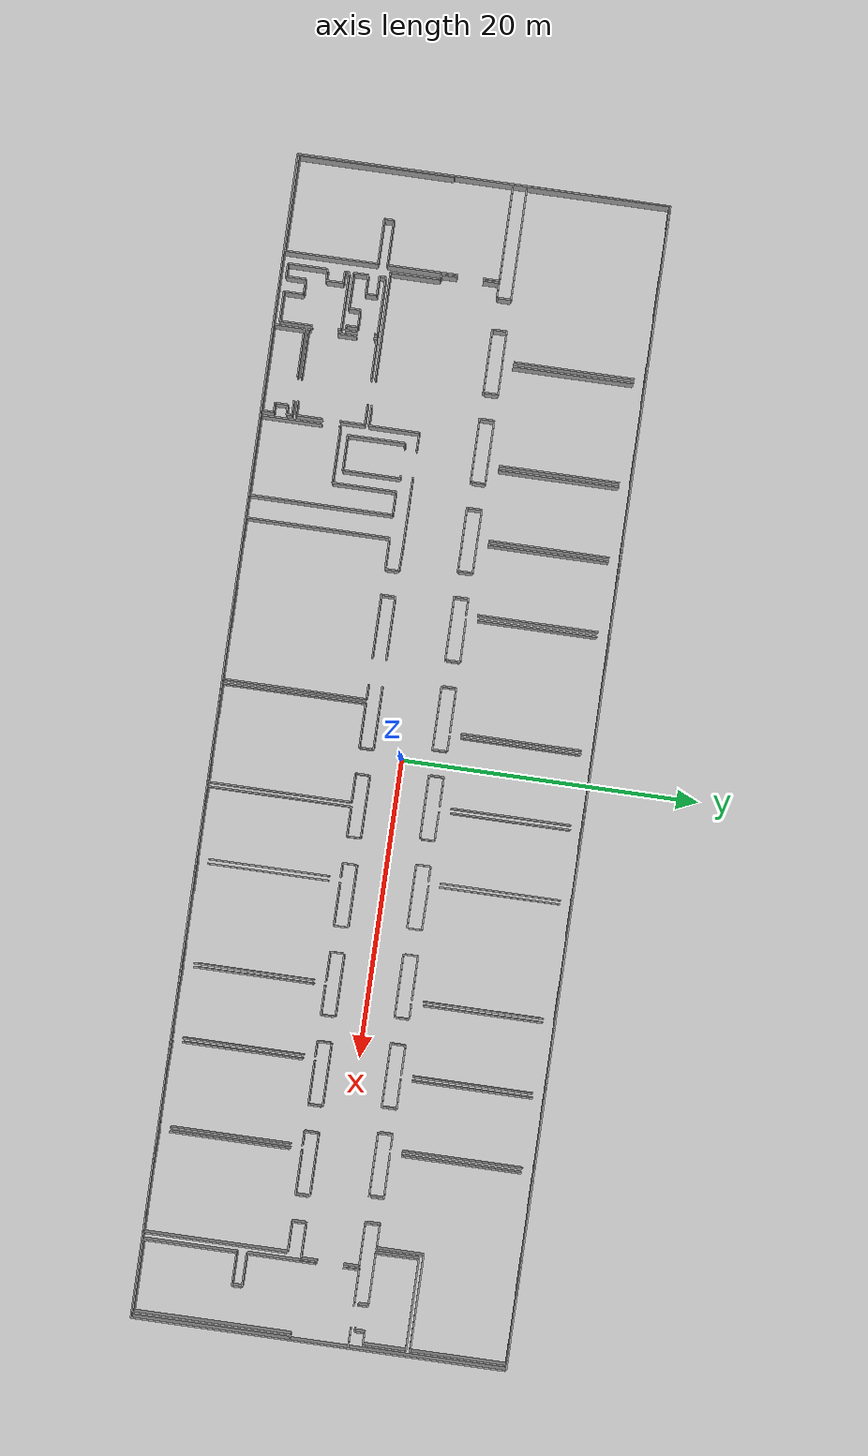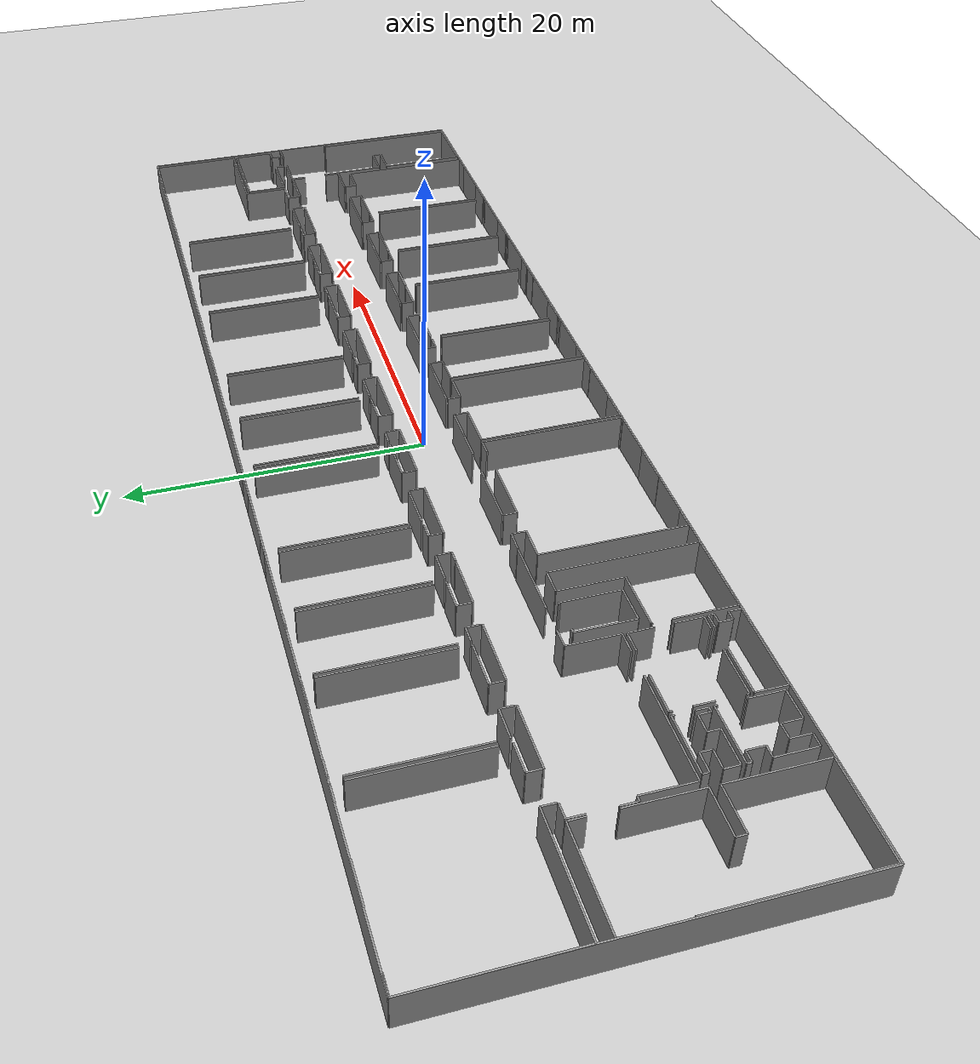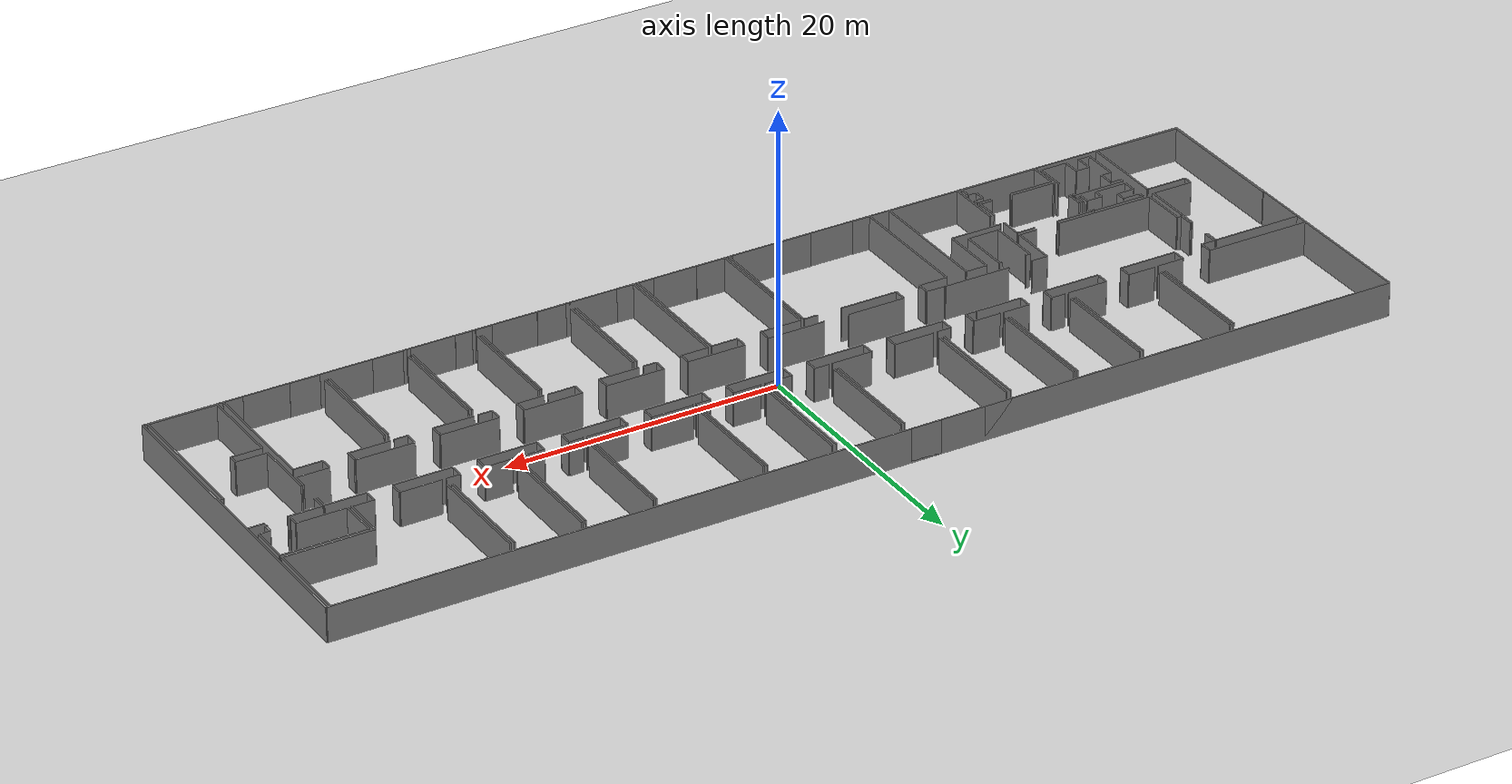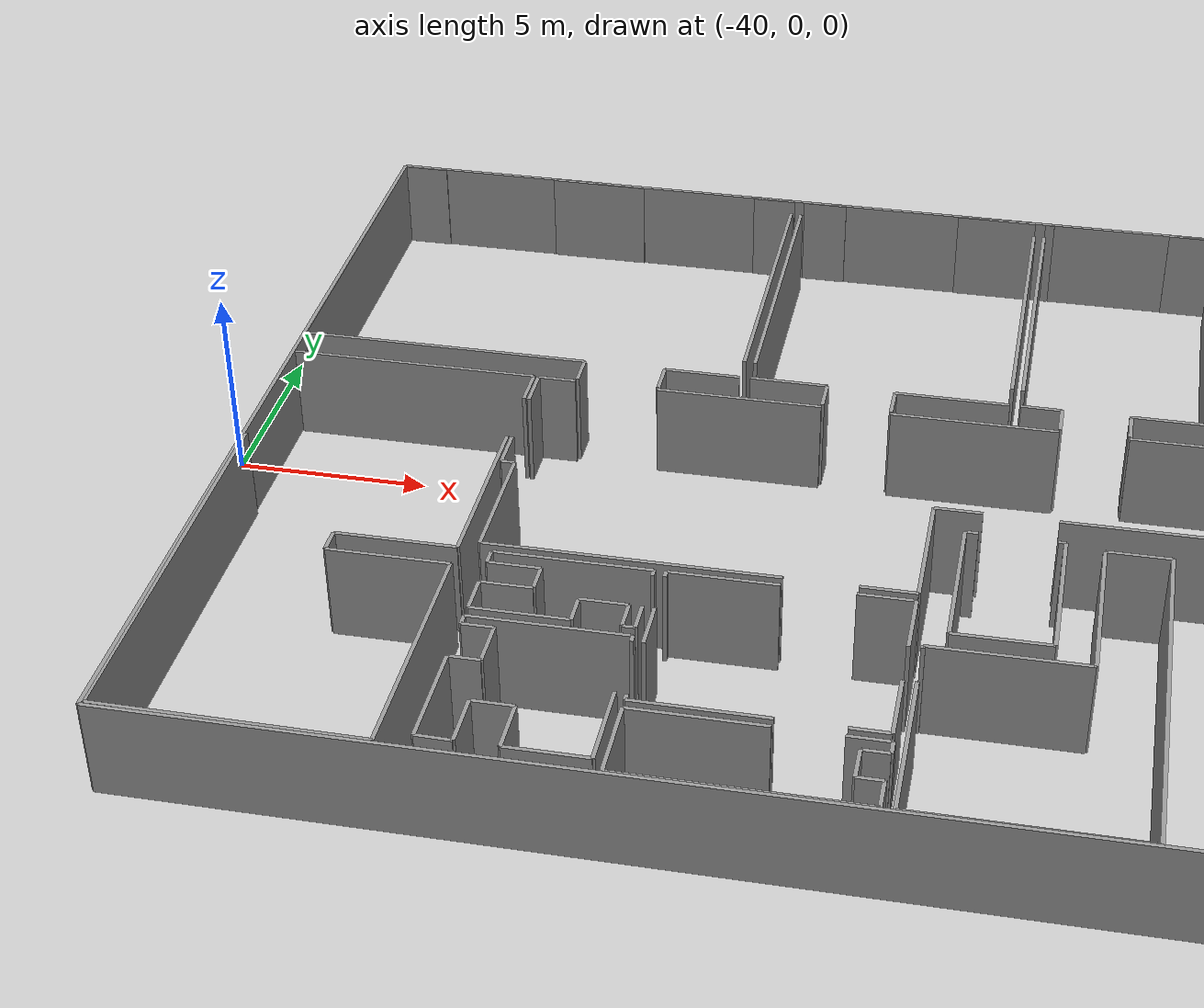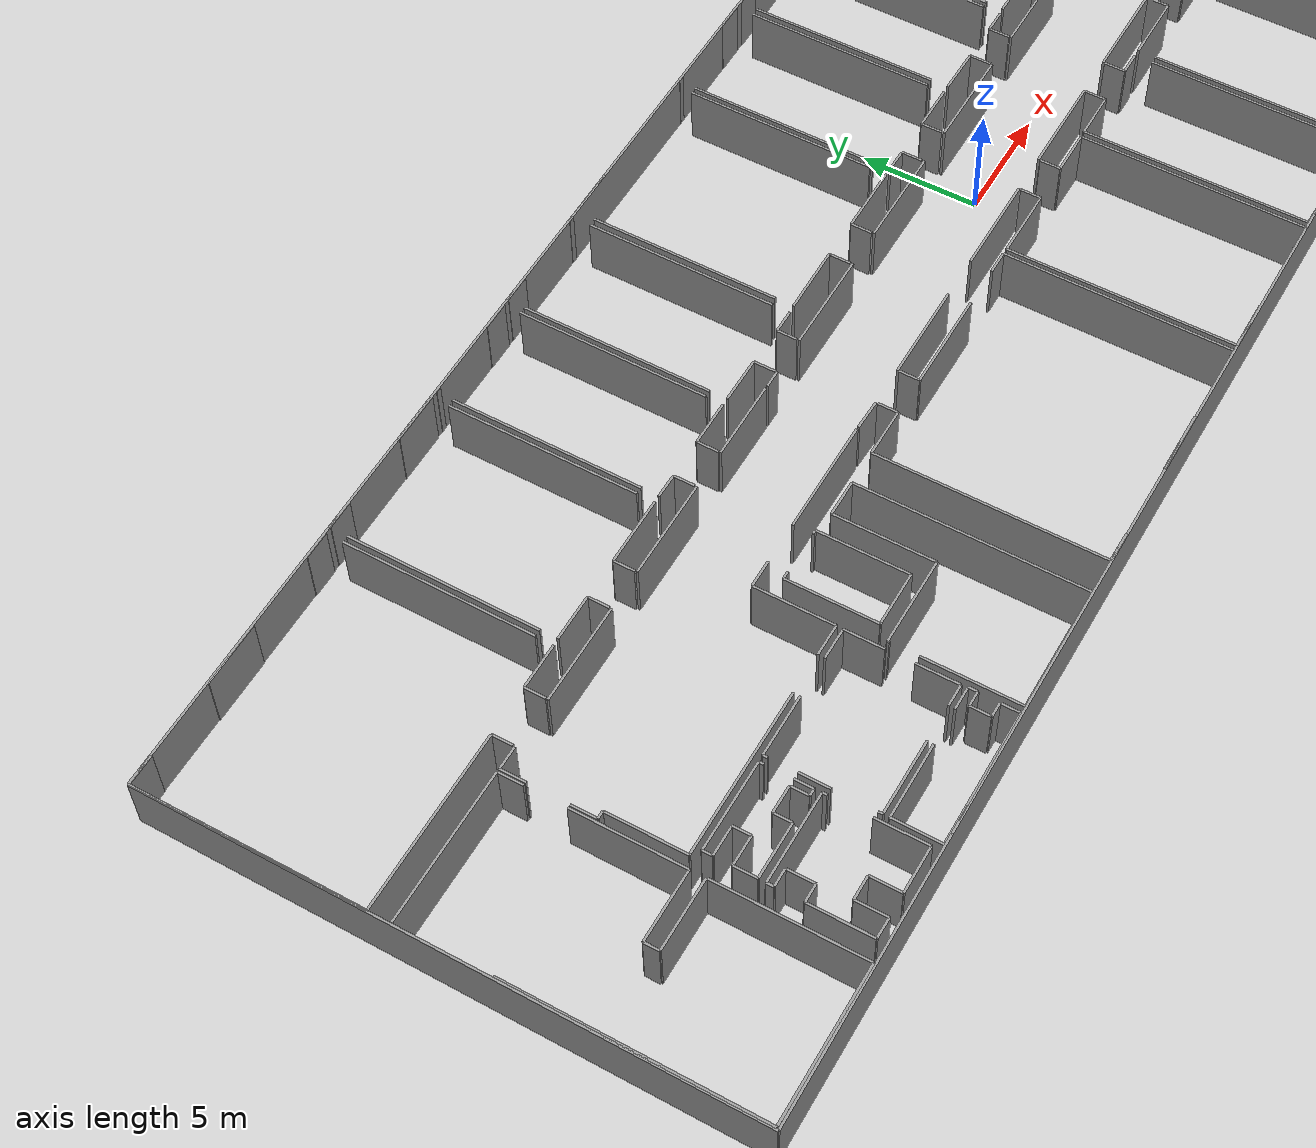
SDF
<sdf version="1.6">
  <world name="default">
    <light name="sun" type="directional">
      <cast_shadows>1</cast_shadows>
      <pose frame="">0 0 10 0 -0 0</pose>
      <diffuse>0.8 0.8 0.8 1</diffuse>
      <specular>0.1 0.1 0.1 1</specular>
      <attenuation>
        <range>1000</range>
        <constant>0.9</constant>
        <linear>0.01</linear>
        <quadratic>0.001</quadratic>
      </attenuation>
      <direction>-0.5 0.5 -1</direction>
    </light>
    <model name="ground_plane">
      <static>1</static>
      <link name="link">
        <collision name="collision">
          <geometry>
            <plane>
              <normal>0 0 1</normal>
              <size>100 100</size>
            </plane>
          </geometry>
          <surface>
            <friction>
              <ode>
                <mu>100</mu>
                <mu2>50</mu2>
              </ode>
              <torsional>
                <ode />
              </torsional>
            </friction>
            <contact>
              <ode />
            </contact>
            <bounce />
          </surface>
          <max_contacts>10</max_contacts>
        </collision>
        <visual name="visual">
          <cast_shadows>0</cast_shadows>
          <geometry>
            <plane>
              <normal>0 0 1</normal>
              <size>100 100</size>
            </plane>
          </geometry>
          <material>
            <script>
              <uri>file://media/materials/scripts/gazebo.material</uri>
              <name>Gazebo/Grey</name>
            </script>
          </material>
        </visual>
        <self_collide>0</self_collide>
        <kinematic>0</kinematic>
        <gravity>1</gravity>
      </link>
    </model>
    <gravity>0 0 -9.8</gravity>
    <magnetic_field>6e-06 2.3e-05 -4.2e-05</magnetic_field>
    <atmosphere type="adiabatic" />
    <physics default="0" name="default_physics" type="ode">
      <max_step_size>0.001</max_step_size>
      <real_time_factor>1</real_time_factor>
      <real_time_update_rate>1000</real_time_update_rate>
    </physics>
    <scene>
      <ambient>0.4 0.4 0.4 1</ambient>
      <background>0.7 0.7 0.7 1</background>
      <shadows>1</shadows>
    </scene>
    <spherical_coordinates>
      <surface_model>EARTH_WGS84</surface_model>
      <latitude_deg>0</latitude_deg>
      <longitude_deg>0</longitude_deg>
      <elevation>0</elevation>
      <heading_deg>0</heading_deg>
    </spherical_coordinates>
  <model name="50052753">
		<static>1</static>
		<link name="Wall_0">
			<collision name="Wall_0_Collision">
				<geometry>
					<box>
						<size>7.63324305639 0.1 2.5</size>
					</box>
				</geometry>
				<pose frame="">3.8166215282 0 1.25 0 0 0</pose>
			</collision>
			<visual name="Wall_0_Visual">
				<pose frame="">3.8166215282 0 1.25 0 0 0</pose>
				<geometry>
					<box>
						<size>7.63324305639 0.1 2.5</size>
					</box>
				</geometry>
				<material>
					<script>
						<uri>file://media/materials/scripts/gazebo.material</uri>
						<name>Gazebo/Grey</name>
					</script>
					<ambient>1 1 1 1</ambient>
				</material>
			</visual>
			<pose frame="">0.0230872176731 -9.6408161712 0 0 0 0.0</pose>
		</link>
		<link name="Wall_1">
			<collision name="Wall_1_Collision">
				<geometry>
					<box>
						<size>0.879851328466 0.1 2.5</size>
					</box>
				</geometry>
				<pose frame="">0.439925664233 0 1.25 0 0 0</pose>
			</collision>
			<visual name="Wall_1_Visual">
				<pose frame="">0.439925664233 0 1.25 0 0 0</pose>
				<geometry>
					<box>
						<size>0.879851328466 0.1 2.5</size>
					</box>
				</geometry>
				<material>
					<script>
						<uri>file://media/materials/scripts/gazebo.material</uri>
						<name>Gazebo/Grey</name>
					</script>
					<ambient>1 1 1 1</ambient>
				</material>
			</visual>
			<pose frame="">7.65633027407 -9.6408161712 0 0 0 -1.57079632679</pose>
		</link>
		<link name="Wall_2">
			<collision name="Wall_2_Collision">
				<geometry>
					<box>
						<size>0.892536612902 0.1 2.5</size>
					</box>
				</geometry>
				<pose frame="">0.446268306451 0 1.25 0 0 0</pose>
			</collision>
			<visual name="Wall_2_Visual">
				<pose frame="">0.446268306451 0 1.25 0 0 0</pose>
				<geometry>
					<box>
						<size>0.892536612902 0.1 2.5</size>
					</box>
				</geometry>
				<material>
					<script>
						<uri>file://media/materials/scripts/gazebo.material</uri>
						<name>Gazebo/Grey</name>
					</script>
					<ambient>1 1 1 1</ambient>
				</material>
			</visual>
			<pose frame="">9.79075623323 -10.5206674997 0 0 0 1.57079632679</pose>
		</link>
		<link name="Wall_3">
			<collision name="Wall_3_Collision">
				<geometry>
					<box>
						<size>1.97040523141 0.1 2.5</size>
					</box>
				</geometry>
				<pose frame="">0.985202615706 0 1.25 0 0 0</pose>
			</collision>
			<visual name="Wall_3_Visual">
				<pose frame="">0.985202615706 0 1.25 0 0 0</pose>
				<geometry>
					<box>
						<size>1.97040523141 0.1 2.5</size>
					</box>
				</geometry>
				<material>
					<script>
						<uri>file://media/materials/scripts/gazebo.material</uri>
						<name>Gazebo/Grey</name>
					</script>
					<ambient>1 1 1 1</ambient>
				</material>
			</visual>
			<pose frame="">9.79075623323 -9.62813088676 0 0 0 0.0</pose>
		</link>
		<link name="Wall_4">
			<collision name="Wall_4_Collision">
				<geometry>
					<box>
						<size>8.11249310238 0.1 2.5</size>
					</box>
				</geometry>
				<pose frame="">4.05624655119 0 1.25 0 0 0</pose>
			</collision>
			<visual name="Wall_4_Visual">
				<pose frame="">4.05624655119 0 1.25 0 0 0</pose>
				<geometry>
					<box>
						<size>8.11249310238 0.1 2.5</size>
					</box>
				</geometry>
				<material>
					<script>
						<uri>file://media/materials/scripts/gazebo.material</uri>
						<name>Gazebo/Grey</name>
					</script>
					<ambient>1 1 1 1</ambient>
				</material>
			</visual>
			<pose frame="">11.7611614646 -8.87576666688 0 0 0 1.57079632679</pose>
		</link>
		<link name="Wall_5">
			<collision name="Wall_5_Collision">
				<geometry>
					<box>
						<size>1.19863252634 0.1 2.5</size>
					</box>
				</geometry>
				<pose frame="">0.599316263169 0 1.25 0 0 0</pose>
			</collision>
			<visual name="Wall_5_Visual">
				<pose frame="">0.599316263169 0 1.25 0 0 0</pose>
				<geometry>
					<box>
						<size>1.19863252634 0.1 2.5</size>
					</box>
				</geometry>
				<material>
					<script>
						<uri>file://media/materials/scripts/gazebo.material</uri>
						<name>Gazebo/Grey</name>
					</script>
					<ambient>1 1 1 1</ambient>
				</material>
			</visual>
			<pose frame="">11.7611614646 -0.0282881842918 0 0 0 3.14159265359</pose>
		</link>
		<link name="Wall_6">
			<collision name="Wall_6_Collision">
				<geometry>
					<box>
						<size>2.71465086926 0.1 2.5</size>
					</box>
				</geometry>
				<pose frame="">1.35732543463 0 1.25 0 0 0</pose>
			</collision>
			<visual name="Wall_6_Visual">
				<pose frame="">1.35732543463 0 1.25 0 0 0</pose>
				<geometry>
					<box>
						<size>2.71465086926 0.1 2.5</size>
					</box>
				</geometry>
				<material>
					<script>
						<uri>file://media/materials/scripts/gazebo.material</uri>
						<name>Gazebo/Grey</name>
					</script>
					<ambient>1 1 1 1</ambient>
				</material>
			</visual>
			<pose frame="">7.27742082797 -0.0282881842918 0 0 0 3.14159265359</pose>
		</link>
		<link name="Wall_7">
			<collision name="Wall_7_Collision">
				<geometry>
					<box>
						<size>1.27778870122 0.1 2.5</size>
					</box>
				</geometry>
				<pose frame="">0.638894350609 0 1.25 0 0 0</pose>
			</collision>
			<visual name="Wall_7_Visual">
				<pose frame="">0.638894350609 0 1.25 0 0 0</pose>
				<geometry>
					<box>
						<size>1.27778870122 0.1 2.5</size>
					</box>
				</geometry>
				<material>
					<script>
						<uri>file://media/materials/scripts/gazebo.material</uri>
						<name>Gazebo/Grey</name>
					</script>
					<ambient>1 1 1 1</ambient>
				</material>
			</visual>
			<pose frame="">1.27778870122 -0.0282881842918 0 0 0 3.14159265359</pose>
		</link>
		<link name="Wall_8">
			<collision name="Wall_8_Collision">
				<geometry>
					<box>
						<size>9.61255571213 0.1 2.5</size>
					</box>
				</geometry>
				<pose frame="">4.80627785606 0 1.25 0 0 0</pose>
			</collision>
			<visual name="Wall_8_Visual">
				<pose frame="">4.80627785606 0 1.25 0 0 0</pose>
				<geometry>
					<box>
						<size>9.61255571213 0.1 2.5</size>
					</box>
				</geometry>
				<material>
					<script>
						<uri>file://media/materials/scripts/gazebo.material</uri>
						<name>Gazebo/Grey</name>
					</script>
					<ambient>1 1 1 1</ambient>
				</material>
			</visual>
			<pose frame="">0.0 -0.0282881842918 0 0 0 -1.56839454723</pose>
		</link>
		<link name="Wall_9">
			<collision name="Wall_9_Collision">
				<geometry>
					<box>
						<size>10.4648522481 0.1 2.5</size>
					</box>
				</geometry>
				<pose frame="">5.23242612407 0 1.25 0 0 0</pose>
			</collision>
			<visual name="Wall_9_Visual">
				<pose frame="">5.23242612407 0 1.25 0 0 0</pose>
				<geometry>
					<box>
						<size>10.4648522481 0.1 2.5</size>
					</box>
				</geometry>
				<material>
					<script>
						<uri>file://media/materials/scripts/gazebo.material</uri>
						<name>Gazebo/Grey</name>
					</script>
					<ambient>1 1 1 1</ambient>
				</material>
			</visual>
			<pose frame="">0.0715450042179 -24.9756759671 0 0 0 1.57079632679</pose>
		</link>
		<link name="Wall_10">
			<collision name="Wall_10_Collision">
				<geometry>
					<box>
						<size>6.44716896165 0.1 2.5</size>
					</box>
				</geometry>
				<pose frame="">3.22358448082 0 1.25 0 0 0</pose>
			</collision>
			<visual name="Wall_10_Visual">
				<pose frame="">3.22358448082 0 1.25 0 0 0</pose>
				<geometry>
					<box>
						<size>6.44716896165 0.1 2.5</size>
					</box>
				</geometry>
				<material>
					<script>
						<uri>file://media/materials/scripts/gazebo.material</uri>
						<name>Gazebo/Grey</name>
					</script>
					<ambient>1 1 1 1</ambient>
				</material>
			</visual>
			<pose frame="">0.0715450042179 -10.5854893031 0 0 0 0.0</pose>
		</link>
		<link name="Wall_11">
			<collision name="Wall_11_Collision">
				<geometry>
					<box>
						<size>1.07342876896 0.1 2.5</size>
					</box>
				</geometry>
				<pose frame="">0.536714384478 0 1.25 0 0 0</pose>
			</collision>
			<visual name="Wall_11_Visual">
				<pose frame="">0.536714384478 0 1.25 0 0 0</pose>
				<geometry>
					<box>
						<size>1.07342876896 0.1 2.5</size>
					</box>
				</geometry>
				<material>
					<script>
						<uri>file://media/materials/scripts/gazebo.material</uri>
						<name>Gazebo/Grey</name>
					</script>
					<ambient>1 1 1 1</ambient>
				</material>
			</visual>
			<pose frame="">6.51871396586 -10.5854893031 0 0 0 -1.57079632679</pose>
		</link>
		<link name="Wall_12">
			<collision name="Wall_12_Collision">
				<geometry>
					<box>
						<size>4.72006748571 0.1 2.5</size>
					</box>
				</geometry>
				<pose frame="">2.36003374286 0 1.25 0 0 0</pose>
			</collision>
			<visual name="Wall_12_Visual">
				<pose frame="">2.36003374286 0 1.25 0 0 0</pose>
				<geometry>
					<box>
						<size>4.72006748571 0.1 2.5</size>
					</box>
				</geometry>
				<material>
					<script>
						<uri>file://media/materials/scripts/gazebo.material</uri>
						<name>Gazebo/Grey</name>
					</script>
					<ambient>1 1 1 1</ambient>
				</material>
			</visual>
			<pose frame="">6.51871396586 -13.3877954878 0 0 0 -1.57079632679</pose>
		</link>
		<link name="Wall_13">
			<collision name="Wall_13_Collision">
				<geometry>
					<box>
						<size>3.02290328105 0.1 2.5</size>
					</box>
				</geometry>
				<pose frame="">1.51145164052 0 1.25 0 0 0</pose>
			</collision>
			<visual name="Wall_13_Visual">
				<pose frame="">1.51145164052 0 1.25 0 0 0</pose>
				<geometry>
					<box>
						<size>3.02290328105 0.1 2.5</size>
					</box>
				</geometry>
				<material>
					<script>
						<uri>file://media/materials/scripts/gazebo.material</uri>
						<name>Gazebo/Grey</name>
					</script>
					<ambient>1 1 1 1</ambient>
				</material>
			</visual>
			<pose frame="">6.51871396586 -18.1078629736 0 0 0 3.14159265359</pose>
		</link>
		<link name="Wall_14">
			<collision name="Wall_14_Collision">
				<geometry>
					<box>
						<size>0.642636509517 0.1 2.5</size>
					</box>
				</geometry>
				<pose frame="">0.321318254759 0 1.25 0 0 0</pose>
			</collision>
			<visual name="Wall_14_Visual">
				<pose frame="">0.321318254759 0 1.25 0 0 0</pose>
				<geometry>
					<box>
						<size>0.642636509517 0.1 2.5</size>
					</box>
				</geometry>
				<material>
					<script>
						<uri>file://media/materials/scripts/gazebo.material</uri>
						<name>Gazebo/Grey</name>
					</script>
					<ambient>1 1 1 1</ambient>
				</material>
			</visual>
			<pose frame="">3.49581068482 -18.1078629736 0 0 0 -1.57079632679</pose>
		</link>
		<link name="Wall_15">
			<collision name="Wall_15_Collision">
				<geometry>
					<box>
						<size>3.03102186309 0.1 2.5</size>
					</box>
				</geometry>
				<pose frame="">1.51551093154 0 1.25 0 0 0</pose>
			</collision>
			<visual name="Wall_15_Visual">
				<pose frame="">1.51551093154 0 1.25 0 0 0</pose>
				<geometry>
					<box>
						<size>3.03102186309 0.1 2.5</size>
					</box>
				</geometry>
				<material>
					<script>
						<uri>file://media/materials/scripts/gazebo.material</uri>
						<name>Gazebo/Grey</name>
					</script>
					<ambient>1 1 1 1</ambient>
				</material>
			</visual>
			<pose frame="">3.49581068482 -18.7504994831 0 0 0 0.0</pose>
		</link>
		<link name="Wall_16">
			<collision name="Wall_16_Collision">
				<geometry>
					<box>
						<size>6.25435263822 0.1 2.5</size>
					</box>
				</geometry>
				<pose frame="">3.12717631911 0 1.25 0 0 0</pose>
			</collision>
			<visual name="Wall_16_Visual">
				<pose frame="">3.12717631911 0 1.25 0 0 0</pose>
				<geometry>
					<box>
						<size>6.25435263822 0.1 2.5</size>
					</box>
				</geometry>
				<material>
					<script>
						<uri>file://media/materials/scripts/gazebo.material</uri>
						<name>Gazebo/Grey</name>
					</script>
					<ambient>1 1 1 1</ambient>
				</material>
			</visual>
			<pose frame="">6.5268325479 -18.7504994831 0 0 0 -1.57079632679</pose>
		</link>
		<link name="Wall_17">
			<collision name="Wall_17_Collision">
				<geometry>
					<box>
						<size>6.45535347751 0.1 2.5</size>
					</box>
				</geometry>
				<pose frame="">3.22767673876 0 1.25 0 0 0</pose>
			</collision>
			<visual name="Wall_17_Visual">
				<pose frame="">3.22767673876 0 1.25 0 0 0</pose>
				<geometry>
					<box>
						<size>6.45535347751 0.1 2.5</size>
					</box>
				</geometry>
				<material>
					<script>
						<uri>file://media/materials/scripts/gazebo.material</uri>
						<name>Gazebo/Grey</name>
					</script>
					<ambient>1 1 1 1</ambient>
				</material>
			</visual>
			<pose frame="">6.5268325479 -25.0048521213 0 0 0 3.13707295476</pose>
		</link>
		<link name="Wall_18">
			<collision name="Wall_18_Collision">
				<geometry>
					<box>
						<size>3.34739285692 0.1 2.5</size>
					</box>
				</geometry>
				<pose frame="">1.67369642846 0 1.25 0 0 0</pose>
			</collision>
			<visual name="Wall_18_Visual">
				<pose frame="">1.67369642846 0 1.25 0 0 0</pose>
				<geometry>
					<box>
						<size>3.34739285692 0.1 2.5</size>
					</box>
				</geometry>
				<material>
					<script>
						<uri>file://media/materials/scripts/gazebo.material</uri>
						<name>Gazebo/Grey</name>
					</script>
					<ambient>1 1 1 1</ambient>
				</material>
			</visual>
			<pose frame="">6.98350278759 -17.8350025053 0 0 0 1.57079632679</pose>
		</link>
		<link name="Wall_19">
			<collision name="Wall_19_Collision">
				<geometry>
					<box>
						<size>0.334130392039 0.1 2.5</size>
					</box>
				</geometry>
				<pose frame="">0.167065196019 0 1.25 0 0 0</pose>
			</collision>
			<visual name="Wall_19_Visual">
				<pose frame="">0.167065196019 0 1.25 0 0 0</pose>
				<geometry>
					<box>
						<size>0.334130392039 0.1 2.5</size>
					</box>
				</geometry>
				<material>
					<script>
						<uri>file://media/materials/scripts/gazebo.material</uri>
						<name>Gazebo/Grey</name>
					</script>
					<ambient>1 1 1 1</ambient>
				</material>
			</visual>
			<pose frame="">6.98350278759 -14.4876096484 0 0 0 3.14159265359</pose>
		</link>
		<link name="Wall_20">
			<collision name="Wall_20_Collision">
				<geometry>
					<box>
						<size>1.08078623393 0.1 2.5</size>
					</box>
				</geometry>
				<pose frame="">0.540393116965 0 1.25 0 0 0</pose>
			</collision>
			<visual name="Wall_20_Visual">
				<pose frame="">0.540393116965 0 1.25 0 0 0</pose>
				<geometry>
					<box>
						<size>1.08078623393 0.1 2.5</size>
					</box>
				</geometry>
				<material>
					<script>
						<uri>file://media/materials/scripts/gazebo.material</uri>
						<name>Gazebo/Grey</name>
					</script>
					<ambient>1 1 1 1</ambient>
				</material>
			</visual>
			<pose frame="">6.64937239555 -14.4876096484 0 0 0 1.57079632679</pose>
		</link>
		<link name="Wall_21">
			<collision name="Wall_21_Collision">
				<geometry>
					<box>
						<size>1.06987688931 0.1 2.5</size>
					</box>
				</geometry>
				<pose frame="">0.534938444657 0 1.25 0 0 0</pose>
			</collision>
			<visual name="Wall_21_Visual">
				<pose frame="">0.534938444657 0 1.25 0 0 0</pose>
				<geometry>
					<box>
						<size>1.06987688931 0.1 2.5</size>
					</box>
				</geometry>
				<material>
					<script>
						<uri>file://media/materials/scripts/gazebo.material</uri>
						<name>Gazebo/Grey</name>
					</script>
					<ambient>1 1 1 1</ambient>
				</material>
			</visual>
			<pose frame="">6.64937239555 -11.6717302094 0 0 0 1.57079632679</pose>
		</link>
		<link name="Wall_22">
			<collision name="Wall_22_Collision">
				<geometry>
					<box>
						<size>0.979050252754 0.1 2.5</size>
					</box>
				</geometry>
				<pose frame="">0.489525126377 0 1.25 0 0 0</pose>
			</collision>
			<visual name="Wall_22_Visual">
				<pose frame="">0.489525126377 0 1.25 0 0 0</pose>
				<geometry>
					<box>
						<size>0.979050252754 0.1 2.5</size>
					</box>
				</geometry>
				<material>
					<script>
						<uri>file://media/materials/scripts/gazebo.material</uri>
						<name>Gazebo/Grey</name>
					</script>
					<ambient>1 1 1 1</ambient>
				</material>
			</visual>
			<pose frame="">6.64937239555 -10.6018533201 0 0 0 0.0</pose>
		</link>
		<link name="Wall_23">
			<collision name="Wall_23_Collision">
				<geometry>
					<box>
						<size>4.25794257372 0.1 2.5</size>
					</box>
				</geometry>
				<pose frame="">2.12897128686 0 1.25 0 0 0</pose>
			</collision>
			<visual name="Wall_23_Visual">
				<pose frame="">2.12897128686 0 1.25 0 0 0</pose>
				<geometry>
					<box>
						<size>4.25794257372 0.1 2.5</size>
					</box>
				</geometry>
				<material>
					<script>
						<uri>file://media/materials/scripts/gazebo.material</uri>
						<name>Gazebo/Grey</name>
					</script>
					<ambient>1 1 1 1</ambient>
				</material>
			</visual>
			<pose frame="">9.77604130329 -10.6018533201 0 0 0 0.0</pose>
		</link>
		<link name="Wall_24">
			<collision name="Wall_24_Collision">
				<geometry>
					<box>
						<size>4.2458915535 0.1 2.5</size>
					</box>
				</geometry>
				<pose frame="">2.12294577675 0 1.25 0 0 0</pose>
			</collision>
			<visual name="Wall_24_Visual">
				<pose frame="">2.12294577675 0 1.25 0 0 0</pose>
				<geometry>
					<box>
						<size>4.2458915535 0.1 2.5</size>
					</box>
				</geometry>
				<material>
					<script>
						<uri>file://media/materials/scripts/gazebo.material</uri>
						<name>Gazebo/Grey</name>
					</script>
					<ambient>1 1 1 1</ambient>
				</material>
			</visual>
			<pose frame="">15.8043421729 -10.6018533201 0 0 0 0.0</pose>
		</link>
		<link name="Wall_25">
			<collision name="Wall_25_Collision">
				<geometry>
					<box>
						<size>3.38468759316 0.1 2.5</size>
					</box>
				</geometry>
				<pose frame="">1.69234379658 0 1.25 0 0 0</pose>
			</collision>
			<visual name="Wall_25_Visual">
				<pose frame="">1.69234379658 0 1.25 0 0 0</pose>
				<geometry>
					<box>
						<size>3.38468759316 0.1 2.5</size>
					</box>
				</geometry>
				<material>
					<script>
						<uri>file://media/materials/scripts/gazebo.material</uri>
						<name>Gazebo/Grey</name>
					</script>
					<ambient>1 1 1 1</ambient>
				</material>
			</visual>
			<pose frame="">21.7933186607 -10.6018533201 0 0 0 0.0</pose>
		</link>
		<link name="Wall_26">
			<collision name="Wall_26_Collision">
				<geometry>
					<box>
						<size>4.89334847111 0.1 2.5</size>
					</box>
				</geometry>
				<pose frame="">2.44667423555 0 1.25 0 0 0</pose>
			</collision>
			<visual name="Wall_26_Visual">
				<pose frame="">2.44667423555 0 1.25 0 0 0</pose>
				<geometry>
					<box>
						<size>4.89334847111 0.1 2.5</size>
					</box>
				</geometry>
				<material>
					<script>
						<uri>file://media/materials/scripts/gazebo.material</uri>
						<name>Gazebo/Grey</name>
					</script>
					<ambient>1 1 1 1</ambient>
				</material>
			</visual>
			<pose frame="">25.1780062538 -14.44397227 0 0 0 3.14159265359</pose>
		</link>
		<link name="Wall_27">
			<collision name="Wall_27_Collision">
				<geometry>
					<box>
						<size>1.17909718831 0.1 2.5</size>
					</box>
				</geometry>
				<pose frame="">0.589548594153 0 1.25 0 0 0</pose>
			</collision>
			<visual name="Wall_27_Visual">
				<pose frame="">0.589548594153 0 1.25 0 0 0</pose>
				<geometry>
					<box>
						<size>1.17909718831 0.1 2.5</size>
					</box>
				</geometry>
				<material>
					<script>
						<uri>file://media/materials/scripts/gazebo.material</uri>
						<name>Gazebo/Grey</name>
					</script>
					<ambient>1 1 1 1</ambient>
				</material>
			</visual>
			<pose frame="">18.4762436336 -14.44397227 0 0 0 3.14159265359</pose>
		</link>
		<link name="Wall_28">
			<collision name="Wall_28_Collision">
				<geometry>
					<box>
						<size>3.38570241591 0.1 2.5</size>
					</box>
				</geometry>
				<pose frame="">1.69285120796 0 1.25 0 0 0</pose>
			</collision>
			<visual name="Wall_28_Visual">
				<pose frame="">1.69285120796 0 1.25 0 0 0</pose>
				<geometry>
					<box>
						<size>3.38570241591 0.1 2.5</size>
					</box>
				</geometry>
				<material>
					<script>
						<uri>file://media/materials/scripts/gazebo.material</uri>
						<name>Gazebo/Grey</name>
					</script>
					<ambient>1 1 1 1</ambient>
				</material>
			</visual>
			<pose frame="">17.2971464453 -14.44397227 0 0 0 -1.57079632679</pose>
		</link>
		<link name="Wall_29">
			<collision name="Wall_29_Collision">
				<geometry>
					<box>
						<size>1.36151157849 0.1 2.5</size>
					</box>
				</geometry>
				<pose frame="">0.680755789247 0 1.25 0 0 0</pose>
			</collision>
			<visual name="Wall_29_Visual">
				<pose frame="">0.680755789247 0 1.25 0 0 0</pose>
				<geometry>
					<box>
						<size>1.36151157849 0.1 2.5</size>
					</box>
				</geometry>
				<material>
					<script>
						<uri>file://media/materials/scripts/gazebo.material</uri>
						<name>Gazebo/Grey</name>
					</script>
					<ambient>1 1 1 1</ambient>
				</material>
			</visual>
			<pose frame="">17.2971464453 -17.8296746859 0 0 0 3.14159265359</pose>
		</link>
		<link name="Wall_30">
			<collision name="Wall_30_Collision">
				<geometry>
					<box>
						<size>7.18811840003 0.1 2.5</size>
					</box>
				</geometry>
				<pose frame="">3.59405920001 0 1.25 0 0 0</pose>
			</collision>
			<visual name="Wall_30_Visual">
				<pose frame="">3.59405920001 0 1.25 0 0 0</pose>
				<geometry>
					<box>
						<size>7.18811840003 0.1 2.5</size>
					</box>
				</geometry>
				<material>
					<script>
						<uri>file://media/materials/scripts/gazebo.material</uri>
						<name>Gazebo/Grey</name>
					</script>
					<ambient>1 1 1 1</ambient>
				</material>
			</visual>
			<pose frame="">14.1716192131 -17.8296746859 0 0 0 -3.14085145545</pose>
		</link>
		<link name="Wall_31">
			<collision name="Wall_31_Collision">
				<geometry>
					<box>
						<size>8.12213391855 0.1 2.5</size>
					</box>
				</geometry>
				<pose frame="">4.06106695927 0 1.25 0 0 0</pose>
			</collision>
			<visual name="Wall_31_Visual">
				<pose frame="">4.06106695927 0 1.25 0 0 0</pose>
				<geometry>
					<box>
						<size>8.12213391855 0.1 2.5</size>
					</box>
				</geometry>
				<material>
					<script>
						<uri>file://media/materials/scripts/gazebo.material</uri>
						<name>Gazebo/Grey</name>
					</script>
					<ambient>1 1 1 1</ambient>
				</material>
			</visual>
			<pose frame="">12.0432821905 -8.89086215536 0 0 0 1.57079632679</pose>
		</link>
		<link name="Wall_32">
			<collision name="Wall_32_Collision">
				<geometry>
					<box>
						<size>1.22844294476 0.1 2.5</size>
					</box>
				</geometry>
				<pose frame="">0.614221472381 0 1.25 0 0 0</pose>
			</collision>
			<visual name="Wall_32_Visual">
				<pose frame="">0.614221472381 0 1.25 0 0 0</pose>
				<geometry>
					<box>
						<size>1.22844294476 0.1 2.5</size>
					</box>
				</geometry>
				<material>
					<script>
						<uri>file://media/materials/scripts/gazebo.material</uri>
						<name>Gazebo/Grey</name>
					</script>
					<ambient>1 1 1 1</ambient>
				</material>
			</visual>
			<pose frame="">12.0432821905 -0.0228335119844 0 0 0 0.0</pose>
		</link>
		<link name="Wall_33">
			<collision name="Wall_33_Collision">
				<geometry>
					<box>
						<size>2.20825431458 0.1 2.5</size>
					</box>
				</geometry>
				<pose frame="">1.10412715729 0 1.25 0 0 0</pose>
			</collision>
			<visual name="Wall_33_Visual">
				<pose frame="">1.10412715729 0 1.25 0 0 0</pose>
				<geometry>
					<box>
						<size>2.20825431458 0.1 2.5</size>
					</box>
				</geometry>
				<material>
					<script>
						<uri>file://media/materials/scripts/gazebo.material</uri>
						<name>Gazebo/Grey</name>
					</script>
					<ambient>1 1 1 1</ambient>
				</material>
			</visual>
			<pose frame="">16.5268959743 -0.0228335119844 0 0 0 0.0</pose>
		</link>
		<link name="Wall_34">
			<collision name="Wall_34_Collision">
				<geometry>
					<box>
						<size>8.09524111554 0.1 2.5</size>
					</box>
				</geometry>
				<pose frame="">4.04762055777 0 1.25 0 0 0</pose>
			</collision>
			<visual name="Wall_34_Visual">
				<pose frame="">4.04762055777 0 1.25 0 0 0</pose>
				<geometry>
					<box>
						<size>8.09524111554 0.1 2.5</size>
					</box>
				</geometry>
				<material>
					<script>
						<uri>file://media/materials/scripts/gazebo.material</uri>
						<name>Gazebo/Grey</name>
					</script>
					<ambient>1 1 1 1</ambient>
				</material>
			</visual>
			<pose frame="">18.7351502889 -0.773548644894 0 0 0 -1.57079632679</pose>
		</link>
		<link name="Wall_35">
			<collision name="Wall_35_Collision">
				<geometry>
					<box>
						<size>2.93080811604 0.1 2.5</size>
					</box>
				</geometry>
				<pose frame="">1.46540405802 0 1.25 0 0 0</pose>
			</collision>
			<visual name="Wall_35_Visual">
				<pose frame="">1.46540405802 0 1.25 0 0 0</pose>
				<geometry>
					<box>
						<size>2.93080811604 0.1 2.5</size>
					</box>
				</geometry>
				<material>
					<script>
						<uri>file://media/materials/scripts/gazebo.material</uri>
						<name>Gazebo/Grey</name>
					</script>
					<ambient>1 1 1 1</ambient>
				</material>
			</visual>
			<pose frame="">18.7351502889 -9.61988545188 0 0 0 3.14159265359</pose>
		</link>
		<link name="Wall_36">
			<collision name="Wall_36_Collision">
				<geometry>
					<box>
						<size>0.894058847035 0.1 2.5</size>
					</box>
				</geometry>
				<pose frame="">0.447029423517 0 1.25 0 0 0</pose>
			</collision>
			<visual name="Wall_36_Visual">
				<pose frame="">0.447029423517 0 1.25 0 0 0</pose>
				<geometry>
					<box>
						<size>0.894058847035 0.1 2.5</size>
					</box>
				</geometry>
				<material>
					<script>
						<uri>file://media/materials/scripts/gazebo.material</uri>
						<name>Gazebo/Grey</name>
					</script>
					<ambient>1 1 1 1</ambient>
				</material>
			</visual>
			<pose frame="">15.8043421729 -9.61988545188 0 0 0 -1.57079632679</pose>
		</link>
		<link name="Wall_37">
			<collision name="Wall_37_Collision">
				<geometry>
					<box>
						<size>0.900274636408 0.1 2.5</size>
					</box>
				</geometry>
				<pose frame="">0.450137318204 0 1.25 0 0 0</pose>
			</collision>
			<visual name="Wall_37_Visual">
				<pose frame="">0.450137318204 0 1.25 0 0 0</pose>
				<geometry>
					<box>
						<size>0.900274636408 0.1 2.5</size>
					</box>
				</geometry>
				<material>
					<script>
						<uri>file://media/materials/scripts/gazebo.material</uri>
						<name>Gazebo/Grey</name>
					</script>
					<ambient>1 1 1 1</ambient>
				</material>
			</visual>
			<pose frame="">14.0447663688 -10.5139442989 0 0 0 1.57079632679</pose>
		</link>
		<link name="Wall_38">
			<collision name="Wall_38_Collision">
				<geometry>
					<box>
						<size>2.00148910268 0.1 2.5</size>
					</box>
				</geometry>
				<pose frame="">1.00074455134 0 1.25 0 0 0</pose>
			</collision>
			<visual name="Wall_38_Visual">
				<pose frame="">1.00074455134 0 1.25 0 0 0</pose>
				<geometry>
					<box>
						<size>2.00148910268 0.1 2.5</size>
					</box>
				</geometry>
				<material>
					<script>
						<uri>file://media/materials/scripts/gazebo.material</uri>
						<name>Gazebo/Grey</name>
					</script>
					<ambient>1 1 1 1</ambient>
				</material>
			</visual>
			<pose frame="">14.0447663688 -9.61366966251 0 0 0 3.13937437861</pose>
		</link>
		<link name="Wall_39">
			<collision name="Wall_39_Collision">
				<geometry>
					<box>
						<size>8.12936453068 0.1 2.5</size>
					</box>
				</geometry>
				<pose frame="">4.06468226534 0 1.25 0 0 0</pose>
			</collision>
			<visual name="Wall_39_Visual">
				<pose frame="">4.06468226534 0 1.25 0 0 0</pose>
				<geometry>
					<box>
						<size>8.12936453068 0.1 2.5</size>
					</box>
				</geometry>
				<material>
					<script>
						<uri>file://media/materials/scripts/gazebo.material</uri>
						<name>Gazebo/Grey</name>
					</script>
					<ambient>1 1 1 1</ambient>
				</material>
			</visual>
			<pose frame="">19.0176515733 -8.88540748305 0 0 0 1.57079632679</pose>
		</link>
		<link name="Wall_40">
			<collision name="Wall_40_Collision">
				<geometry>
					<box>
						<size>0.256115892759 0.1 2.5</size>
					</box>
				</geometry>
				<pose frame="">0.128057946379 0 1.25 0 0 0</pose>
			</collision>
			<visual name="Wall_40_Visual">
				<pose frame="">0.128057946379 0 1.25 0 0 0</pose>
				<geometry>
					<box>
						<size>0.256115892759 0.1 2.5</size>
					</box>
				</geometry>
				<material>
					<script>
						<uri>file://media/materials/scripts/gazebo.material</uri>
						<name>Gazebo/Grey</name>
					</script>
					<ambient>1 1 1 1</ambient>
				</material>
			</visual>
			<pose frame="">19.0176515733 -0.0181399567432 0 0 0 0.0</pose>
		</link>
		<link name="Wall_41">
			<collision name="Wall_41_Collision">
				<geometry>
					<box>
						<size>1.24468010884 0.1 2.5</size>
					</box>
				</geometry>
				<pose frame="">0.62234005442 0 1.25 0 0 0</pose>
			</collision>
			<visual name="Wall_41_Visual">
				<pose frame="">0.62234005442 0 1.25 0 0 0</pose>
				<geometry>
					<box>
						<size>1.24468010884 0.1 2.5</size>
					</box>
				</geometry>
				<material>
					<script>
						<uri>file://media/materials/scripts/gazebo.material</uri>
						<name>Gazebo/Grey</name>
					</script>
					<ambient>1 1 1 1</ambient>
				</material>
			</visual>
			<pose frame="">22.5214539873 -0.0181399567432 0 0 0 0.0</pose>
		</link>
		<link name="Wall_42">
			<collision name="Wall_42_Collision">
				<geometry>
					<box>
						<size>8.11414218935 0.1 2.5</size>
					</box>
				</geometry>
				<pose frame="">4.05707109468 0 1.25 0 0 0</pose>
			</collision>
			<visual name="Wall_42_Visual">
				<pose frame="">4.05707109468 0 1.25 0 0 0</pose>
				<geometry>
					<box>
						<size>8.11414218935 0.1 2.5</size>
					</box>
				</geometry>
				<material>
					<script>
						<uri>file://media/materials/scripts/gazebo.material</uri>
						<name>Gazebo/Grey</name>
					</script>
					<ambient>1 1 1 1</ambient>
				</material>
			</visual>
			<pose frame="">23.7661340961 -0.752491072731 0 0 0 -1.57079632679</pose>
		</link>
		<link name="Wall_43">
			<collision name="Wall_43_Collision">
				<geometry>
					<box>
						<size>1.96647279324 0.1 2.5</size>
					</box>
				</geometry>
				<pose frame="">0.983236396618 0 1.25 0 0 0</pose>
			</collision>
			<visual name="Wall_43_Visual">
				<pose frame="">0.983236396618 0 1.25 0 0 0</pose>
				<geometry>
					<box>
						<size>1.96647279324 0.1 2.5</size>
					</box>
				</geometry>
				<material>
					<script>
						<uri>file://media/materials/scripts/gazebo.material</uri>
						<name>Gazebo/Grey</name>
					</script>
					<ambient>1 1 1 1</ambient>
				</material>
			</visual>
			<pose frame="">23.7661340961 -9.60225290652 0 0 0 3.14159265359</pose>
		</link>
		<link name="Wall_44">
			<collision name="Wall_44_Collision">
				<geometry>
					<box>
						<size>0.916384947641 0.1 2.5</size>
					</box>
				</geometry>
				<pose frame="">0.458192473821 0 1.25 0 0 0</pose>
			</collision>
			<visual name="Wall_44_Visual">
				<pose frame="">0.458192473821 0 1.25 0 0 0</pose>
				<geometry>
					<box>
						<size>0.916384947641 0.1 2.5</size>
					</box>
				</geometry>
				<material>
					<script>
						<uri>file://media/materials/scripts/gazebo.material</uri>
						<name>Gazebo/Grey</name>
					</script>
					<ambient>1 1 1 1</ambient>
				</material>
			</visual>
			<pose frame="">21.7996613029 -9.60225290652 0 0 0 -1.57079632679</pose>
		</link>
		<link name="Wall_45">
			<collision name="Wall_45_Collision">
				<geometry>
					<box>
						<size>0.891521790147 0.1 2.5</size>
					</box>
				</geometry>
				<pose frame="">0.445760895074 0 1.25 0 0 0</pose>
			</collision>
			<visual name="Wall_45_Visual">
				<pose frame="">0.445760895074 0 1.25 0 0 0</pose>
				<geometry>
					<box>
						<size>0.891521790147 0.1 2.5</size>
					</box>
				</geometry>
				<material>
					<script>
						<uri>file://media/materials/scripts/gazebo.material</uri>
						<name>Gazebo/Grey</name>
					</script>
					<ambient>1 1 1 1</ambient>
				</material>
			</visual>
			<pose frame="">20.0579717499 -10.5186378542 0 0 0 1.57079632679</pose>
		</link>
		<link name="Wall_46">
			<collision name="Wall_46_Collision">
				<geometry>
					<box>
						<size>1.04034895434 0.1 2.5</size>
					</box>
				</geometry>
				<pose frame="">0.520174477172 0 1.25 0 0 0</pose>
			</collision>
			<visual name="Wall_46_Visual">
				<pose frame="">0.520174477172 0 1.25 0 0 0</pose>
				<geometry>
					<box>
						<size>1.04034895434 0.1 2.5</size>
					</box>
				</geometry>
				<material>
					<script>
						<uri>file://media/materials/scripts/gazebo.material</uri>
						<name>Gazebo/Grey</name>
					</script>
					<ambient>1 1 1 1</ambient>
				</material>
			</visual>
			<pose frame="">20.0579717499 -9.62711606401 0 0 0 3.13415467346</pose>
		</link>
		<link name="Wall_47">
			<collision name="Wall_47_Collision">
				<geometry>
					<box>
						<size>3.87307104394 0.1 2.5</size>
					</box>
				</geometry>
				<pose frame="">1.93653552197 0 1.25 0 0 0</pose>
			</collision>
			<visual name="Wall_47_Visual">
				<pose frame="">1.93653552197 0 1.25 0 0 0</pose>
				<geometry>
					<box>
						<size>3.87307104394 0.1 2.5</size>
					</box>
				</geometry>
				<material>
					<script>
						<uri>file://media/materials/scripts/gazebo.material</uri>
						<name>Gazebo/Grey</name>
					</script>
					<ambient>1 1 1 1</ambient>
				</material>
			</visual>
			<pose frame="">18.1134444987 -19.1366395413 0 0 0 1.57079632679</pose>
		</link>
		<link name="Wall_48">
			<collision name="Wall_48_Collision">
				<geometry>
					<box>
						<size>0.321698813292 0.1 2.5</size>
					</box>
				</geometry>
				<pose frame="">0.160849406646 0 1.25 0 0 0</pose>
			</collision>
			<visual name="Wall_48_Visual">
				<pose frame="">0.160849406646 0 1.25 0 0 0</pose>
				<geometry>
					<box>
						<size>0.321698813292 0.1 2.5</size>
					</box>
				</geometry>
				<material>
					<script>
						<uri>file://media/materials/scripts/gazebo.material</uri>
						<name>Gazebo/Grey</name>
					</script>
					<ambient>1 1 1 1</ambient>
				</material>
			</visual>
			<pose frame="">18.1134444987 -15.2635684974 0 0 0 0.0</pose>
		</link>
		<link name="Wall_49">
			<collision name="Wall_49_Collision">
				<geometry>
					<box>
						<size>0.175437483747 0.1 2.5</size>
					</box>
				</geometry>
				<pose frame="">0.0877187418735 0 1.25 0 0 0</pose>
			</collision>
			<visual name="Wall_49_Visual">
				<pose frame="">0.0877187418735 0 1.25 0 0 0</pose>
				<geometry>
					<box>
						<size>0.175437483747 0.1 2.5</size>
					</box>
				</geometry>
				<material>
					<script>
						<uri>file://media/materials/scripts/gazebo.material</uri>
						<name>Gazebo/Grey</name>
					</script>
					<ambient>1 1 1 1</ambient>
				</material>
			</visual>
			<pose frame="">20.3079987061 -15.2635684974 0 0 0 0.0</pose>
		</link>
		<link name="Wall_50">
			<collision name="Wall_50_Collision">
				<geometry>
					<box>
						<size>3.86622099034 0.1 2.5</size>
					</box>
				</geometry>
				<pose frame="">1.93311049517 0 1.25 0 0 0</pose>
			</collision>
			<visual name="Wall_50_Visual">
				<pose frame="">1.93311049517 0 1.25 0 0 0</pose>
				<geometry>
					<box>
						<size>3.86622099034 0.1 2.5</size>
					</box>
				</geometry>
				<material>
					<script>
						<uri>file://media/materials/scripts/gazebo.material</uri>
						<name>Gazebo/Grey</name>
					</script>
					<ambient>1 1 1 1</ambient>
				</material>
			</visual>
			<pose frame="">20.4834361898 -15.2635684974 0 0 0 -1.57079632679</pose>
		</link>
		<link name="Wall_51">
			<collision name="Wall_51_Collision">
				<geometry>
					<box>
						<size>2.37000159057 0.1 2.5</size>
					</box>
				</geometry>
				<pose frame="">1.18500079528 0 1.25 0 0 0</pose>
			</collision>
			<visual name="Wall_51_Visual">
				<pose frame="">1.18500079528 0 1.25 0 0 0</pose>
				<geometry>
					<box>
						<size>2.37000159057 0.1 2.5</size>
					</box>
				</geometry>
				<material>
					<script>
						<uri>file://media/materials/scripts/gazebo.material</uri>
						<name>Gazebo/Grey</name>
					</script>
					<ambient>1 1 1 1</ambient>
				</material>
			</visual>
			<pose frame="">20.4834361898 -19.1297894877 0 0 0 -3.13870233353</pose>
		</link>
		<link name="Wall_52">
			<collision name="Wall_52_Collision">
				<geometry>
					<box>
						<size>0.183429212942 0.1 2.5</size>
					</box>
				</geometry>
				<pose frame="">0.0917146064708 0 1.25 0 0 0</pose>
			</collision>
			<visual name="Wall_52_Visual">
				<pose frame="">0.0917146064708 0 1.25 0 0 0</pose>
				<geometry>
					<box>
						<size>0.183429212942 0.1 2.5</size>
					</box>
				</geometry>
				<material>
					<script>
						<uri>file://media/materials/scripts/gazebo.material</uri>
						<name>Gazebo/Grey</name>
					</script>
					<ambient>1 1 1 1</ambient>
				</material>
			</visual>
			<pose frame="">11.4942630801 -22.7227694513 0 0 0 1.57079632679</pose>
		</link>
		<link name="Wall_53">
			<collision name="Wall_53_Collision">
				<geometry>
					<box>
						<size>1.2837507849 0.1 2.5</size>
					</box>
				</geometry>
				<pose frame="">0.641875392451 0 1.25 0 0 0</pose>
			</collision>
			<visual name="Wall_53_Visual">
				<pose frame="">0.641875392451 0 1.25 0 0 0</pose>
				<geometry>
					<box>
						<size>1.2837507849 0.1 2.5</size>
					</box>
				</geometry>
				<material>
					<script>
						<uri>file://media/materials/scripts/gazebo.material</uri>
						<name>Gazebo/Grey</name>
					</script>
					<ambient>1 1 1 1</ambient>
				</material>
			</visual>
			<pose frame="">11.4942630801 -20.761243919 0 0 0 1.57079632679</pose>
		</link>
		<link name="Wall_54">
			<collision name="Wall_54_Collision">
				<geometry>
					<box>
						<size>0.20550160786 0.1 2.5</size>
					</box>
				</geometry>
				<pose frame="">0.10275080393 0 1.25 0 0 0</pose>
			</collision>
			<visual name="Wall_54_Visual">
				<pose frame="">0.10275080393 0 1.25 0 0 0</pose>
				<geometry>
					<box>
						<size>0.20550160786 0.1 2.5</size>
					</box>
				</geometry>
				<material>
					<script>
						<uri>file://media/materials/scripts/gazebo.material</uri>
						<name>Gazebo/Grey</name>
					</script>
					<ambient>1 1 1 1</ambient>
				</material>
			</visual>
			<pose frame="">11.4942630801 -18.3148868155 0 0 0 1.57079632679</pose>
		</link>
		<link name="Wall_55">
			<collision name="Wall_55_Collision">
				<geometry>
					<box>
						<size>2.66479770143 0.1 2.5</size>
					</box>
				</geometry>
				<pose frame="">1.33239885071 0 1.25 0 0 0</pose>
			</collision>
			<visual name="Wall_55_Visual">
				<pose frame="">1.33239885071 0 1.25 0 0 0</pose>
				<geometry>
					<box>
						<size>2.66479770143 0.1 2.5</size>
					</box>
				</geometry>
				<material>
					<script>
						<uri>file://media/materials/scripts/gazebo.material</uri>
						<name>Gazebo/Grey</name>
					</script>
					<ambient>1 1 1 1</ambient>
				</material>
			</visual>
			<pose frame="">11.4942630801 -18.1093852077 0 0 0 0.0</pose>
		</link>
		<link name="Wall_56">
			<collision name="Wall_56_Collision">
				<geometry>
					<box>
						<size>1.36392178254 0.1 2.5</size>
					</box>
				</geometry>
				<pose frame="">0.681960891268 0 1.25 0 0 0</pose>
			</collision>
			<visual name="Wall_56_Visual">
				<pose frame="">0.681960891268 0 1.25 0 0 0</pose>
				<geometry>
					<box>
						<size>1.36392178254 0.1 2.5</size>
					</box>
				</geometry>
				<material>
					<script>
						<uri>file://media/materials/scripts/gazebo.material</uri>
						<name>Gazebo/Grey</name>
					</script>
					<ambient>1 1 1 1</ambient>
				</material>
			</visual>
			<pose frame="">15.9164800873 -18.1093852077 0 0 0 0.0</pose>
		</link>
		<link name="Wall_57">
			<collision name="Wall_57_Collision">
				<geometry>
					<box>
						<size>1.65822038145 0.1 2.5</size>
					</box>
				</geometry>
				<pose frame="">0.829110190723 0 1.25 0 0 0</pose>
			</collision>
			<visual name="Wall_57_Visual">
				<pose frame="">0.829110190723 0 1.25 0 0 0</pose>
				<geometry>
					<box>
						<size>1.65822038145 0.1 2.5</size>
					</box>
				</geometry>
				<material>
					<script>
						<uri>file://media/materials/scripts/gazebo.material</uri>
						<name>Gazebo/Grey</name>
					</script>
					<ambient>1 1 1 1</ambient>
				</material>
			</visual>
			<pose frame="">17.2804018698 -18.1093852077 0 0 0 -1.57079632679</pose>
		</link>
		<link name="Wall_58">
			<collision name="Wall_58_Collision">
				<geometry>
					<box>
						<size>1.78240931607 0.1 2.5</size>
					</box>
				</geometry>
				<pose frame="">0.891204658036 0 1.25 0 0 0</pose>
			</collision>
			<visual name="Wall_58_Visual">
				<pose frame="">0.891204658036 0 1.25 0 0 0</pose>
				<geometry>
					<box>
						<size>1.78240931607 0.1 2.5</size>
					</box>
				</geometry>
				<material>
					<script>
						<uri>file://media/materials/scripts/gazebo.material</uri>
						<name>Gazebo/Grey</name>
					</script>
					<ambient>1 1 1 1</ambient>
				</material>
			</visual>
			<pose frame="">17.2804018698 -20.9450536905 0 0 0 -1.57079632679</pose>
		</link>
		<link name="Wall_59">
			<collision name="Wall_59_Collision">
				<geometry>
					<box>
						<size>0.953933389571 0.1 2.5</size>
					</box>
				</geometry>
				<pose frame="">0.476966694786 0 1.25 0 0 0</pose>
			</collision>
			<visual name="Wall_59_Visual">
				<pose frame="">0.476966694786 0 1.25 0 0 0</pose>
				<geometry>
					<box>
						<size>0.953933389571 0.1 2.5</size>
					</box>
				</geometry>
				<material>
					<script>
						<uri>file://media/materials/scripts/gazebo.material</uri>
						<name>Gazebo/Grey</name>
					</script>
					<ambient>1 1 1 1</ambient>
				</material>
			</visual>
			<pose frame="">17.2804018698 -22.7274630065 0 0 0 3.14159265359</pose>
		</link>
		<link name="Wall_60">
			<collision name="Wall_60_Collision">
				<geometry>
					<box>
						<size>3.24172783536 0.1 2.5</size>
					</box>
				</geometry>
				<pose frame="">1.62086391768 0 1.25 0 0 0</pose>
			</collision>
			<visual name="Wall_60_Visual">
				<pose frame="">1.62086391768 0 1.25 0 0 0</pose>
				<geometry>
					<box>
						<size>3.24172783536 0.1 2.5</size>
					</box>
				</geometry>
				<material>
					<script>
						<uri>file://media/materials/scripts/gazebo.material</uri>
						<name>Gazebo/Grey</name>
					</script>
					<ambient>1 1 1 1</ambient>
				</material>
			</visual>
			<pose frame="">14.7359875177 -22.7274630065 0 0 0 3.14014479704</pose>
		</link>
		<link name="Wall_61">
			<collision name="Wall_61_Collision">
				<geometry>
					<box>
						<size>4.10026448818 0.1 2.5</size>
					</box>
				</geometry>
				<pose frame="">2.05013224409 0 1.25 0 0 0</pose>
			</collision>
			<visual name="Wall_61_Visual">
				<pose frame="">2.05013224409 0 1.25 0 0 0</pose>
				<geometry>
					<box>
						<size>4.10026448818 0.1 2.5</size>
					</box>
				</geometry>
				<material>
					<script>
						<uri>file://media/materials/scripts/gazebo.material</uri>
						<name>Gazebo/Grey</name>
					</script>
					<ambient>1 1 1 1</ambient>
				</material>
			</visual>
			<pose frame="">17.6017201246 -25.0464598542 0 0 0 1.57079632679</pose>
		</link>
		<link name="Wall_62">
			<collision name="Wall_62_Collision">
				<geometry>
					<box>
						<size>0.0870210512295 0.1 2.5</size>
					</box>
				</geometry>
				<pose frame="">0.0435105256148 0 1.25 0 0 0</pose>
			</collision>
			<visual name="Wall_62_Visual">
				<pose frame="">0.0435105256148 0 1.25 0 0 0</pose>
				<geometry>
					<box>
						<size>0.0870210512295 0.1 2.5</size>
					</box>
				</geometry>
				<material>
					<script>
						<uri>file://media/materials/scripts/gazebo.material</uri>
						<name>Gazebo/Grey</name>
					</script>
					<ambient>1 1 1 1</ambient>
				</material>
			</visual>
			<pose frame="">17.6017201246 -19.7748362013 0 0 0 1.57079632679</pose>
		</link>
		<link name="Wall_63">
			<collision name="Wall_63_Collision">
				<geometry>
					<box>
						<size>3.79987695274 0.1 2.5</size>
					</box>
				</geometry>
				<pose frame="">1.89993847637 0 1.25 0 0 0</pose>
			</collision>
			<visual name="Wall_63_Visual">
				<pose frame="">1.89993847637 0 1.25 0 0 0</pose>
				<geometry>
					<box>
						<size>3.79987695274 0.1 2.5</size>
					</box>
				</geometry>
				<material>
					<script>
						<uri>file://media/materials/scripts/gazebo.material</uri>
						<name>Gazebo/Grey</name>
					</script>
					<ambient>1 1 1 1</ambient>
				</material>
			</visual>
			<pose frame="">17.6017201246 -19.68781515 0 0 0 0.0</pose>
		</link>
		<link name="Wall_64">
			<collision name="Wall_64_Collision">
				<geometry>
					<box>
						<size>4.26466577447 0.1 2.5</size>
					</box>
				</geometry>
				<pose frame="">2.13233288723 0 1.25 0 0 0</pose>
			</collision>
			<visual name="Wall_64_Visual">
				<pose frame="">2.13233288723 0 1.25 0 0 0</pose>
				<geometry>
					<box>
						<size>4.26466577447 0.1 2.5</size>
					</box>
				</geometry>
				<material>
					<script>
						<uri>file://media/materials/scripts/gazebo.material</uri>
						<name>Gazebo/Grey</name>
					</script>
					<ambient>1 1 1 1</ambient>
				</material>
			</visual>
			<pose frame="">21.4015970773 -19.68781515 0 0 0 1.57079632679</pose>
		</link>
		<link name="Wall_65">
			<collision name="Wall_65_Collision">
				<geometry>
					<box>
						<size>1.56663262782 0.1 2.5</size>
					</box>
				</geometry>
				<pose frame="">0.78331631391 0 1.25 0 0 0</pose>
			</collision>
			<visual name="Wall_65_Visual">
				<pose frame="">0.78331631391 0 1.25 0 0 0</pose>
				<geometry>
					<box>
						<size>1.56663262782 0.1 2.5</size>
					</box>
				</geometry>
				<material>
					<script>
						<uri>file://media/materials/scripts/gazebo.material</uri>
						<name>Gazebo/Grey</name>
					</script>
					<ambient>1 1 1 1</ambient>
				</material>
			</visual>
			<pose frame="">21.4015970773 -15.4231493756 0 0 0 0.0</pose>
		</link>
		<link name="Wall_66">
			<collision name="Wall_66_Collision">
				<geometry>
					<box>
						<size>9.62927256236 0.1 2.5</size>
					</box>
				</geometry>
				<pose frame="">4.81463628118 0 1.25 0 0 0</pose>
			</collision>
			<visual name="Wall_66_Visual">
				<pose frame="">4.81463628118 0 1.25 0 0 0</pose>
				<geometry>
					<box>
						<size>9.62927256236 0.1 2.5</size>
					</box>
				</geometry>
				<material>
					<script>
						<uri>file://media/materials/scripts/gazebo.material</uri>
						<name>Gazebo/Grey</name>
					</script>
					<ambient>1 1 1 1</ambient>
				</material>
			</visual>
			<pose frame="">22.9682297051 -15.4231493756 0 0 0 -1.57079632679</pose>
		</link>
		<link name="Wall_67">
			<collision name="Wall_67_Collision">
				<geometry>
					<box>
						<size>5.36651289244 0.1 2.5</size>
					</box>
				</geometry>
				<pose frame="">2.68325644622 0 1.25 0 0 0</pose>
			</collision>
			<visual name="Wall_67_Visual">
				<pose frame="">2.68325644622 0 1.25 0 0 0</pose>
				<geometry>
					<box>
						<size>5.36651289244 0.1 2.5</size>
					</box>
				</geometry>
				<material>
					<script>
						<uri>file://media/materials/scripts/gazebo.material</uri>
						<name>Gazebo/Grey</name>
					</script>
					<ambient>1 1 1 1</ambient>
				</material>
			</visual>
			<pose frame="">22.9682297051 -25.0524219379 0 0 0 3.14048167426</pose>
		</link>
		<link name="Wall_68">
			<collision name="Wall_68_Collision">
				<geometry>
					<box>
						<size>5.79590645871 0.1 2.5</size>
					</box>
				</geometry>
				<pose frame="">2.89795322936 0 1.25 0 0 0</pose>
			</collision>
			<visual name="Wall_68_Visual">
				<pose frame="">2.89795322936 0 1.25 0 0 0</pose>
				<geometry>
					<box>
						<size>5.79590645871 0.1 2.5</size>
					</box>
				</geometry>
				<material>
					<script>
						<uri>file://media/materials/scripts/gazebo.material</uri>
						<name>Gazebo/Grey</name>
					</script>
					<ambient>1 1 1 1</ambient>
				</material>
			</visual>
			<pose frame="">11.4904574948 -25.0337745698 0 0 0 0.0</pose>
		</link>
		<link name="Wall_69">
			<collision name="Wall_69_Collision">
				<geometry>
					<box>
						<size>0.813507290867 0.1 2.5</size>
					</box>
				</geometry>
				<pose frame="">0.406753645434 0 1.25 0 0 0</pose>
			</collision>
			<visual name="Wall_69_Visual">
				<pose frame="">0.406753645434 0 1.25 0 0 0</pose>
				<geometry>
					<box>
						<size>0.813507290867 0.1 2.5</size>
					</box>
				</geometry>
				<material>
					<script>
						<uri>file://media/materials/scripts/gazebo.material</uri>
						<name>Gazebo/Grey</name>
					</script>
					<ambient>1 1 1 1</ambient>
				</material>
			</visual>
			<pose frame="">17.2863639535 -25.0337745698 0 0 0 1.57079632679</pose>
		</link>
		<link name="Wall_70">
			<collision name="Wall_70_Collision">
				<geometry>
					<box>
						<size>0.618027057712 0.1 2.5</size>
					</box>
				</geometry>
				<pose frame="">0.309013528856 0 1.25 0 0 0</pose>
			</collision>
			<visual name="Wall_70_Visual">
				<pose frame="">0.309013528856 0 1.25 0 0 0</pose>
				<geometry>
					<box>
						<size>0.618027057712 0.1 2.5</size>
					</box>
				</geometry>
				<material>
					<script>
						<uri>file://media/materials/scripts/gazebo.material</uri>
						<name>Gazebo/Grey</name>
					</script>
					<ambient>1 1 1 1</ambient>
				</material>
			</visual>
			<pose frame="">17.2863639535 -24.2202672789 0 0 0 3.14159265359</pose>
		</link>
		<link name="Wall_71">
			<collision name="Wall_71_Collision">
				<geometry>
					<box>
						<size>0.863994722922 0.1 2.5</size>
					</box>
				</geometry>
				<pose frame="">0.431997361461 0 1.25 0 0 0</pose>
			</collision>
			<visual name="Wall_71_Visual">
				<pose frame="">0.431997361461 0 1.25 0 0 0</pose>
				<geometry>
					<box>
						<size>0.863994722922 0.1 2.5</size>
					</box>
				</geometry>
				<material>
					<script>
						<uri>file://media/materials/scripts/gazebo.material</uri>
						<name>Gazebo/Grey</name>
					</script>
					<ambient>1 1 1 1</ambient>
				</material>
			</visual>
			<pose frame="">16.6683368958 -24.2202672789 0 0 0 1.57079632679</pose>
		</link>
		<link name="Wall_72">
			<collision name="Wall_72_Collision">
				<geometry>
					<box>
						<size>0.655956058175 0.1 2.5</size>
					</box>
				</geometry>
				<pose frame="">0.327978029087 0 1.25 0 0 0</pose>
			</collision>
			<visual name="Wall_72_Visual">
				<pose frame="">0.327978029087 0 1.25 0 0 0</pose>
				<geometry>
					<box>
						<size>0.655956058175 0.1 2.5</size>
					</box>
				</geometry>
				<material>
					<script>
						<uri>file://media/materials/scripts/gazebo.material</uri>
						<name>Gazebo/Grey</name>
					</script>
					<ambient>1 1 1 1</ambient>
				</material>
			</visual>
			<pose frame="">16.6683368958 -23.356272556 0 0 0 0.0</pose>
		</link>
		<link name="Wall_73">
			<collision name="Wall_73_Collision">
				<geometry>
					<box>
						<size>0.372186245346 0.1 2.5</size>
					</box>
				</geometry>
				<pose frame="">0.186093122673 0 1.25 0 0 0</pose>
			</collision>
			<visual name="Wall_73_Visual">
				<pose frame="">0.186093122673 0 1.25 0 0 0</pose>
				<geometry>
					<box>
						<size>0.372186245346 0.1 2.5</size>
					</box>
				</geometry>
				<material>
					<script>
						<uri>file://media/materials/scripts/gazebo.material</uri>
						<name>Gazebo/Grey</name>
					</script>
					<ambient>1 1 1 1</ambient>
				</material>
			</visual>
			<pose frame="">17.324292954 -23.356272556 0 0 0 1.57079632679</pose>
		</link>
		<link name="Wall_74">
			<collision name="Wall_74_Collision">
				<geometry>
					<box>
						<size>1.01545701909 0.1 2.5</size>
					</box>
				</geometry>
				<pose frame="">0.507728509543 0 1.25 0 0 0</pose>
			</collision>
			<visual name="Wall_74_Visual">
				<pose frame="">0.507728509543 0 1.25 0 0 0</pose>
				<geometry>
					<box>
						<size>1.01545701909 0.1 2.5</size>
					</box>
				</geometry>
				<material>
					<script>
						<uri>file://media/materials/scripts/gazebo.material</uri>
						<name>Gazebo/Grey</name>
					</script>
					<ambient>1 1 1 1</ambient>
				</material>
			</visual>
			<pose frame="">17.324292954 -22.9840863107 0 0 0 3.14159265359</pose>
		</link>
		<link name="Wall_75">
			<collision name="Wall_75_Collision">
				<geometry>
					<box>
						<size>3.23119565148 0.1 2.5</size>
					</box>
				</geometry>
				<pose frame="">1.61559782574 0 1.25 0 0 0</pose>
			</collision>
			<visual name="Wall_75_Visual">
				<pose frame="">1.61559782574 0 1.25 0 0 0</pose>
				<geometry>
					<box>
						<size>3.23119565148 0.1 2.5</size>
					</box>
				</geometry>
				<material>
					<script>
						<uri>file://media/materials/scripts/gazebo.material</uri>
						<name>Gazebo/Grey</name>
					</script>
					<ambient>1 1 1 1</ambient>
				</material>
			</visual>
			<pose frame="">14.7221605576 -22.9840863107 0 0 0 3.14159265359</pose>
		</link>
		<link name="Wall_76">
			<collision name="Wall_76_Collision">
				<geometry>
					<box>
						<size>2.04968832194 0.1 2.5</size>
					</box>
				</geometry>
				<pose frame="">1.02484416097 0 1.25 0 0 0</pose>
			</collision>
			<visual name="Wall_76_Visual">
				<pose frame="">1.02484416097 0 1.25 0 0 0</pose>
				<geometry>
					<box>
						<size>2.04968832194 0.1 2.5</size>
					</box>
				</geometry>
				<material>
					<script>
						<uri>file://media/materials/scripts/gazebo.material</uri>
						<name>Gazebo/Grey</name>
					</script>
					<ambient>1 1 1 1</ambient>
				</material>
			</visual>
			<pose frame="">11.4909649062 -22.9840863107 0 0 0 -1.57104388218</pose>
		</link>
		<link name="Wall_77">
			<collision name="Wall_77_Collision">
				<geometry>
					<box>
						<size>2.66581252418 0.1 2.5</size>
					</box>
				</geometry>
				<pose frame="">1.33290626209 0 1.25 0 0 0</pose>
			</collision>
			<visual name="Wall_77_Visual">
				<pose frame="">1.33290626209 0 1.25 0 0 0</pose>
				<geometry>
					<box>
						<size>2.66581252418 0.1 2.5</size>
					</box>
				</geometry>
				<material>
					<script>
						<uri>file://media/materials/scripts/gazebo.material</uri>
						<name>Gazebo/Grey</name>
					</script>
					<ambient>1 1 1 1</ambient>
				</material>
			</visual>
			<pose frame="">7.33729537051 -24.67744493 0 0 0 1.57079632679</pose>
		</link>
		<link name="Wall_78">
			<collision name="Wall_78_Collision">
				<geometry>
					<box>
						<size>0.77253382214 0.1 2.5</size>
					</box>
				</geometry>
				<pose frame="">0.38626691107 0 1.25 0 0 0</pose>
			</collision>
			<visual name="Wall_78_Visual">
				<pose frame="">0.38626691107 0 1.25 0 0 0</pose>
				<geometry>
					<box>
						<size>0.77253382214 0.1 2.5</size>
					</box>
				</geometry>
				<material>
					<script>
						<uri>file://media/materials/scripts/gazebo.material</uri>
						<name>Gazebo/Grey</name>
					</script>
					<ambient>1 1 1 1</ambient>
				</material>
			</visual>
			<pose frame="">7.33729537051 -22.0116324058 0 0 0 0.0</pose>
		</link>
		<link name="Wall_79">
			<collision name="Wall_79_Collision">
				<geometry>
					<box>
						<size>1.15880073321 0.1 2.5</size>
					</box>
				</geometry>
				<pose frame="">0.579400366605 0 1.25 0 0 0</pose>
			</collision>
			<visual name="Wall_79_Visual">
				<pose frame="">0.579400366605 0 1.25 0 0 0</pose>
				<geometry>
					<box>
						<size>1.15880073321 0.1 2.5</size>
					</box>
				</geometry>
				<material>
					<script>
						<uri>file://media/materials/scripts/gazebo.material</uri>
						<name>Gazebo/Grey</name>
					</script>
					<ambient>1 1 1 1</ambient>
				</material>
			</visual>
			<pose frame="">8.10982919265 -22.0116324058 0 0 0 1.57079632679</pose>
		</link>
		<link name="Wall_80">
			<collision name="Wall_80_Collision">
				<geometry>
					<box>
						<size>0.767713414054 0.1 2.5</size>
					</box>
				</geometry>
				<pose frame="">0.383856707027 0 1.25 0 0 0</pose>
			</collision>
			<visual name="Wall_80_Visual">
				<pose frame="">0.383856707027 0 1.25 0 0 0</pose>
				<geometry>
					<box>
						<size>0.767713414054 0.1 2.5</size>
					</box>
				</geometry>
				<material>
					<script>
						<uri>file://media/materials/scripts/gazebo.material</uri>
						<name>Gazebo/Grey</name>
					</script>
					<ambient>1 1 1 1</ambient>
				</material>
			</visual>
			<pose frame="">8.10982919265 -20.8528316726 0 0 0 3.14159265359</pose>
		</link>
		<link name="Wall_81">
			<collision name="Wall_81_Collision">
				<geometry>
					<box>
						<size>0.295693980198 0.1 2.5</size>
					</box>
				</geometry>
				<pose frame="">0.147846990099 0 1.25 0 0 0</pose>
			</collision>
			<visual name="Wall_81_Visual">
				<pose frame="">0.147846990099 0 1.25 0 0 0</pose>
				<geometry>
					<box>
						<size>0.295693980198 0.1 2.5</size>
					</box>
				</geometry>
				<material>
					<script>
						<uri>file://media/materials/scripts/gazebo.material</uri>
						<name>Gazebo/Grey</name>
					</script>
					<ambient>1 1 1 1</ambient>
				</material>
			</visual>
			<pose frame="">7.34211577859 -20.8528316726 0 0 0 1.57079632679</pose>
		</link>
		<link name="Wall_82">
			<collision name="Wall_82_Collision">
				<geometry>
					<box>
						<size>3.87713033495 0.1 2.5</size>
					</box>
				</geometry>
				<pose frame="">1.93856516748 0 1.25 0 0 0</pose>
			</collision>
			<visual name="Wall_82_Visual">
				<pose frame="">1.93856516748 0 1.25 0 0 0</pose>
				<geometry>
					<box>
						<size>3.87713033495 0.1 2.5</size>
					</box>
				</geometry>
				<material>
					<script>
						<uri>file://media/materials/scripts/gazebo.material</uri>
						<name>Gazebo/Grey</name>
					</script>
					<ambient>1 1 1 1</ambient>
				</material>
			</visual>
			<pose frame="">7.34211577859 -20.5571376924 0 0 0 0.0</pose>
		</link>
		<link name="Wall_83">
			<collision name="Wall_83_Collision">
				<geometry>
					<box>
						<size>0.20055434693 0.1 2.5</size>
					</box>
				</geometry>
				<pose frame="">0.100277173465 0 1.25 0 0 0</pose>
			</collision>
			<visual name="Wall_83_Visual">
				<pose frame="">0.100277173465 0 1.25 0 0 0</pose>
				<geometry>
					<box>
						<size>0.20055434693 0.1 2.5</size>
					</box>
				</geometry>
				<material>
					<script>
						<uri>file://media/materials/scripts/gazebo.material</uri>
						<name>Gazebo/Grey</name>
					</script>
					<ambient>1 1 1 1</ambient>
				</material>
			</visual>
			<pose frame="">11.2192461135 -20.5571376924 0 0 0 -1.57079632679</pose>
		</link>
		<link name="Wall_84">
			<collision name="Wall_84_Collision">
				<geometry>
					<box>
						<size>2.18808471233 0.1 2.5</size>
					</box>
				</geometry>
				<pose frame="">1.09404235616 0 1.25 0 0 0</pose>
			</collision>
			<visual name="Wall_84_Visual">
				<pose frame="">1.09404235616 0 1.25 0 0 0</pose>
				<geometry>
					<box>
						<size>2.18808471233 0.1 2.5</size>
					</box>
				</geometry>
				<material>
					<script>
						<uri>file://media/materials/scripts/gazebo.material</uri>
						<name>Gazebo/Grey</name>
					</script>
					<ambient>1 1 1 1</ambient>
				</material>
			</visual>
			<pose frame="">11.2192461135 -22.498874181 0 0 0 -1.57079632679</pose>
		</link>
		<link name="Wall_85">
			<collision name="Wall_85_Collision">
				<geometry>
					<box>
						<size>1.99298503771 0.1 2.5</size>
					</box>
				</geometry>
				<pose frame="">0.996492518854 0 1.25 0 0 0</pose>
			</collision>
			<visual name="Wall_85_Visual">
				<pose frame="">0.996492518854 0 1.25 0 0 0</pose>
				<geometry>
					<box>
						<size>1.99298503771 0.1 2.5</size>
					</box>
				</geometry>
				<material>
					<script>
						<uri>file://media/materials/scripts/gazebo.material</uri>
						<name>Gazebo/Grey</name>
					</script>
					<ambient>1 1 1 1</ambient>
				</material>
			</visual>
			<pose frame="">11.2192461135 -24.6869588933 0 0 0 3.14159265359</pose>
		</link>
		<link name="Wall_86">
			<collision name="Wall_86_Collision">
				<geometry>
					<box>
						<size>1.31812790572 0.1 2.5</size>
					</box>
				</geometry>
				<pose frame="">0.659063952861 0 1.25 0 0 0</pose>
			</collision>
			<visual name="Wall_86_Visual">
				<pose frame="">0.659063952861 0 1.25 0 0 0</pose>
				<geometry>
					<box>
						<size>1.31812790572 0.1 2.5</size>
					</box>
				</geometry>
				<material>
					<script>
						<uri>file://media/materials/scripts/gazebo.material</uri>
						<name>Gazebo/Grey</name>
					</script>
					<ambient>1 1 1 1</ambient>
				</material>
			</visual>
			<pose frame="">9.22626107584 -24.6869588933 0 0 0 1.57079632679</pose>
		</link>
		<link name="Wall_87">
			<collision name="Wall_87_Collision">
				<geometry>
					<box>
						<size>1.02167280846 0.1 2.5</size>
					</box>
				</geometry>
				<pose frame="">0.510836404229 0 1.25 0 0 0</pose>
			</collision>
			<visual name="Wall_87_Visual">
				<pose frame="">0.510836404229 0 1.25 0 0 0</pose>
				<geometry>
					<box>
						<size>1.02167280846 0.1 2.5</size>
					</box>
				</geometry>
				<material>
					<script>
						<uri>file://media/materials/scripts/gazebo.material</uri>
						<name>Gazebo/Grey</name>
					</script>
					<ambient>1 1 1 1</ambient>
				</material>
			</visual>
			<pose frame="">9.22626107584 -23.3688309876 0 0 0 3.14159265359</pose>
		</link>
		<link name="Wall_88">
			<collision name="Wall_88_Collision">
				<geometry>
					<box>
						<size>1.32447054794 0.1 2.5</size>
					</box>
				</geometry>
				<pose frame="">0.66223527397 0 1.25 0 0 0</pose>
			</collision>
			<visual name="Wall_88_Visual">
				<pose frame="">0.66223527397 0 1.25 0 0 0</pose>
				<geometry>
					<box>
						<size>1.32447054794 0.1 2.5</size>
					</box>
				</geometry>
				<material>
					<script>
						<uri>file://media/materials/scripts/gazebo.material</uri>
						<name>Gazebo/Grey</name>
					</script>
					<ambient>1 1 1 1</ambient>
				</material>
			</visual>
			<pose frame="">8.20458826738 -23.3688309876 0 0 0 -1.57079632679</pose>
		</link>
		<link name="Wall_89">
			<collision name="Wall_89_Collision">
				<geometry>
					<box>
						<size>0.867437836914 0.1 2.5</size>
					</box>
				</geometry>
				<pose frame="">0.433718918457 0 1.25 0 0 0</pose>
			</collision>
			<visual name="Wall_89_Visual">
				<pose frame="">0.433718918457 0 1.25 0 0 0</pose>
				<geometry>
					<box>
						<size>0.867437836914 0.1 2.5</size>
					</box>
				</geometry>
				<material>
					<script>
						<uri>file://media/materials/scripts/gazebo.material</uri>
						<name>Gazebo/Grey</name>
					</script>
					<ambient>1 1 1 1</ambient>
				</material>
			</visual>
			<pose frame="">8.20458826738 -24.6933015356 0 0 0 3.12331181767</pose>
		</link>
		<link name="Wall_90">
			<collision name="Wall_90_Collision">
				<geometry>
					<box>
						<size>0.96814090814 0.1 2.5</size>
					</box>
				</geometry>
				<pose frame="">0.48407045407 0 1.25 0 0 0</pose>
			</collision>
			<visual name="Wall_90_Visual">
				<pose frame="">0.48407045407 0 1.25 0 0 0</pose>
				<geometry>
					<box>
						<size>0.96814090814 0.1 2.5</size>
					</box>
				</geometry>
				<material>
					<script>
						<uri>file://media/materials/scripts/gazebo.material</uri>
						<name>Gazebo/Grey</name>
					</script>
					<ambient>1 1 1 1</ambient>
				</material>
			</visual>
			<pose frame="">7.34680933383 -20.2519297489 0 0 0 1.57079632679</pose>
		</link>
		<link name="Wall_91">
			<collision name="Wall_91_Collision">
				<geometry>
					<box>
						<size>1.27816925975 0.1 2.5</size>
					</box>
				</geometry>
				<pose frame="">0.639084629875 0 1.25 0 0 0</pose>
			</collision>
			<visual name="Wall_91_Visual">
				<pose frame="">0.639084629875 0 1.25 0 0 0</pose>
				<geometry>
					<box>
						<size>1.27816925975 0.1 2.5</size>
					</box>
				</geometry>
				<material>
					<script>
						<uri>file://media/materials/scripts/gazebo.material</uri>
						<name>Gazebo/Grey</name>
					</script>
					<ambient>1 1 1 1</ambient>
				</material>
			</visual>
			<pose frame="">7.34680933383 -19.2837888408 0 0 0 0.0</pose>
		</link>
		<link name="Wall_92">
			<collision name="Wall_92_Collision">
				<geometry>
					<box>
						<size>0.753379042642 0.1 2.5</size>
					</box>
				</geometry>
				<pose frame="">0.376689521321 0 1.25 0 0 0</pose>
			</collision>
			<visual name="Wall_92_Visual">
				<pose frame="">0.376689521321 0 1.25 0 0 0</pose>
				<geometry>
					<box>
						<size>0.753379042642 0.1 2.5</size>
					</box>
				</geometry>
				<material>
					<script>
						<uri>file://media/materials/scripts/gazebo.material</uri>
						<name>Gazebo/Grey</name>
					</script>
					<ambient>1 1 1 1</ambient>
				</material>
			</visual>
			<pose frame="">8.62497859358 -19.2837888408 0 0 0 1.57079632679</pose>
		</link>
		<link name="Wall_93">
			<collision name="Wall_93_Collision">
				<geometry>
					<box>
						<size>1.28768322308 0.1 2.5</size>
					</box>
				</geometry>
				<pose frame="">0.643841611539 0 1.25 0 0 0</pose>
			</collision>
			<visual name="Wall_93_Visual">
				<pose frame="">0.643841611539 0 1.25 0 0 0</pose>
				<geometry>
					<box>
						<size>1.28768322308 0.1 2.5</size>
					</box>
				</geometry>
				<material>
					<script>
						<uri>file://media/materials/scripts/gazebo.material</uri>
						<name>Gazebo/Grey</name>
					</script>
					<ambient>1 1 1 1</ambient>
				</material>
			</visual>
			<pose frame="">8.62497859358 -18.5304097981 0 0 0 3.14159265359</pose>
		</link>
		<link name="Wall_94">
			<collision name="Wall_94_Collision">
				<geometry>
					<box>
						<size>0.414935653895 0.1 2.5</size>
					</box>
				</geometry>
				<pose frame="">0.207467826947 0 1.25 0 0 0</pose>
			</collision>
			<visual name="Wall_94_Visual">
				<pose frame="">0.207467826947 0 1.25 0 0 0</pose>
				<geometry>
					<box>
						<size>0.414935653895 0.1 2.5</size>
					</box>
				</geometry>
				<material>
					<script>
						<uri>file://media/materials/scripts/gazebo.material</uri>
						<name>Gazebo/Grey</name>
					</script>
					<ambient>1 1 1 1</ambient>
				</material>
			</visual>
			<pose frame="">7.33729537051 -18.5304097981 0 0 0 1.57079632679</pose>
		</link>
		<link name="Wall_95">
			<collision name="Wall_95_Collision">
				<geometry>
					<box>
						<size>3.86761637163 0.1 2.5</size>
					</box>
				</geometry>
				<pose frame="">1.93380818581 0 1.25 0 0 0</pose>
			</collision>
			<visual name="Wall_95_Visual">
				<pose frame="">1.93380818581 0 1.25 0 0 0</pose>
				<geometry>
					<box>
						<size>3.86761637163 0.1 2.5</size>
					</box>
				</geometry>
				<material>
					<script>
						<uri>file://media/materials/scripts/gazebo.material</uri>
						<name>Gazebo/Grey</name>
					</script>
					<ambient>1 1 1 1</ambient>
				</material>
			</visual>
			<pose frame="">7.33729537051 -18.1154741442 0 0 0 0.0</pose>
		</link>
		<link name="Wall_96">
			<collision name="Wall_96_Collision">
				<geometry>
					<box>
						<size>0.200300641241 0.1 2.5</size>
					</box>
				</geometry>
				<pose frame="">0.100150320621 0 1.25 0 0 0</pose>
			</collision>
			<visual name="Wall_96_Visual">
				<pose frame="">0.100150320621 0 1.25 0 0 0</pose>
				<geometry>
					<box>
						<size>0.200300641241 0.1 2.5</size>
					</box>
				</geometry>
				<material>
					<script>
						<uri>file://media/materials/scripts/gazebo.material</uri>
						<name>Gazebo/Grey</name>
					</script>
					<ambient>1 1 1 1</ambient>
				</material>
			</visual>
			<pose frame="">11.2049117421 -18.1154741442 0 0 0 -1.57079632679</pose>
		</link>
		<link name="Wall_97">
			<collision name="Wall_97_Collision">
				<geometry>
					<box>
						<size>0.782174638311 0.1 2.5</size>
					</box>
				</geometry>
				<pose frame="">0.391087319155 0 1.25 0 0 0</pose>
			</collision>
			<visual name="Wall_97_Visual">
				<pose frame="">0.391087319155 0 1.25 0 0 0</pose>
				<geometry>
					<box>
						<size>0.782174638311 0.1 2.5</size>
					</box>
				</geometry>
				<material>
					<script>
						<uri>file://media/materials/scripts/gazebo.material</uri>
						<name>Gazebo/Grey</name>
					</script>
					<ambient>1 1 1 1</ambient>
				</material>
			</visual>
			<pose frame="">11.2049117421 -19.4745755187 0 0 0 -1.57079632679</pose>
		</link>
		<link name="Wall_98">
			<collision name="Wall_98_Collision">
				<geometry>
					<box>
						<size>0.305207943525 0.1 2.5</size>
					</box>
				</geometry>
				<pose frame="">0.152603971763 0 1.25 0 0 0</pose>
			</collision>
			<visual name="Wall_98_Visual">
				<pose frame="">0.152603971763 0 1.25 0 0 0</pose>
				<geometry>
					<box>
						<size>0.305207943525 0.1 2.5</size>
					</box>
				</geometry>
				<material>
					<script>
						<uri>file://media/materials/scripts/gazebo.material</uri>
						<name>Gazebo/Grey</name>
					</script>
					<ambient>1 1 1 1</ambient>
				</material>
			</visual>
			<pose frame="">11.2049117421 -20.256750157 0 0 0 3.14159265359</pose>
		</link>
		<link name="Wall_99">
			<collision name="Wall_99_Collision">
				<geometry>
					<box>
						<size>0.777354230225 0.1 2.5</size>
					</box>
				</geometry>
				<pose frame="">0.388677115113 0 1.25 0 0 0</pose>
			</collision>
			<visual name="Wall_99_Visual">
				<pose frame="">0.388677115113 0 1.25 0 0 0</pose>
				<geometry>
					<box>
						<size>0.777354230225 0.1 2.5</size>
					</box>
				</geometry>
				<material>
					<script>
						<uri>file://media/materials/scripts/gazebo.material</uri>
						<name>Gazebo/Grey</name>
					</script>
					<ambient>1 1 1 1</ambient>
				</material>
			</visual>
			<pose frame="">10.8997037986 -20.256750157 0 0 0 1.57079632679</pose>
		</link>
		<link name="Wall_100">
			<collision name="Wall_100_Collision">
				<geometry>
					<box>
						<size>1.16844154938 0.1 2.5</size>
					</box>
				</geometry>
				<pose frame="">0.58422077469 0 1.25 0 0 0</pose>
			</collision>
			<visual name="Wall_100_Visual">
				<pose frame="">0.58422077469 0 1.25 0 0 0</pose>
				<geometry>
					<box>
						<size>1.16844154938 0.1 2.5</size>
					</box>
				</geometry>
				<material>
					<script>
						<uri>file://media/materials/scripts/gazebo.material</uri>
						<name>Gazebo/Grey</name>
					</script>
					<ambient>1 1 1 1</ambient>
				</material>
			</visual>
			<pose frame="">10.8997037986 -19.4793959268 0 0 0 3.14159265359</pose>
		</link>
		<link name="Wall_101">
			<collision name="Wall_101_Collision">
				<geometry>
					<box>
						<size>0.77253382214 0.1 2.5</size>
					</box>
				</geometry>
				<pose frame="">0.38626691107 0 1.25 0 0 0</pose>
			</collision>
			<visual name="Wall_101_Visual">
				<pose frame="">0.38626691107 0 1.25 0 0 0</pose>
				<geometry>
					<box>
						<size>0.77253382214 0.1 2.5</size>
					</box>
				</geometry>
				<material>
					<script>
						<uri>file://media/materials/scripts/gazebo.material</uri>
						<name>Gazebo/Grey</name>
					</script>
					<ambient>1 1 1 1</ambient>
				</material>
			</visual>
			<pose frame="">9.73126224923 -19.4793959268 0 0 0 -1.57079632679</pose>
		</link>
		<link name="Wall_102">
			<collision name="Wall_102_Collision">
				<geometry>
					<box>
						<size>2.3844529154 0.1 2.5</size>
					</box>
				</geometry>
				<pose frame="">1.1922264577 0 1.25 0 0 0</pose>
			</collision>
			<visual name="Wall_102_Visual">
				<pose frame="">1.1922264577 0 1.25 0 0 0</pose>
				<geometry>
					<box>
						<size>2.3844529154 0.1 2.5</size>
					</box>
				</geometry>
				<material>
					<script>
						<uri>file://media/materials/scripts/gazebo.material</uri>
						<name>Gazebo/Grey</name>
					</script>
					<ambient>1 1 1 1</ambient>
				</material>
			</visual>
			<pose frame="">9.73126224923 -20.2519297489 0 0 0 3.14159265359</pose>
		</link>
		<link name="Wall_103">
			<collision name="Wall_103_Collision">
				<geometry>
					<box>
						<size>8.09409943994 0.1 2.5</size>
					</box>
				</geometry>
				<pose frame="">4.04704971997 0 1.25 0 0 0</pose>
			</collision>
			<visual name="Wall_103_Visual">
				<pose frame="">4.04704971997 0 1.25 0 0 0</pose>
				<geometry>
					<box>
						<size>8.09409943994 0.1 2.5</size>
					</box>
				</geometry>
				<material>
					<script>
						<uri>file://media/materials/scripts/gazebo.material</uri>
						<name>Gazebo/Grey</name>
					</script>
					<ambient>1 1 1 1</ambient>
				</material>
			</visual>
			<pose frame="">24.0416584741 -8.85927579711 0 0 0 1.57079632679</pose>
		</link>
		<link name="Wall_104">
			<collision name="Wall_104_Collision">
				<geometry>
					<box>
						<size>1.21842157006 0.1 2.5</size>
					</box>
				</geometry>
				<pose frame="">0.609210785029 0 1.25 0 0 0</pose>
			</collision>
			<visual name="Wall_104_Visual">
				<pose frame="">0.609210785029 0 1.25 0 0 0</pose>
				<geometry>
					<box>
						<size>1.21842157006 0.1 2.5</size>
					</box>
				</geometry>
				<material>
					<script>
						<uri>file://media/materials/scripts/gazebo.material</uri>
						<name>Gazebo/Grey</name>
					</script>
					<ambient>1 1 1 1</ambient>
				</material>
			</visual>
			<pose frame="">24.0416584741 -0.0109093446148 0 0 0 0.0</pose>
		</link>
		<link name="Wall_105">
			<collision name="Wall_105_Collision">
				<geometry>
					<box>
						<size>0.275524377945 0.1 2.5</size>
					</box>
				</geometry>
				<pose frame="">0.137762188973 0 1.25 0 0 0</pose>
			</collision>
			<visual name="Wall_105_Visual">
				<pose frame="">0.137762188973 0 1.25 0 0 0</pose>
				<geometry>
					<box>
						<size>0.275524377945 0.1 2.5</size>
					</box>
				</geometry>
				<material>
					<script>
						<uri>file://media/materials/scripts/gazebo.material</uri>
						<name>Gazebo/Grey</name>
					</script>
					<ambient>1 1 1 1</ambient>
				</material>
			</visual>
			<pose frame="">28.5021850402 -0.0109093446148 0 0 0 0.0</pose>
		</link>
		<link name="Wall_106">
			<collision name="Wall_106_Collision">
				<geometry>
					<box>
						<size>8.08686882782 0.1 2.5</size>
					</box>
				</geometry>
				<pose frame="">4.04343441391 0 1.25 0 0 0</pose>
			</collision>
			<visual name="Wall_106_Visual">
				<pose frame="">4.04343441391 0 1.25 0 0 0</pose>
				<geometry>
					<box>
						<size>8.08686882782 0.1 2.5</size>
					</box>
				</geometry>
				<material>
					<script>
						<uri>file://media/materials/scripts/gazebo.material</uri>
						<name>Gazebo/Grey</name>
					</script>
					<ambient>1 1 1 1</ambient>
				</material>
			</visual>
			<pose frame="">28.7777094182 -0.801456270653 0 0 0 -1.57079632679</pose>
		</link>
		<link name="Wall_107">
			<collision name="Wall_107_Collision">
				<geometry>
					<box>
						<size>1.00086894198 0.1 2.5</size>
					</box>
				</geometry>
				<pose frame="">0.500434470992 0 1.25 0 0 0</pose>
			</collision>
			<visual name="Wall_107_Visual">
				<pose frame="">0.500434470992 0 1.25 0 0 0</pose>
				<geometry>
					<box>
						<size>1.00086894198 0.1 2.5</size>
					</box>
				</geometry>
				<material>
					<script>
						<uri>file://media/materials/scripts/gazebo.material</uri>
						<name>Gazebo/Grey</name>
					</script>
					<ambient>1 1 1 1</ambient>
				</material>
			</visual>
			<pose frame="">28.7777094182 -9.65718018812 0 0 0 3.14159265359</pose>
		</link>
		<link name="Wall_108">
			<collision name="Wall_108_Collision">
				<geometry>
					<box>
						<size>0.870971629361 0.1 2.5</size>
					</box>
				</geometry>
				<pose frame="">0.435485814681 0 1.25 0 0 0</pose>
			</collision>
			<visual name="Wall_108_Visual">
				<pose frame="">0.435485814681 0 1.25 0 0 0</pose>
				<geometry>
					<box>
						<size>0.870971629361 0.1 2.5</size>
					</box>
				</geometry>
				<material>
					<script>
						<uri>file://media/materials/scripts/gazebo.material</uri>
						<name>Gazebo/Grey</name>
					</script>
					<ambient>1 1 1 1</ambient>
				</material>
			</visual>
			<pose frame="">27.7768404762 -9.65718018812 0 0 0 -1.57079632679</pose>
		</link>
		<link name="Wall_109">
			<collision name="Wall_109_Collision">
				<geometry>
					<box>
						<size>0.915623830575 0.1 2.5</size>
					</box>
				</geometry>
				<pose frame="">0.457811915288 0 1.25 0 0 0</pose>
			</collision>
			<visual name="Wall_109_Visual">
				<pose frame="">0.457811915288 0 1.25 0 0 0</pose>
				<geometry>
					<box>
						<size>0.915623830575 0.1 2.5</size>
					</box>
				</geometry>
				<material>
					<script>
						<uri>file://media/materials/scripts/gazebo.material</uri>
						<name>Gazebo/Grey</name>
					</script>
					<ambient>1 1 1 1</ambient>
				</material>
			</visual>
			<pose frame="">26.0503732645 -10.5281518175 0 0 0 1.57079632679</pose>
		</link>
		<link name="Wall_110">
			<collision name="Wall_110_Collision">
				<geometry>
					<box>
						<size>2.00872401896 0.1 2.5</size>
					</box>
				</geometry>
				<pose frame="">1.00436200948 0 1.25 0 0 0</pose>
			</collision>
			<visual name="Wall_110_Visual">
				<pose frame="">1.00436200948 0 1.25 0 0 0</pose>
				<geometry>
					<box>
						<size>2.00872401896 0.1 2.5</size>
					</box>
				</geometry>
				<material>
					<script>
						<uri>file://media/materials/scripts/gazebo.material</uri>
						<name>Gazebo/Grey</name>
					</script>
					<ambient>1 1 1 1</ambient>
				</material>
			</visual>
			<pose frame="">26.0503732645 -9.61252798691 0 0 0 3.13856140301</pose>
		</link>
		<link name="Wall_111">
			<collision name="Wall_111_Collision">
				<geometry>
					<box>
						<size>8.02724799097 0.1 2.5</size>
					</box>
				</geometry>
				<pose frame="">4.01362399548 0 1.25 0 0 0</pose>
			</collision>
			<visual name="Wall_111_Visual">
				<pose frame="">4.01362399548 0 1.25 0 0 0</pose>
				<geometry>
					<box>
						<size>8.02724799097 0.1 2.5</size>
					</box>
				</geometry>
				<material>
					<script>
						<uri>file://media/materials/scripts/gazebo.material</uri>
						<name>Gazebo/Grey</name>
					</script>
					<ambient>1 1 1 1</ambient>
				</material>
			</visual>
			<pose frame="">29.1079073721 -8.83910619486 0 0 0 1.57079632679</pose>
		</link>
		<link name="Wall_112">
			<collision name="Wall_112_Collision">
				<geometry>
					<box>
						<size>2.13734357459 0.1 2.5</size>
					</box>
				</geometry>
				<pose frame="">1.06867178729 0 1.25 0 0 0</pose>
			</collision>
			<visual name="Wall_112_Visual">
				<pose frame="">1.06867178729 0 1.25 0 0 0</pose>
				<geometry>
					<box>
						<size>2.13734357459 0.1 2.5</size>
					</box>
				</geometry>
				<material>
					<script>
						<uri>file://media/materials/scripts/gazebo.material</uri>
						<name>Gazebo/Grey</name>
					</script>
					<ambient>1 1 1 1</ambient>
				</material>
			</visual>
			<pose frame="">29.1079073721 -0.0 0 0 0 0.0</pose>
		</link>
		<link name="Wall_113">
			<collision name="Wall_113_Collision">
				<geometry>
					<box>
						<size>2.21865624782 0.1 2.5</size>
					</box>
				</geometry>
				<pose frame="">1.10932812391 0 1.25 0 0 0</pose>
			</collision>
			<visual name="Wall_113_Visual">
				<pose frame="">1.10932812391 0 1.25 0 0 0</pose>
				<geometry>
					<box>
						<size>2.21865624782 0.1 2.5</size>
					</box>
				</geometry>
				<material>
					<script>
						<uri>file://media/materials/scripts/gazebo.material</uri>
						<name>Gazebo/Grey</name>
					</script>
					<ambient>1 1 1 1</ambient>
				</material>
			</visual>
			<pose frame="">34.5147561571 -0.0 0 0 0 0.0</pose>
		</link>
		<link name="Wall_114">
			<collision name="Wall_114_Collision">
				<geometry>
					<box>
						<size>8.09257720581 0.1 2.5</size>
					</box>
				</geometry>
				<pose frame="">4.04628860291 0 1.25 0 0 0</pose>
			</collision>
			<visual name="Wall_114_Visual">
				<pose frame="">4.04628860291 0 1.25 0 0 0</pose>
				<geometry>
					<box>
						<size>8.09257720581 0.1 2.5</size>
					</box>
				</geometry>
				<material>
					<script>
						<uri>file://media/materials/scripts/gazebo.material</uri>
						<name>Gazebo/Grey</name>
					</script>
					<ambient>1 1 1 1</ambient>
				</material>
			</visual>
			<pose frame="">36.7334124049 -0.778242200136 0 0 0 -1.57079632679</pose>
		</link>
		<link name="Wall_115">
			<collision name="Wall_115_Collision">
				<geometry>
					<box>
						<size>2.95123142399 0.1 2.5</size>
					</box>
				</geometry>
				<pose frame="">1.47561571199 0 1.25 0 0 0</pose>
			</collision>
			<visual name="Wall_115_Visual">
				<pose frame="">1.47561571199 0 1.25 0 0 0</pose>
				<geometry>
					<box>
						<size>2.95123142399 0.1 2.5</size>
					</box>
				</geometry>
				<material>
					<script>
						<uri>file://media/materials/scripts/gazebo.material</uri>
						<name>Gazebo/Grey</name>
					</script>
					<ambient>1 1 1 1</ambient>
				</material>
			</visual>
			<pose frame="">36.7334124049 -9.61899748197 0 0 0 3.14159265359</pose>
		</link>
		<link name="Wall_116">
			<collision name="Wall_116_Collision">
				<geometry>
					<box>
						<size>0.89393199419 0.1 2.5</size>
					</box>
				</geometry>
				<pose frame="">0.446965997095 0 1.25 0 0 0</pose>
			</collision>
			<visual name="Wall_116_Visual">
				<pose frame="">0.446965997095 0 1.25 0 0 0</pose>
				<geometry>
					<box>
						<size>0.89393199419 0.1 2.5</size>
					</box>
				</geometry>
				<material>
					<script>
						<uri>file://media/materials/scripts/gazebo.material</uri>
						<name>Gazebo/Grey</name>
					</script>
					<ambient>1 1 1 1</ambient>
				</material>
			</visual>
			<pose frame="">33.782180981 -9.61899748197 0 0 0 -1.57079632679</pose>
		</link>
		<link name="Wall_117">
			<collision name="Wall_117_Collision">
				<geometry>
					<box>
						<size>0.91460900782 0.1 2.5</size>
					</box>
				</geometry>
				<pose frame="">0.45730450391 0 1.25 0 0 0</pose>
			</collision>
			<visual name="Wall_117_Visual">
				<pose frame="">0.45730450391 0 1.25 0 0 0</pose>
				<geometry>
					<box>
						<size>0.91460900782 0.1 2.5</size>
					</box>
				</geometry>
				<material>
					<script>
						<uri>file://media/materials/scripts/gazebo.material</uri>
						<name>Gazebo/Grey</name>
					</script>
					<ambient>1 1 1 1</ambient>
				</material>
			</visual>
			<pose frame="">32.0304700532 -10.5129294762 0 0 0 1.57079632679</pose>
		</link>
		<link name="Wall_118">
			<collision name="Wall_118_Collision">
				<geometry>
					<box>
						<size>2.92270204858 0.1 2.5</size>
					</box>
				</geometry>
				<pose frame="">1.46135102429 0 1.25 0 0 0</pose>
			</collision>
			<visual name="Wall_118_Visual">
				<pose frame="">1.46135102429 0 1.25 0 0 0</pose>
				<geometry>
					<box>
						<size>2.92270204858 0.1 2.5</size>
					</box>
				</geometry>
				<material>
					<script>
						<uri>file://media/materials/scripts/gazebo.material</uri>
						<name>Gazebo/Grey</name>
					</script>
					<ambient>1 1 1 1</ambient>
				</material>
			</visual>
			<pose frame="">32.0304700532 -9.59832046834 0 0 0 -3.13182691518</pose>
		</link>
		<link name="Wall_119">
			<collision name="Wall_119_Collision">
				<geometry>
					<box>
						<size>8.09752446674 0.1 2.5</size>
					</box>
				</geometry>
				<pose frame="">4.04876223337 0 1.25 0 0 0</pose>
			</collision>
			<visual name="Wall_119_Visual">
				<pose frame="">4.04876223337 0 1.25 0 0 0</pose>
				<geometry>
					<box>
						<size>8.09752446674 0.1 2.5</size>
					</box>
				</geometry>
				<material>
					<script>
						<uri>file://media/materials/scripts/gazebo.material</uri>
						<name>Gazebo/Grey</name>
					</script>
					<ambient>1 1 1 1</ambient>
				</material>
			</visual>
			<pose frame="">37.0086830772 -8.87716204817 0 0 0 1.57079632679</pose>
		</link>
		<link name="Wall_120">
			<collision name="Wall_120_Collision">
				<geometry>
					<box>
						<size>0.247616752187 0.1 2.5</size>
					</box>
				</geometry>
				<pose frame="">0.123808376093 0 1.25 0 0 0</pose>
			</collision>
			<visual name="Wall_120_Visual">
				<pose frame="">0.123808376093 0 1.25 0 0 0</pose>
				<geometry>
					<box>
						<size>0.247616752187 0.1 2.5</size>
					</box>
				</geometry>
				<material>
					<script>
						<uri>file://media/materials/scripts/gazebo.material</uri>
						<name>Gazebo/Grey</name>
					</script>
					<ambient>1 1 1 1</ambient>
				</material>
			</visual>
			<pose frame="">37.0086830772 -0.0109093446148 0 0 0 0.0</pose>
		</link>
		<link name="Wall_121">
			<collision name="Wall_121_Collision">
				<geometry>
					<box>
						<size>1.24747087142 0.1 2.5</size>
					</box>
				</geometry>
				<pose frame="">0.623735435708 0 1.25 0 0 0</pose>
			</collision>
			<visual name="Wall_121_Visual">
				<pose frame="">0.623735435708 0 1.25 0 0 0</pose>
				<geometry>
					<box>
						<size>1.24747087142 0.1 2.5</size>
					</box>
				</geometry>
				<material>
					<script>
						<uri>file://media/materials/scripts/gazebo.material</uri>
						<name>Gazebo/Grey</name>
					</script>
					<ambient>1 1 1 1</ambient>
				</material>
			</visual>
			<pose frame="">40.4984048255 -0.0109093446148 0 0 0 0.0</pose>
		</link>
		<link name="Wall_122">
			<collision name="Wall_122_Collision">
				<geometry>
					<box>
						<size>8.07240760356 0.1 2.5</size>
					</box>
				</geometry>
				<pose frame="">4.03620380178 0 1.25 0 0 0</pose>
			</collision>
			<visual name="Wall_122_Visual">
				<pose frame="">4.03620380178 0 1.25 0 0 0</pose>
				<geometry>
					<box>
						<size>8.07240760356 0.1 2.5</size>
					</box>
				</geometry>
				<material>
					<script>
						<uri>file://media/materials/scripts/gazebo.material</uri>
						<name>Gazebo/Grey</name>
					</script>
					<ambient>1 1 1 1</ambient>
				</material>
			</visual>
			<pose frame="">41.7458756969 -0.779637581424 0 0 0 -1.57079632679</pose>
		</link>
		<link name="Wall_123">
			<collision name="Wall_123_Collision">
				<geometry>
					<box>
						<size>1.98626183696 0.1 2.5</size>
					</box>
				</geometry>
				<pose frame="">0.993130918478 0 1.25 0 0 0</pose>
			</collision>
			<visual name="Wall_123_Visual">
				<pose frame="">0.993130918478 0 1.25 0 0 0</pose>
				<geometry>
					<box>
						<size>1.98626183696 0.1 2.5</size>
					</box>
				</geometry>
				<material>
					<script>
						<uri>file://media/materials/scripts/gazebo.material</uri>
						<name>Gazebo/Grey</name>
					</script>
					<ambient>1 1 1 1</ambient>
				</material>
			</visual>
			<pose frame="">41.7458756969 -9.60643905038 0 0 0 3.14159265359</pose>
		</link>
		<link name="Wall_124">
			<collision name="Wall_124_Collision">
				<geometry>
					<box>
						<size>0.903953368894 0.1 2.5</size>
					</box>
				</geometry>
				<pose frame="">0.451976684447 0 1.25 0 0 0</pose>
			</collision>
			<visual name="Wall_124_Visual">
				<pose frame="">0.451976684447 0 1.25 0 0 0</pose>
				<geometry>
					<box>
						<size>0.903953368894 0.1 2.5</size>
					</box>
				</geometry>
				<material>
					<script>
						<uri>file://media/materials/scripts/gazebo.material</uri>
						<name>Gazebo/Grey</name>
					</script>
					<ambient>1 1 1 1</ambient>
				</material>
			</visual>
			<pose frame="">39.7596138599 -9.60643905038 0 0 0 -1.57079632679</pose>
		</link>
		<link name="Wall_125">
			<collision name="Wall_125_Collision">
				<geometry>
					<box>
						<size>0.884671736552 0.1 2.5</size>
					</box>
				</geometry>
				<pose frame="">0.442335868276 0 1.25 0 0 0</pose>
			</collision>
			<visual name="Wall_125_Visual">
				<pose frame="">0.442335868276 0 1.25 0 0 0</pose>
				<geometry>
					<box>
						<size>0.884671736552 0.1 2.5</size>
					</box>
				</geometry>
				<material>
					<script>
						<uri>file://media/materials/scripts/gazebo.material</uri>
						<name>Gazebo/Grey</name>
					</script>
					<ambient>1 1 1 1</ambient>
				</material>
			</visual>
			<pose frame="">38.0438022872 -10.5103924193 0 0 0 1.57079632679</pose>
		</link>
		<link name="Wall_126">
			<collision name="Wall_126_Collision">
				<geometry>
					<box>
						<size>1.03522200074 0.1 2.5</size>
					</box>
				</geometry>
				<pose frame="">0.517611000372 0 1.25 0 0 0</pose>
			</collision>
			<visual name="Wall_126_Visual">
				<pose frame="">0.517611000372 0 1.25 0 0 0</pose>
				<geometry>
					<box>
						<size>1.03522200074 0.1 2.5</size>
					</box>
				</geometry>
				<material>
					<script>
						<uri>file://media/materials/scripts/gazebo.material</uri>
						<name>Gazebo/Grey</name>
					</script>
					<ambient>1 1 1 1</ambient>
				</material>
			</visual>
			<pose frame="">38.0438022872 -9.62572068272 0 0 0 3.12750044927</pose>
		</link>
		<link name="Wall_127">
			<collision name="Wall_127_Collision">
				<geometry>
					<box>
						<size>8.07012425236 0.1 2.5</size>
					</box>
				</geometry>
				<pose frame="">4.03506212618 0 1.25 0 0 0</pose>
			</collision>
			<visual name="Wall_127_Visual">
				<pose frame="">4.03506212618 0 1.25 0 0 0</pose>
				<geometry>
					<box>
						<size>8.07012425236 0.1 2.5</size>
					</box>
				</geometry>
				<material>
					<script>
						<uri>file://media/materials/scripts/gazebo.material</uri>
						<name>Gazebo/Grey</name>
					</script>
					<ambient>1 1 1 1</ambient>
				</material>
			</visual>
			<pose frame="">42.0649106005 -8.84202381028 0 0 0 1.57079632679</pose>
		</link>
		<link name="Wall_128">
			<collision name="Wall_128_Collision">
				<geometry>
					<box>
						<size>1.17503789729 0.1 2.5</size>
					</box>
				</geometry>
				<pose frame="">0.587518948644 0 1.25 0 0 0</pose>
			</collision>
			<visual name="Wall_128_Visual">
				<pose frame="">0.587518948644 0 1.25 0 0 0</pose>
				<geometry>
					<box>
						<size>1.17503789729 0.1 2.5</size>
					</box>
				</geometry>
				<material>
					<script>
						<uri>file://media/materials/scripts/gazebo.material</uri>
						<name>Gazebo/Grey</name>
					</script>
					<ambient>1 1 1 1</ambient>
				</material>
			</visual>
			<pose frame="">42.0649106005 -0.0279076257587 0 0 0 0.0</pose>
		</link>
		<link name="Wall_129">
			<collision name="Wall_129_Collision">
				<geometry>
					<box>
						<size>0.25383254156 0.1 2.5</size>
					</box>
				</geometry>
				<pose frame="">0.12691627078 0 1.25 0 0 0</pose>
			</collision>
			<visual name="Wall_129_Visual">
				<pose frame="">0.12691627078 0 1.25 0 0 0</pose>
				<geometry>
					<box>
						<size>0.25383254156 0.1 2.5</size>
					</box>
				</geometry>
				<material>
					<script>
						<uri>file://media/materials/scripts/gazebo.material</uri>
						<name>Gazebo/Grey</name>
					</script>
					<ambient>1 1 1 1</ambient>
				</material>
			</visual>
			<pose frame="">46.5255640195 -0.0279076257587 0 0 0 0.0</pose>
		</link>
		<link name="Wall_130">
			<collision name="Wall_130_Collision">
				<geometry>
					<box>
						<size>8.07963821569 0.1 2.5</size>
					</box>
				</geometry>
				<pose frame="">4.03981910784 0 1.25 0 0 0</pose>
			</collision>
			<visual name="Wall_130_Visual">
				<pose frame="">4.03981910784 0 1.25 0 0 0</pose>
				<geometry>
					<box>
						<size>8.07963821569 0.1 2.5</size>
					</box>
				</geometry>
				<material>
					<script>
						<uri>file://media/materials/scripts/gazebo.material</uri>
						<name>Gazebo/Grey</name>
					</script>
					<ambient>1 1 1 1</ambient>
				</material>
			</visual>
			<pose frame="">46.779396561 -0.772406969295 0 0 0 -1.57079632679</pose>
		</link>
		<link name="Wall_131">
			<collision name="Wall_131_Collision">
				<geometry>
					<box>
						<size>1.02129224993 0.1 2.5</size>
					</box>
				</geometry>
				<pose frame="">0.510646124963 0 1.25 0 0 0</pose>
			</collision>
			<visual name="Wall_131_Visual">
				<pose frame="">0.510646124963 0 1.25 0 0 0</pose>
				<geometry>
					<box>
						<size>1.02129224993 0.1 2.5</size>
					</box>
				</geometry>
				<material>
					<script>
						<uri>file://media/materials/scripts/gazebo.material</uri>
						<name>Gazebo/Grey</name>
					</script>
					<ambient>1 1 1 1</ambient>
				</material>
			</visual>
			<pose frame="">46.779396561 -9.63612261596 0 0 0 3.14159265359</pose>
		</link>
		<link name="Wall_132">
			<collision name="Wall_132_Collision">
				<geometry>
					<box>
						<size>0.892409760058 0.1 2.5</size>
					</box>
				</geometry>
				<pose frame="">0.446204880029 0 1.25 0 0 0</pose>
			</collision>
			<visual name="Wall_132_Visual">
				<pose frame="">0.446204880029 0 1.25 0 0 0</pose>
				<geometry>
					<box>
						<size>0.892409760058 0.1 2.5</size>
					</box>
				</geometry>
				<material>
					<script>
						<uri>file://media/materials/scripts/gazebo.material</uri>
						<name>Gazebo/Grey</name>
					</script>
					<ambient>1 1 1 1</ambient>
				</material>
			</visual>
			<pose frame="">45.7581043111 -9.63612261596 0 0 0 -1.57079632679</pose>
		</link>
		<link name="Wall_133">
			<collision name="Wall_133_Collision">
				<geometry>
					<box>
						<size>0.909534894046 0.1 2.5</size>
					</box>
				</geometry>
				<pose frame="">0.454767447023 0 1.25 0 0 0</pose>
			</collision>
			<visual name="Wall_133_Visual">
				<pose frame="">0.454767447023 0 1.25 0 0 0</pose>
				<geometry>
					<box>
						<size>0.909534894046 0.1 2.5</size>
					</box>
				</geometry>
				<material>
					<script>
						<uri>file://media/materials/scripts/gazebo.material</uri>
						<name>Gazebo/Grey</name>
					</script>
					<ambient>1 1 1 1</ambient>
				</material>
			</visual>
			<pose frame="">44.0407705042 -10.528532376 0 0 0 1.57079632679</pose>
		</link>
		<link name="Wall_134">
			<collision name="Wall_134_Collision">
				<geometry>
					<box>
						<size>1.9759527486 0.1 2.5</size>
					</box>
				</geometry>
				<pose frame="">0.9879763743 0 1.25 0 0 0</pose>
			</collision>
			<visual name="Wall_134_Visual">
				<pose frame="">0.9879763743 0 1.25 0 0 0</pose>
				<geometry>
					<box>
						<size>1.9759527486 0.1 2.5</size>
					</box>
				</geometry>
				<material>
					<script>
						<uri>file://media/materials/scripts/gazebo.material</uri>
						<name>Gazebo/Grey</name>
					</script>
					<ambient>1 1 1 1</ambient>
				</material>
			</visual>
			<pose frame="">44.0407705042 -9.61899748197 0 0 0 3.13189855563</pose>
		</link>
		<link name="Wall_135">
			<collision name="Wall_135_Collision">
				<geometry>
					<box>
						<size>8.09346517572 0.1 2.5</size>
					</box>
				</geometry>
				<pose frame="">4.04673258786 0 1.25 0 0 0</pose>
			</collision>
			<visual name="Wall_135_Visual">
				<pose frame="">4.04673258786 0 1.25 0 0 0</pose>
				<geometry>
					<box>
						<size>8.09346517572 0.1 2.5</size>
					</box>
				</geometry>
				<material>
					<script>
						<uri>file://media/materials/scripts/gazebo.material</uri>
						<name>Gazebo/Grey</name>
					</script>
					<ambient>1 1 1 1</ambient>
				</material>
			</visual>
			<pose frame="">47.0426162131 -8.86878976044 0 0 0 1.57079632679</pose>
		</link>
		<link name="Wall_136">
			<collision name="Wall_136_Collision">
				<geometry>
					<box>
						<size>2.19366623748 0.1 2.5</size>
					</box>
				</geometry>
				<pose frame="">1.09683311874 0 1.25 0 0 0</pose>
			</collision>
			<visual name="Wall_136_Visual">
				<pose frame="">1.09683311874 0 1.25 0 0 0</pose>
				<geometry>
					<box>
						<size>2.19366623748 0.1 2.5</size>
					</box>
				</geometry>
				<material>
					<script>
						<uri>file://media/materials/scripts/gazebo.material</uri>
						<name>Gazebo/Grey</name>
					</script>
					<ambient>1 1 1 1</ambient>
				</material>
			</visual>
			<pose frame="">47.0426162131 -0.0275270672257 0 0 0 0.0</pose>
		</link>
		<link name="Wall_137">
			<collision name="Wall_137_Collision">
				<geometry>
					<box>
						<size>2.22626741848 0.1 2.5</size>
					</box>
				</geometry>
				<pose frame="">1.11313370924 0 1.25 0 0 0</pose>
			</collision>
			<visual name="Wall_137_Visual">
				<pose frame="">1.11313370924 0 1.25 0 0 0</pose>
				<geometry>
					<box>
						<size>2.22626741848 0.1 2.5</size>
					</box>
				</geometry>
				<material>
					<script>
						<uri>file://media/materials/scripts/gazebo.material</uri>
						<name>Gazebo/Grey</name>
					</script>
					<ambient>1 1 1 1</ambient>
				</material>
			</visual>
			<pose frame="">52.5037580155 -0.0275270672257 0 0 0 0.0</pose>
		</link>
		<link name="Wall_138">
			<collision name="Wall_138_Collision">
				<geometry>
					<box>
						<size>8.05388708828 0.1 2.5</size>
					</box>
				</geometry>
				<pose frame="">4.02694354414 0 1.25 0 0 0</pose>
			</collision>
			<visual name="Wall_138_Visual">
				<pose frame="">4.02694354414 0 1.25 0 0 0</pose>
				<geometry>
					<box>
						<size>8.05388708828 0.1 2.5</size>
					</box>
				</geometry>
				<material>
					<script>
						<uri>file://media/materials/scripts/gazebo.material</uri>
						<name>Gazebo/Grey</name>
					</script>
					<ambient>1 1 1 1</ambient>
				</material>
			</visual>
			<pose frame="">54.730025434 -0.796635862568 0 0 0 -1.57079632679</pose>
		</link>
		<link name="Wall_139">
			<collision name="Wall_139_Collision">
				<geometry>
					<box>
						<size>2.95782777189 0.1 2.5</size>
					</box>
				</geometry>
				<pose frame="">1.47891388595 0 1.25 0 0 0</pose>
			</collision>
			<visual name="Wall_139_Visual">
				<pose frame="">1.47891388595 0 1.25 0 0 0</pose>
				<geometry>
					<box>
						<size>2.95782777189 0.1 2.5</size>
					</box>
				</geometry>
				<material>
					<script>
						<uri>file://media/materials/scripts/gazebo.material</uri>
						<name>Gazebo/Grey</name>
					</script>
					<ambient>1 1 1 1</ambient>
				</material>
			</visual>
			<pose frame="">54.730025434 -9.6262280941 0 0 0 3.14159265359</pose>
		</link>
		<link name="Wall_140">
			<collision name="Wall_140_Collision">
				<geometry>
					<box>
						<size>0.889238438949 0.1 2.5</size>
					</box>
				</geometry>
				<pose frame="">0.444619219474 0 1.25 0 0 0</pose>
			</collision>
			<visual name="Wall_140_Visual">
				<pose frame="">0.444619219474 0 1.25 0 0 0</pose>
				<geometry>
					<box>
						<size>0.889238438949 0.1 2.5</size>
					</box>
				</geometry>
				<material>
					<script>
						<uri>file://media/materials/scripts/gazebo.material</uri>
						<name>Gazebo/Grey</name>
					</script>
					<ambient>1 1 1 1</ambient>
				</material>
			</visual>
			<pose frame="">51.7721976621 -9.6262280941 0 0 0 -1.57079632679</pose>
		</link>
		<link name="Wall_141">
			<collision name="Wall_141_Collision">
				<geometry>
					<box>
						<size>0.895200522634 0.1 2.5</size>
					</box>
				</geometry>
				<pose frame="">0.447600261317 0 1.25 0 0 0</pose>
			</collision>
			<visual name="Wall_141_Visual">
				<pose frame="">0.447600261317 0 1.25 0 0 0</pose>
				<geometry>
					<box>
						<size>0.895200522634 0.1 2.5</size>
					</box>
				</geometry>
				<material>
					<script>
						<uri>file://media/materials/scripts/gazebo.material</uri>
						<name>Gazebo/Grey</name>
					</script>
					<ambient>1 1 1 1</ambient>
				</material>
			</visual>
			<pose frame="">50.0322840489 -10.515466533 0 0 0 1.57079632679</pose>
		</link>
		<link name="Wall_142">
			<collision name="Wall_142_Collision">
				<geometry>
					<box>
						<size>2.9897798311 0.1 2.5</size>
					</box>
				</geometry>
				<pose frame="">1.49488991555 0 1.25 0 0 0</pose>
			</collision>
			<visual name="Wall_142_Visual">
				<pose frame="">1.49488991555 0 1.25 0 0 0</pose>
				<geometry>
					<box>
						<size>2.9897798311 0.1 2.5</size>
					</box>
				</geometry>
				<material>
					<script>
						<uri>file://media/materials/scripts/gazebo.material</uri>
						<name>Gazebo/Grey</name>
					</script>
					<ambient>1 1 1 1</ambient>
				</material>
			</visual>
			<pose frame="">50.0322840489 -9.62026601041 0 0 0 3.13293706527</pose>
		</link>
		<link name="Wall_143">
			<collision name="Wall_143_Collision">
				<geometry>
					<box>
						<size>8.05858064352 0.1 2.5</size>
					</box>
				</geometry>
				<pose frame="">4.02929032176 0 1.25 0 0 0</pose>
			</collision>
			<visual name="Wall_143_Visual">
				<pose frame="">4.02929032176 0 1.25 0 0 0</pose>
				<geometry>
					<box>
						<size>8.05858064352 0.1 2.5</size>
					</box>
				</geometry>
				<material>
					<script>
						<uri>file://media/materials/scripts/gazebo.material</uri>
						<name>Gazebo/Grey</name>
					</script>
					<ambient>1 1 1 1</ambient>
				</material>
			</visual>
			<pose frame="">54.9889320893 -8.83390522824 0 0 0 1.57079632679</pose>
		</link>
		<link name="Wall_144">
			<collision name="Wall_144_Collision">
				<geometry>
					<box>
						<size>0.239371317303 0.1 2.5</size>
					</box>
				</geometry>
				<pose frame="">0.119685658652 0 1.25 0 0 0</pose>
			</collision>
			<visual name="Wall_144_Visual">
				<pose frame="">0.119685658652 0 1.25 0 0 0</pose>
				<geometry>
					<box>
						<size>0.239371317303 0.1 2.5</size>
					</box>
				</geometry>
				<material>
					<script>
						<uri>file://media/materials/scripts/gazebo.material</uri>
						<name>Gazebo/Grey</name>
					</script>
					<ambient>1 1 1 1</ambient>
				</material>
			</visual>
			<pose frame="">54.9889320893 -0.00799172919455 0 0 0 0.0</pose>
		</link>
		<link name="Wall_145">
			<collision name="Wall_145_Collision">
				<geometry>
					<box>
						<size>1.26764047367 0.1 2.5</size>
					</box>
				</geometry>
				<pose frame="">0.633820236834 0 1.25 0 0 0</pose>
			</collision>
			<visual name="Wall_145_Visual">
				<pose frame="">0.633820236834 0 1.25 0 0 0</pose>
				<geometry>
					<box>
						<size>1.26764047367 0.1 2.5</size>
					</box>
				</geometry>
				<material>
					<script>
						<uri>file://media/materials/scripts/gazebo.material</uri>
						<name>Gazebo/Grey</name>
					</script>
					<ambient>1 1 1 1</ambient>
				</material>
			</visual>
			<pose frame="">58.4763704864 -0.00799172919455 0 0 0 0.0</pose>
		</link>
		<link name="Wall_146">
			<collision name="Wall_146_Collision">
				<geometry>
					<box>
						<size>8.08255583111 0.1 2.5</size>
					</box>
				</geometry>
				<pose frame="">4.04127791555 0 1.25 0 0 0</pose>
			</collision>
			<visual name="Wall_146_Visual">
				<pose frame="">4.04127791555 0 1.25 0 0 0</pose>
				<geometry>
					<box>
						<size>8.08255583111 0.1 2.5</size>
					</box>
				</geometry>
				<material>
					<script>
						<uri>file://media/materials/scripts/gazebo.material</uri>
						<name>Gazebo/Grey</name>
					</script>
					<ambient>1 1 1 1</ambient>
				</material>
			</visual>
			<pose frame="">59.7440109601 -0.784077430976 0 0 0 -1.57079632679</pose>
		</link>
		<link name="Wall_147">
			<collision name="Wall_147_Collision">
				<geometry>
					<box>
						<size>1.97662102078 0.1 2.5</size>
					</box>
				</geometry>
				<pose frame="">0.988310510392 0 1.25 0 0 0</pose>
			</collision>
			<visual name="Wall_147_Visual">
				<pose frame="">0.988310510392 0 1.25 0 0 0</pose>
				<geometry>
					<box>
						<size>1.97662102078 0.1 2.5</size>
					</box>
				</geometry>
				<material>
					<script>
						<uri>file://media/materials/scripts/gazebo.material</uri>
						<name>Gazebo/Grey</name>
					</script>
					<ambient>1 1 1 1</ambient>
				</material>
			</visual>
			<pose frame="">59.7440109601 -9.62090027464 0 0 0 3.14159265359</pose>
		</link>
		<link name="Wall_148">
			<collision name="Wall_148_Collision">
				<geometry>
					<box>
						<size>0.892029201525 0.1 2.5</size>
					</box>
				</geometry>
				<pose frame="">0.446014600762 0 1.25 0 0 0</pose>
			</collision>
			<visual name="Wall_148_Visual">
				<pose frame="">0.446014600762 0 1.25 0 0 0</pose>
				<geometry>
					<box>
						<size>0.892029201525 0.1 2.5</size>
					</box>
				</geometry>
				<material>
					<script>
						<uri>file://media/materials/scripts/gazebo.material</uri>
						<name>Gazebo/Grey</name>
					</script>
					<ambient>1 1 1 1</ambient>
				</material>
			</visual>
			<pose frame="">57.7673899393 -9.62090027464 0 0 0 -1.57079632679</pose>
		</link>
		<link name="Wall_149">
			<collision name="Wall_149_Collision">
				<geometry>
					<box>
						<size>0.903699663206 0.1 2.5</size>
					</box>
				</geometry>
				<pose frame="">0.451849831603 0 1.25 0 0 0</pose>
			</collision>
			<visual name="Wall_149_Visual">
				<pose frame="">0.451849831603 0 1.25 0 0 0</pose>
				<geometry>
					<box>
						<size>0.903699663206 0.1 2.5</size>
					</box>
				</geometry>
				<material>
					<script>
						<uri>file://media/materials/scripts/gazebo.material</uri>
						<name>Gazebo/Grey</name>
					</script>
					<ambient>1 1 1 1</ambient>
				</material>
			</visual>
			<pose frame="">56.0155521587 -10.5129294762 0 0 0 1.57079632679</pose>
		</link>
		<link name="Wall_150">
			<collision name="Wall_150_Collision">
				<geometry>
					<box>
						<size>1.02679404822 0.1 2.5</size>
					</box>
				</geometry>
				<pose frame="">0.513397024111 0 1.25 0 0 0</pose>
			</collision>
			<visual name="Wall_150_Visual">
				<pose frame="">0.513397024111 0 1.25 0 0 0</pose>
				<geometry>
					<box>
						<size>1.02679404822 0.1 2.5</size>
					</box>
				</geometry>
				<material>
					<script>
						<uri>file://media/materials/scripts/gazebo.material</uri>
						<name>Gazebo/Grey</name>
					</script>
					<ambient>1 1 1 1</ambient>
				</material>
			</visual>
			<pose frame="">56.0155521587 -9.60922981296 0 0 0 -3.12318376094</pose>
		</link>
		<link name="Wall_151">
			<collision name="Wall_151_Collision">
				<geometry>
					<box>
						<size>8.1108440154 0.1 2.5</size>
					</box>
				</geometry>
				<pose frame="">4.0554220077 0 1.25 0 0 0</pose>
			</collision>
			<visual name="Wall_151_Visual">
				<pose frame="">4.0554220077 0 1.25 0 0 0</pose>
				<geometry>
					<box>
						<size>8.1108440154 0.1 2.5</size>
					</box>
				</geometry>
				<material>
					<script>
						<uri>file://media/materials/scripts/gazebo.material</uri>
						<name>Gazebo/Grey</name>
					</script>
					<ambient>1 1 1 1</ambient>
				</material>
			</visual>
			<pose frame="">60.0375484419 -8.86878976044 0 0 0 1.57079632679</pose>
		</link>
		<link name="Wall_152">
			<collision name="Wall_152_Collision">
				<geometry>
					<box>
						<size>1.2185484229 0.1 2.5</size>
					</box>
				</geometry>
				<pose frame="">0.609274211451 0 1.25 0 0 0</pose>
			</collision>
			<visual name="Wall_152_Visual">
				<pose frame="">0.609274211451 0 1.25 0 0 0</pose>
				<geometry>
					<box>
						<size>1.2185484229 0.1 2.5</size>
					</box>
				</geometry>
				<material>
					<script>
						<uri>file://media/materials/scripts/gazebo.material</uri>
						<name>Gazebo/Grey</name>
					</script>
					<ambient>1 1 1 1</ambient>
				</material>
			</visual>
			<pose frame="">60.0375484419 -0.0181399567432 0 0 0 0.0</pose>
		</link>
		<link name="Wall_153">
			<collision name="Wall_153_Collision">
				<geometry>
					<box>
						<size>0.261063153689 0.1 2.5</size>
					</box>
				</geometry>
				<pose frame="">0.130531576844 0 1.25 0 0 0</pose>
			</collision>
			<visual name="Wall_153_Visual">
				<pose frame="">0.130531576844 0 1.25 0 0 0</pose>
				<geometry>
					<box>
						<size>0.261063153689 0.1 2.5</size>
					</box>
				</geometry>
				<material>
					<script>
						<uri>file://media/materials/scripts/gazebo.material</uri>
						<name>Gazebo/Grey</name>
					</script>
					<ambient>1 1 1 1</ambient>
				</material>
			</visual>
			<pose frame="">64.4836137838 -0.0181399567432 0 0 0 0.0</pose>
		</link>
		<link name="Wall_154">
			<collision name="Wall_154_Collision">
				<geometry>
					<box>
						<size>8.08648826928 0.1 2.5</size>
					</box>
				</geometry>
				<pose frame="">4.04324413464 0 1.25 0 0 0</pose>
			</collision>
			<visual name="Wall_154_Visual">
				<pose frame="">4.04324413464 0 1.25 0 0 0</pose>
				<geometry>
					<box>
						<size>8.08648826928 0.1 2.5</size>
					</box>
				</geometry>
				<material>
					<script>
						<uri>file://media/materials/scripts/gazebo.material</uri>
						<name>Gazebo/Grey</name>
					</script>
					<ambient>1 1 1 1</ambient>
				</material>
			</visual>
			<pose frame="">64.7446769375 -0.765176357167 0 0 0 -1.57079632679</pose>
		</link>
		<link name="Wall_155">
			<collision name="Wall_155_Collision">
				<geometry>
					<box>
						<size>1.00213747043 0.1 2.5</size>
					</box>
				</geometry>
				<pose frame="">0.501068735214 0 1.25 0 0 0</pose>
			</collision>
			<visual name="Wall_155_Visual">
				<pose frame="">0.501068735214 0 1.25 0 0 0</pose>
				<geometry>
					<box>
						<size>1.00213747043 0.1 2.5</size>
					</box>
				</geometry>
				<material>
					<script>
						<uri>file://media/materials/scripts/gazebo.material</uri>
						<name>Gazebo/Grey</name>
					</script>
					<ambient>1 1 1 1</ambient>
				</material>
			</visual>
			<pose frame="">64.7446769375 -9.62863829814 0 0 0 3.14159265359</pose>
		</link>
		<link name="Wall_156">
			<collision name="Wall_156_Collision">
				<geometry>
					<box>
						<size>0.885559706463 0.1 2.5</size>
					</box>
				</geometry>
				<pose frame="">0.442779853231 0 1.25 0 0 0</pose>
			</collision>
			<visual name="Wall_156_Visual">
				<pose frame="">0.442779853231 0 1.25 0 0 0</pose>
				<geometry>
					<box>
						<size>0.885559706463 0.1 2.5</size>
					</box>
				</geometry>
				<material>
					<script>
						<uri>file://media/materials/scripts/gazebo.material</uri>
						<name>Gazebo/Grey</name>
					</script>
					<ambient>1 1 1 1</ambient>
				</material>
			</visual>
			<pose frame="">63.7425394671 -9.62863829814 0 0 0 -1.57079632679</pose>
		</link>
		<link name="Wall_157">
			<collision name="Wall_157_Collision">
				<geometry>
					<box>
						<size>0.906870984315 0.1 2.5</size>
					</box>
				</geometry>
				<pose frame="">0.453435492157 0 1.25 0 0 0</pose>
			</collision>
			<visual name="Wall_157_Visual">
				<pose frame="">0.453435492157 0 1.25 0 0 0</pose>
				<geometry>
					<box>
						<size>0.906870984315 0.1 2.5</size>
					</box>
				</geometry>
				<material>
					<script>
						<uri>file://media/materials/scripts/gazebo.material</uri>
						<name>Gazebo/Grey</name>
					</script>
					<ambient>1 1 1 1</ambient>
				</material>
			</visual>
			<pose frame="">62.0144231684 -10.5141980046 0 0 0 1.57079632679</pose>
		</link>
		<link name="Wall_158">
			<collision name="Wall_158_Collision">
				<geometry>
					<box>
						<size>1.97698022137 0.1 2.5</size>
					</box>
				</geometry>
				<pose frame="">0.988490110684 0 1.25 0 0 0</pose>
			</collision>
			<visual name="Wall_158_Visual">
				<pose frame="">0.988490110684 0 1.25 0 0 0</pose>
				<geometry>
					<box>
						<size>1.97698022137 0.1 2.5</size>
					</box>
				</geometry>
				<material>
					<script>
						<uri>file://media/materials/scripts/gazebo.material</uri>
						<name>Gazebo/Grey</name>
					</script>
					<ambient>1 1 1 1</ambient>
				</material>
			</visual>
			<pose frame="">62.0144231684 -9.60732702029 0 0 0 -3.13126191229</pose>
		</link>
		<link name="Wall_159">
			<collision name="Wall_159_Collision">
				<geometry>
					<box>
						<size>8.0590880549 0.1 2.5</size>
					</box>
				</geometry>
				<pose frame="">4.02954402745 0 1.25 0 0 0</pose>
			</collision>
			<visual name="Wall_159_Visual">
				<pose frame="">4.02954402745 0 1.25 0 0 0</pose>
				<geometry>
					<box>
						<size>8.0590880549 0.1 2.5</size>
					</box>
				</geometry>
				<material>
					<script>
						<uri>file://media/materials/scripts/gazebo.material</uri>
						<name>Gazebo/Grey</name>
					</script>
					<ambient>1 1 1 1</ambient>
				</material>
			</visual>
			<pose frame="">65.0470941185 -8.85166462645 0 0 0 1.57079632679</pose>
		</link>
		<link name="Wall_160">
			<collision name="Wall_160_Collision">
				<geometry>
					<box>
						<size>2.17730222056 0.1 2.5</size>
					</box>
				</geometry>
				<pose frame="">1.08865111028 0 1.25 0 0 0</pose>
			</collision>
			<visual name="Wall_160_Visual">
				<pose frame="">1.08865111028 0 1.25 0 0 0</pose>
				<geometry>
					<box>
						<size>2.17730222056 0.1 2.5</size>
					</box>
				</geometry>
				<material>
					<script>
						<uri>file://media/materials/scripts/gazebo.material</uri>
						<name>Gazebo/Grey</name>
					</script>
					<ambient>1 1 1 1</ambient>
				</material>
			</visual>
			<pose frame="">65.0470941185 -0.0204233079416 0 0 0 0.0</pose>
		</link>
		<link name="Wall_161">
			<collision name="Wall_161_Collision">
				<geometry>
					<box>
						<size>2.72454539112 0.1 2.5</size>
					</box>
				</geometry>
				<pose frame="">1.36227269556 0 1.25 0 0 0</pose>
			</collision>
			<visual name="Wall_161_Visual">
				<pose frame="">1.36227269556 0 1.25 0 0 0</pose>
				<geometry>
					<box>
						<size>2.72454539112 0.1 2.5</size>
					</box>
				</geometry>
				<material>
					<script>
						<uri>file://media/materials/scripts/gazebo.material</uri>
						<name>Gazebo/Grey</name>
					</script>
					<ambient>1 1 1 1</ambient>
				</material>
			</visual>
			<pose frame="">70.484514439 -0.0204233079416 0 0 0 0.0</pose>
		</link>
		<link name="Wall_162">
			<collision name="Wall_162_Collision">
				<geometry>
					<box>
						<size>1.33068633731 0.1 2.5</size>
					</box>
				</geometry>
				<pose frame="">0.665343168657 0 1.25 0 0 0</pose>
			</collision>
			<visual name="Wall_162_Visual">
				<pose frame="">0.665343168657 0 1.25 0 0 0</pose>
				<geometry>
					<box>
						<size>1.33068633731 0.1 2.5</size>
					</box>
				</geometry>
				<material>
					<script>
						<uri>file://media/materials/scripts/gazebo.material</uri>
						<name>Gazebo/Grey</name>
					</script>
					<ambient>1 1 1 1</ambient>
				</material>
			</visual>
			<pose frame="">76.4507842677 -0.0204233079416 0 0 0 0.0</pose>
		</link>
		<link name="Wall_163">
			<collision name="Wall_163_Collision">
				<geometry>
					<box>
						<size>6.45452642662 0.1 2.5</size>
					</box>
				</geometry>
				<pose frame="">3.22726321331 0 1.25 0 0 0</pose>
			</collision>
			<visual name="Wall_163_Visual">
				<pose frame="">3.22726321331 0 1.25 0 0 0</pose>
				<geometry>
					<box>
						<size>6.45452642662 0.1 2.5</size>
					</box>
				</geometry>
				<material>
					<script>
						<uri>file://media/materials/scripts/gazebo.material</uri>
						<name>Gazebo/Grey</name>
					</script>
					<ambient>1 1 1 1</ambient>
				</material>
			</visual>
			<pose frame="">77.781470605 -0.0204233079416 0 0 0 -1.57079632679</pose>
		</link>
		<link name="Wall_164">
			<collision name="Wall_164_Collision">
				<geometry>
					<box>
						<size>6.41710483753 0.1 2.5</size>
					</box>
				</geometry>
				<pose frame="">3.20855241877 0 1.25 0 0 0</pose>
			</collision>
			<visual name="Wall_164_Visual">
				<pose frame="">3.20855241877 0 1.25 0 0 0</pose>
				<geometry>
					<box>
						<size>6.41710483753 0.1 2.5</size>
					</box>
				</geometry>
				<material>
					<script>
						<uri>file://media/materials/scripts/gazebo.material</uri>
						<name>Gazebo/Grey</name>
					</script>
					<ambient>1 1 1 1</ambient>
				</material>
			</visual>
			<pose frame="">77.781470605 -6.47494973456 0 0 0 3.14159265359</pose>
		</link>
		<link name="Wall_165">
			<collision name="Wall_165_Collision">
				<geometry>
					<box>
						<size>3.15280059367 0.1 2.5</size>
					</box>
				</geometry>
				<pose frame="">1.57640029684 0 1.25 0 0 0</pose>
			</collision>
			<visual name="Wall_165_Visual">
				<pose frame="">1.57640029684 0 1.25 0 0 0</pose>
				<geometry>
					<box>
						<size>3.15280059367 0.1 2.5</size>
					</box>
				</geometry>
				<material>
					<script>
						<uri>file://media/materials/scripts/gazebo.material</uri>
						<name>Gazebo/Grey</name>
					</script>
					<ambient>1 1 1 1</ambient>
				</material>
			</visual>
			<pose frame="">71.3643657675 -6.47494973456 0 0 0 -1.57079632679</pose>
		</link>
		<link name="Wall_166">
			<collision name="Wall_166_Collision">
				<geometry>
					<box>
						<size>1.59885325029 0.1 2.5</size>
					</box>
				</geometry>
				<pose frame="">0.799426625144 0 1.25 0 0 0</pose>
			</collision>
			<visual name="Wall_166_Visual">
				<pose frame="">0.799426625144 0 1.25 0 0 0</pose>
				<geometry>
					<box>
						<size>1.59885325029 0.1 2.5</size>
					</box>
				</geometry>
				<material>
					<script>
						<uri>file://media/materials/scripts/gazebo.material</uri>
						<name>Gazebo/Grey</name>
					</script>
					<ambient>1 1 1 1</ambient>
				</material>
			</visual>
			<pose frame="">71.3643657675 -9.62775032823 0 0 0 3.14159265359</pose>
		</link>
		<link name="Wall_167">
			<collision name="Wall_167_Collision">
				<geometry>
					<box>
						<size>0.887716204817 0.1 2.5</size>
					</box>
				</geometry>
				<pose frame="">0.443858102408 0 1.25 0 0 0</pose>
			</collision>
			<visual name="Wall_167_Visual">
				<pose frame="">0.443858102408 0 1.25 0 0 0</pose>
				<geometry>
					<box>
						<size>0.887716204817 0.1 2.5</size>
					</box>
				</geometry>
				<material>
					<script>
						<uri>file://media/materials/scripts/gazebo.material</uri>
						<name>Gazebo/Grey</name>
					</script>
					<ambient>1 1 1 1</ambient>
				</material>
			</visual>
			<pose frame="">69.7655125172 -9.62775032823 0 0 0 -1.57079632679</pose>
		</link>
		<link name="Wall_168">
			<collision name="Wall_168_Collision">
				<geometry>
					<box>
						<size>0.904968191649 0.1 2.5</size>
					</box>
				</geometry>
				<pose frame="">0.452484095825 0 1.25 0 0 0</pose>
			</collision>
			<visual name="Wall_168_Visual">
				<pose frame="">0.452484095825 0 1.25 0 0 0</pose>
				<geometry>
					<box>
						<size>0.904968191649 0.1 2.5</size>
					</box>
				</geometry>
				<material>
					<script>
						<uri>file://media/materials/scripts/gazebo.material</uri>
						<name>Gazebo/Grey</name>
					</script>
					<ambient>1 1 1 1</ambient>
				</material>
			</visual>
			<pose frame="">67.9995940709 -10.515466533 0 0 0 1.57079632679</pose>
		</link>
		<link name="Wall_169">
			<collision name="Wall_169_Collision">
				<geometry>
					<box>
						<size>2.95255567723 0.1 2.5</size>
					</box>
				</geometry>
				<pose frame="">1.47627783861 0 1.25 0 0 0</pose>
			</collision>
			<visual name="Wall_169_Visual">
				<pose frame="">1.47627783861 0 1.25 0 0 0</pose>
				<geometry>
					<box>
						<size>2.95255567723 0.1 2.5</size>
					</box>
				</geometry>
				<material>
					<script>
						<uri>file://media/materials/scripts/gazebo.material</uri>
						<name>Gazebo/Grey</name>
					</script>
					<ambient>1 1 1 1</ambient>
				</material>
			</visual>
			<pose frame="">67.9995940709 -9.6104983414 0 0 0 -3.13544879964</pose>
		</link>
		<link name="Wall_170">
			<collision name="Wall_170_Collision">
				<geometry>
					<box>
						<size>3.54084344456 0.1 2.5</size>
					</box>
				</geometry>
				<pose frame="">1.77042172228 0 1.25 0 0 0</pose>
			</collision>
			<visual name="Wall_170_Visual">
				<pose frame="">1.77042172228 0 1.25 0 0 0</pose>
				<geometry>
					<box>
						<size>3.54084344456 0.1 2.5</size>
					</box>
				</geometry>
				<material>
					<script>
						<uri>file://media/materials/scripts/gazebo.material</uri>
						<name>Gazebo/Grey</name>
					</script>
					<ambient>1 1 1 1</ambient>
				</material>
			</visual>
			<pose frame="">71.6563810152 -9.63916708422 0 0 0 0.0</pose>
		</link>
		<link name="Wall_171">
			<collision name="Wall_171_Collision">
				<geometry>
					<box>
						<size>0.649359710268 0.1 2.5</size>
					</box>
				</geometry>
				<pose frame="">0.324679855134 0 1.25 0 0 0</pose>
			</collision>
			<visual name="Wall_171_Visual">
				<pose frame="">0.324679855134 0 1.25 0 0 0</pose>
				<geometry>
					<box>
						<size>0.649359710268 0.1 2.5</size>
					</box>
				</geometry>
				<material>
					<script>
						<uri>file://media/materials/scripts/gazebo.material</uri>
						<name>Gazebo/Grey</name>
					</script>
					<ambient>1 1 1 1</ambient>
				</material>
			</visual>
			<pose frame="">75.1972244598 -9.63916708422 0 0 0 -1.57079632679</pose>
		</link>
		<link name="Wall_172">
			<collision name="Wall_172_Collision">
				<geometry>
					<box>
						<size>0.0867673455408 0.1 2.5</size>
					</box>
				</geometry>
				<pose frame="">0.0433836727704 0 1.25 0 0 0</pose>
			</collision>
			<visual name="Wall_172_Visual">
				<pose frame="">0.0433836727704 0 1.25 0 0 0</pose>
				<geometry>
					<box>
						<size>0.0867673455408 0.1 2.5</size>
					</box>
				</geometry>
				<material>
					<script>
						<uri>file://media/materials/scripts/gazebo.material</uri>
						<name>Gazebo/Grey</name>
					</script>
					<ambient>1 1 1 1</ambient>
				</material>
			</visual>
			<pose frame="">75.1972244598 -10.2885267945 0 0 0 0.0</pose>
		</link>
		<link name="Wall_173">
			<collision name="Wall_173_Collision">
				<geometry>
					<box>
						<size>0.144992801101 0.1 2.5</size>
					</box>
				</geometry>
				<pose frame="">0.0724964005505 0 1.25 0 0 0</pose>
			</collision>
			<visual name="Wall_173_Visual">
				<pose frame="">0.0724964005505 0 1.25 0 0 0</pose>
				<geometry>
					<box>
						<size>0.144992801101 0.1 2.5</size>
					</box>
				</geometry>
				<material>
					<script>
						<uri>file://media/materials/scripts/gazebo.material</uri>
						<name>Gazebo/Grey</name>
					</script>
					<ambient>1 1 1 1</ambient>
				</material>
			</visual>
			<pose frame="">76.8206871619 -10.2885267945 0 0 0 0.0</pose>
		</link>
		<link name="Wall_174">
			<collision name="Wall_174_Collision">
				<geometry>
					<box>
						<size>0.653165295599 0.1 2.5</size>
					</box>
				</geometry>
				<pose frame="">0.326582647799 0 1.25 0 0 0</pose>
			</collision>
			<visual name="Wall_174_Visual">
				<pose frame="">0.326582647799 0 1.25 0 0 0</pose>
				<geometry>
					<box>
						<size>0.653165295599 0.1 2.5</size>
					</box>
				</geometry>
				<material>
					<script>
						<uri>file://media/materials/scripts/gazebo.material</uri>
						<name>Gazebo/Grey</name>
					</script>
					<ambient>1 1 1 1</ambient>
				</material>
			</visual>
			<pose frame="">76.965679963 -10.2885267945 0 0 0 1.57079632679</pose>
		</link>
		<link name="Wall_175">
			<collision name="Wall_175_Collision">
				<geometry>
					<box>
						<size>0.812365615268 0.1 2.5</size>
					</box>
				</geometry>
				<pose frame="">0.406182807634 0 1.25 0 0 0</pose>
			</collision>
			<visual name="Wall_175_Visual">
				<pose frame="">0.406182807634 0 1.25 0 0 0</pose>
				<geometry>
					<box>
						<size>0.812365615268 0.1 2.5</size>
					</box>
				</geometry>
				<material>
					<script>
						<uri>file://media/materials/scripts/gazebo.material</uri>
						<name>Gazebo/Grey</name>
					</script>
					<ambient>1 1 1 1</ambient>
				</material>
			</visual>
			<pose frame="">76.965679963 -9.63536149889 0 0 0 0.0</pose>
		</link>
		<link name="Wall_176">
			<collision name="Wall_176_Collision">
				<geometry>
					<box>
						<size>2.88666332621 0.1 2.5</size>
					</box>
				</geometry>
				<pose frame="">1.4433316631 0 1.25 0 0 0</pose>
			</collision>
			<visual name="Wall_176_Visual">
				<pose frame="">1.4433316631 0 1.25 0 0 0</pose>
				<geometry>
					<box>
						<size>2.88666332621 0.1 2.5</size>
					</box>
				</geometry>
				<material>
					<script>
						<uri>file://media/materials/scripts/gazebo.material</uri>
						<name>Gazebo/Grey</name>
					</script>
					<ambient>1 1 1 1</ambient>
				</material>
			</visual>
			<pose frame="">77.7780455782 -9.63536149889 0 0 0 1.57079632679</pose>
		</link>
		<link name="Wall_177">
			<collision name="Wall_177_Collision">
				<geometry>
					<box>
						<size>6.15046015869 0.1 2.5</size>
					</box>
				</geometry>
				<pose frame="">3.07523007935 0 1.25 0 0 0</pose>
			</collision>
			<visual name="Wall_177_Visual">
				<pose frame="">3.07523007935 0 1.25 0 0 0</pose>
				<geometry>
					<box>
						<size>6.15046015869 0.1 2.5</size>
					</box>
				</geometry>
				<material>
					<script>
						<uri>file://media/materials/scripts/gazebo.material</uri>
						<name>Gazebo/Grey</name>
					</script>
					<ambient>1 1 1 1</ambient>
				</material>
			</visual>
			<pose frame="">77.7780455782 -6.74869817268 0 0 0 3.14159265359</pose>
		</link>
		<link name="Wall_178">
			<collision name="Wall_178_Collision">
				<geometry>
					<box>
						<size>2.89061234255 0.1 2.5</size>
					</box>
				</geometry>
				<pose frame="">1.44530617128 0 1.25 0 0 0</pose>
			</collision>
			<visual name="Wall_178_Visual">
				<pose frame="">1.44530617128 0 1.25 0 0 0</pose>
				<geometry>
					<box>
						<size>2.89061234255 0.1 2.5</size>
					</box>
				</geometry>
				<material>
					<script>
						<uri>file://media/materials/scripts/gazebo.material</uri>
						<name>Gazebo/Grey</name>
					</script>
					<ambient>1 1 1 1</ambient>
				</material>
			</visual>
			<pose frame="">71.6275854195 -6.74869817268 0 0 0 -1.56083439882</pose>
		</link>
		<link name="Wall_179">
			<collision name="Wall_179_Collision">
				<geometry>
					<box>
						<size>4.84387586181 0.1 2.5</size>
					</box>
				</geometry>
				<pose frame="">2.4219379309 0 1.25 0 0 0</pose>
			</collision>
			<visual name="Wall_179_Visual">
				<pose frame="">2.4219379309 0 1.25 0 0 0</pose>
				<geometry>
					<box>
						<size>4.84387586181 0.1 2.5</size>
					</box>
				</geometry>
				<material>
					<script>
						<uri>file://media/materials/scripts/gazebo.material</uri>
						<name>Gazebo/Grey</name>
					</script>
					<ambient>1 1 1 1</ambient>
				</material>
			</visual>
			<pose frame="">72.8931962477 -25.0044715628 0 0 0 0.0</pose>
		</link>
		<link name="Wall_180">
			<collision name="Wall_180_Collision">
				<geometry>
					<box>
						<size>10.522823998 0.1 2.5</size>
					</box>
				</geometry>
				<pose frame="">5.26141199901 0 1.25 0 0 0</pose>
			</collision>
			<visual name="Wall_180_Visual">
				<pose frame="">5.26141199901 0 1.25 0 0 0</pose>
				<geometry>
					<box>
						<size>10.522823998 0.1 2.5</size>
					</box>
				</geometry>
				<material>
					<script>
						<uri>file://media/materials/scripts/gazebo.material</uri>
						<name>Gazebo/Grey</name>
					</script>
					<ambient>1 1 1 1</ambient>
				</material>
			</visual>
			<pose frame="">77.7370721095 -25.0044715628 0 0 0 1.57079632679</pose>
		</link>
		<link name="Wall_181">
			<collision name="Wall_181_Collision">
				<geometry>
					<box>
						<size>0.361150047887 0.1 2.5</size>
					</box>
				</geometry>
				<pose frame="">0.180575023943 0 1.25 0 0 0</pose>
			</collision>
			<visual name="Wall_181_Visual">
				<pose frame="">0.180575023943 0 1.25 0 0 0</pose>
				<geometry>
					<box>
						<size>0.361150047887 0.1 2.5</size>
					</box>
				</geometry>
				<material>
					<script>
						<uri>file://media/materials/scripts/gazebo.material</uri>
						<name>Gazebo/Grey</name>
					</script>
					<ambient>1 1 1 1</ambient>
				</material>
			</visual>
			<pose frame="">77.7370721095 -14.4816475647 0 0 0 0.0</pose>
		</link>
		<link name="Wall_182">
			<collision name="Wall_182_Collision">
				<geometry>
					<box>
						<size>1.22895035614 0.1 2.5</size>
					</box>
				</geometry>
				<pose frame="">0.61447517807 0 1.25 0 0 0</pose>
			</collision>
			<visual name="Wall_182_Visual">
				<pose frame="">0.61447517807 0 1.25 0 0 0</pose>
				<geometry>
					<box>
						<size>1.22895035614 0.1 2.5</size>
					</box>
				</geometry>
				<material>
					<script>
						<uri>file://media/materials/scripts/gazebo.material</uri>
						<name>Gazebo/Grey</name>
					</script>
					<ambient>1 1 1 1</ambient>
				</material>
			</visual>
			<pose frame="">78.0982221574 -10.5786392495 0 0 0 3.14159265359</pose>
		</link>
		<link name="Wall_183">
			<collision name="Wall_183_Collision">
				<geometry>
					<box>
						<size>2.41718094924 0.1 2.5</size>
					</box>
				</geometry>
				<pose frame="">1.20859047462 0 1.25 0 0 0</pose>
			</collision>
			<visual name="Wall_183_Visual">
				<pose frame="">1.20859047462 0 1.25 0 0 0</pose>
				<geometry>
					<box>
						<size>2.41718094924 0.1 2.5</size>
					</box>
				</geometry>
				<material>
					<script>
						<uri>file://media/materials/scripts/gazebo.material</uri>
						<name>Gazebo/Grey</name>
					</script>
					<ambient>1 1 1 1</ambient>
				</material>
			</visual>
			<pose frame="">75.2912224174 -10.5786392495 0 0 0 3.14159265359</pose>
		</link>
		<link name="Wall_184">
			<collision name="Wall_184_Collision">
				<geometry>
					<box>
						<size>1.06074348452 0.1 2.5</size>
					</box>
				</geometry>
				<pose frame="">0.53037174226 0 1.25 0 0 0</pose>
			</collision>
			<visual name="Wall_184_Visual">
				<pose frame="">0.53037174226 0 1.25 0 0 0</pose>
				<geometry>
					<box>
						<size>1.06074348452 0.1 2.5</size>
					</box>
				</geometry>
				<material>
					<script>
						<uri>file://media/materials/scripts/gazebo.material</uri>
						<name>Gazebo/Grey</name>
					</script>
					<ambient>1 1 1 1</ambient>
				</material>
			</visual>
			<pose frame="">72.8740414682 -10.5786392495 0 0 0 -1.57079632679</pose>
		</link>
		<link name="Wall_185">
			<collision name="Wall_185_Collision">
				<geometry>
					<box>
						<size>4.69533118106 0.1 2.5</size>
					</box>
				</geometry>
				<pose frame="">2.34766559053 0 1.25 0 0 0</pose>
			</collision>
			<visual name="Wall_185_Visual">
				<pose frame="">2.34766559053 0 1.25 0 0 0</pose>
				<geometry>
					<box>
						<size>4.69533118106 0.1 2.5</size>
					</box>
				</geometry>
				<material>
					<script>
						<uri>file://media/materials/scripts/gazebo.material</uri>
						<name>Gazebo/Grey</name>
					</script>
					<ambient>1 1 1 1</ambient>
				</material>
			</visual>
			<pose frame="">72.8740414682 -13.393377013 0 0 0 -1.57079632679</pose>
		</link>
		<link name="Wall_186">
			<collision name="Wall_186_Collision">
				<geometry>
					<box>
						<size>2.22525259573 0.1 2.5</size>
					</box>
				</geometry>
				<pose frame="">1.11262629786 0 1.25 0 0 0</pose>
			</collision>
			<visual name="Wall_186_Visual">
				<pose frame="">1.11262629786 0 1.25 0 0 0</pose>
				<geometry>
					<box>
						<size>2.22525259573 0.1 2.5</size>
					</box>
				</geometry>
				<material>
					<script>
						<uri>file://media/materials/scripts/gazebo.material</uri>
						<name>Gazebo/Grey</name>
					</script>
					<ambient>1 1 1 1</ambient>
				</material>
			</visual>
			<pose frame="">72.8740414682 -18.0887081941 0 0 0 0.0</pose>
		</link>
		<link name="Wall_187">
			<collision name="Wall_187_Collision">
				<geometry>
					<box>
						<size>0.671432105186 0.1 2.5</size>
					</box>
				</geometry>
				<pose frame="">0.335716052593 0 1.25 0 0 0</pose>
			</collision>
			<visual name="Wall_187_Visual">
				<pose frame="">0.335716052593 0 1.25 0 0 0</pose>
				<geometry>
					<box>
						<size>0.671432105186 0.1 2.5</size>
					</box>
				</geometry>
				<material>
					<script>
						<uri>file://media/materials/scripts/gazebo.material</uri>
						<name>Gazebo/Grey</name>
					</script>
					<ambient>1 1 1 1</ambient>
				</material>
			</visual>
			<pose frame="">75.0992940639 -18.0887081941 0 0 0 -1.57079632679</pose>
		</link>
		<link name="Wall_188">
			<collision name="Wall_188_Collision">
				<geometry>
					<box>
						<size>2.20609781623 0.1 2.5</size>
					</box>
				</geometry>
				<pose frame="">1.10304890811 0 1.25 0 0 0</pose>
			</collision>
			<visual name="Wall_188_Visual">
				<pose frame="">1.10304890811 0 1.25 0 0 0</pose>
				<geometry>
					<box>
						<size>2.20609781623 0.1 2.5</size>
					</box>
				</geometry>
				<material>
					<script>
						<uri>file://media/materials/scripts/gazebo.material</uri>
						<name>Gazebo/Grey</name>
					</script>
					<ambient>1 1 1 1</ambient>
				</material>
			</visual>
			<pose frame="">75.0992940639 -18.7601402992 0 0 0 3.14159265359</pose>
		</link>
		<link name="Wall_189">
			<collision name="Wall_189_Collision">
				<geometry>
					<box>
						<size>6.24433126352 0.1 2.5</size>
					</box>
				</geometry>
				<pose frame="">3.12216563176 0 1.25 0 0 0</pose>
			</collision>
			<visual name="Wall_189_Visual">
				<pose frame="">3.12216563176 0 1.25 0 0 0</pose>
				<geometry>
					<box>
						<size>6.24433126352 0.1 2.5</size>
					</box>
				</geometry>
				<material>
					<script>
						<uri>file://media/materials/scripts/gazebo.material</uri>
						<name>Gazebo/Grey</name>
					</script>
					<ambient>1 1 1 1</ambient>
				</material>
			</visual>
			<pose frame="">72.8931962477 -18.7601402992 0 0 0 -1.57079632679</pose>
		</link>
		<link name="Wall_190">
			<collision name="Wall_190_Collision">
				<geometry>
					<box>
						<size>8.07608633605 0.1 2.5</size>
					</box>
				</geometry>
				<pose frame="">4.03804316802 0 1.25 0 0 0</pose>
			</collision>
			<visual name="Wall_190_Visual">
				<pose frame="">4.03804316802 0 1.25 0 0 0</pose>
				<geometry>
					<box>
						<size>8.07608633605 0.1 2.5</size>
					</box>
				</geometry>
				<material>
					<script>
						<uri>file://media/materials/scripts/gazebo.material</uri>
						<name>Gazebo/Grey</name>
					</script>
					<ambient>1 1 1 1</ambient>
				</material>
			</visual>
			<pose frame="">65.5925613492 -24.2825520255 0 0 0 1.57079632679</pose>
		</link>
		<link name="Wall_191">
			<collision name="Wall_191_Collision">
				<geometry>
					<box>
						<size>2.9598574174 0.1 2.5</size>
					</box>
				</geometry>
				<pose frame="">1.4799287087 0 1.25 0 0 0</pose>
			</collision>
			<visual name="Wall_191_Visual">
				<pose frame="">1.4799287087 0 1.25 0 0 0</pose>
				<geometry>
					<box>
						<size>2.9598574174 0.1 2.5</size>
					</box>
				</geometry>
				<material>
					<script>
						<uri>file://media/materials/scripts/gazebo.material</uri>
						<name>Gazebo/Grey</name>
					</script>
					<ambient>1 1 1 1</ambient>
				</material>
			</visual>
			<pose frame="">65.5925613492 -15.4449680648 0 0 0 0.0</pose>
		</link>
		<link name="Wall_192">
			<collision name="Wall_192_Collision">
				<geometry>
					<box>
						<size>0.872493863494 0.1 2.5</size>
					</box>
				</geometry>
				<pose frame="">0.436246931747 0 1.25 0 0 0</pose>
			</collision>
			<visual name="Wall_192_Visual">
				<pose frame="">0.436246931747 0 1.25 0 0 0</pose>
				<geometry>
					<box>
						<size>0.872493863494 0.1 2.5</size>
					</box>
				</geometry>
				<material>
					<script>
						<uri>file://media/materials/scripts/gazebo.material</uri>
						<name>Gazebo/Grey</name>
					</script>
					<ambient>1 1 1 1</ambient>
				</material>
			</visual>
			<pose frame="">68.5524187666 -15.4449680648 0 0 0 1.57079632679</pose>
		</link>
		<link name="Wall_193">
			<collision name="Wall_193_Collision">
				<geometry>
					<box>
						<size>0.849787204354 0.1 2.5</size>
					</box>
				</geometry>
				<pose frame="">0.424893602177 0 1.25 0 0 0</pose>
			</collision>
			<visual name="Wall_193_Visual">
				<pose frame="">0.424893602177 0 1.25 0 0 0</pose>
				<geometry>
					<box>
						<size>0.849787204354 0.1 2.5</size>
					</box>
				</geometry>
				<material>
					<script>
						<uri>file://media/materials/scripts/gazebo.material</uri>
						<name>Gazebo/Grey</name>
					</script>
					<ambient>1 1 1 1</ambient>
				</material>
			</visual>
			<pose frame="">70.3457374273 -14.5724742013 0 0 0 -1.57079632679</pose>
		</link>
		<link name="Wall_194">
			<collision name="Wall_194_Collision">
				<geometry>
					<box>
						<size>2.08127461738 0.1 2.5</size>
					</box>
				</geometry>
				<pose frame="">1.04063730869 0 1.25 0 0 0</pose>
			</collision>
			<visual name="Wall_194_Visual">
				<pose frame="">1.04063730869 0 1.25 0 0 0</pose>
				<geometry>
					<box>
						<size>2.08127461738 0.1 2.5</size>
					</box>
				</geometry>
				<material>
					<script>
						<uri>file://media/materials/scripts/gazebo.material</uri>
						<name>Gazebo/Grey</name>
					</script>
					<ambient>1 1 1 1</ambient>
				</material>
			</visual>
			<pose frame="">70.3457374273 -15.4222614057 0 0 0 0.0</pose>
		</link>
		<link name="Wall_195">
			<collision name="Wall_195_Collision">
				<geometry>
					<box>
						<size>9.64931531177 0.1 2.5</size>
					</box>
				</geometry>
				<pose frame="">4.82465765589 0 1.25 0 0 0</pose>
			</collision>
			<visual name="Wall_195_Visual">
				<pose frame="">4.82465765589 0 1.25 0 0 0</pose>
				<geometry>
					<box>
						<size>9.64931531177 0.1 2.5</size>
					</box>
				</geometry>
				<material>
					<script>
						<uri>file://media/materials/scripts/gazebo.material</uri>
						<name>Gazebo/Grey</name>
					</script>
					<ambient>1 1 1 1</ambient>
				</material>
			</visual>
			<pose frame="">72.4270120447 -15.4222614057 0 0 0 -1.57079632679</pose>
		</link>
		<link name="Wall_196">
			<collision name="Wall_196_Collision">
				<geometry>
					<box>
						<size>1.35631061187 0.1 2.5</size>
					</box>
				</geometry>
				<pose frame="">0.678155305937 0 1.25 0 0 0</pose>
			</collision>
			<visual name="Wall_196_Visual">
				<pose frame="">0.678155305937 0 1.25 0 0 0</pose>
				<geometry>
					<box>
						<size>1.35631061187 0.1 2.5</size>
					</box>
				</geometry>
				<material>
					<script>
						<uri>file://media/materials/scripts/gazebo.material</uri>
						<name>Gazebo/Grey</name>
					</script>
					<ambient>1 1 1 1</ambient>
				</material>
			</visual>
			<pose frame="">72.4270120447 -25.0715767174 0 0 0 3.14159265359</pose>
		</link>
		<link name="Wall_197">
			<collision name="Wall_197_Collision">
				<geometry>
					<box>
						<size>2.16127416815 0.1 2.5</size>
					</box>
				</geometry>
				<pose frame="">1.08063708407 0 1.25 0 0 0</pose>
			</collision>
			<visual name="Wall_197_Visual">
				<pose frame="">1.08063708407 0 1.25 0 0 0</pose>
				<geometry>
					<box>
						<size>2.16127416815 0.1 2.5</size>
					</box>
				</geometry>
				<material>
					<script>
						<uri>file://media/materials/scripts/gazebo.material</uri>
						<name>Gazebo/Grey</name>
					</script>
					<ambient>1 1 1 1</ambient>
				</material>
			</visual>
			<pose frame="">67.7536264057 -25.0715767174 0 0 0 3.12768183459</pose>
		</link>
		<link name="Wall_198">
			<collision name="Wall_198_Collision">
				<geometry>
					<box>
						<size>8.06555754996 0.1 2.5</size>
					</box>
				</geometry>
				<pose frame="">4.03277877498 0 1.25 0 0 0</pose>
			</collision>
			<visual name="Wall_198_Visual">
				<pose frame="">4.03277877498 0 1.25 0 0 0</pose>
				<geometry>
					<box>
						<size>8.06555754996 0.1 2.5</size>
					</box>
				</geometry>
				<material>
					<script>
						<uri>file://media/materials/scripts/gazebo.material</uri>
						<name>Gazebo/Grey</name>
					</script>
					<ambient>1 1 1 1</ambient>
				</material>
			</visual>
			<pose frame="">59.6038385671 -24.2741797378 0 0 0 1.57079632679</pose>
		</link>
		<link name="Wall_199">
			<collision name="Wall_199_Collision">
				<geometry>
					<box>
						<size>2.92763679494 0.1 2.5</size>
					</box>
				</geometry>
				<pose frame="">1.46381839747 0 1.25 0 0 0</pose>
			</collision>
			<visual name="Wall_199_Visual">
				<pose frame="">1.46381839747 0 1.25 0 0 0</pose>
				<geometry>
					<box>
						<size>2.92763679494 0.1 2.5</size>
					</box>
				</geometry>
				<material>
					<script>
						<uri>file://media/materials/scripts/gazebo.material</uri>
						<name>Gazebo/Grey</name>
					</script>
					<ambient>1 1 1 1</ambient>
				</material>
			</visual>
			<pose frame="">59.6038385671 -15.44966162 0 0 0 0.0</pose>
		</link>
		<link name="Wall_200">
			<collision name="Wall_200_Collision">
				<geometry>
					<box>
						<size>0.892536612902 0.1 2.5</size>
					</box>
				</geometry>
				<pose frame="">0.446268306451 0 1.25 0 0 0</pose>
			</collision>
			<visual name="Wall_200_Visual">
				<pose frame="">0.446268306451 0 1.25 0 0 0</pose>
				<geometry>
					<box>
						<size>0.892536612902 0.1 2.5</size>
					</box>
				</geometry>
				<material>
					<script>
						<uri>file://media/materials/scripts/gazebo.material</uri>
						<name>Gazebo/Grey</name>
					</script>
					<ambient>1 1 1 1</ambient>
				</material>
			</visual>
			<pose frame="">62.531475362 -15.44966162 0 0 0 1.57079632679</pose>
		</link>
		<link name="Wall_201">
			<collision name="Wall_201_Collision">
				<geometry>
					<box>
						<size>0.892536612902 0.1 2.5</size>
					</box>
				</geometry>
				<pose frame="">0.446268306451 0 1.25 0 0 0</pose>
			</collision>
			<visual name="Wall_201_Visual">
				<pose frame="">0.446268306451 0 1.25 0 0 0</pose>
				<geometry>
					<box>
						<size>0.892536612902 0.1 2.5</size>
					</box>
				</geometry>
				<material>
					<script>
						<uri>file://media/materials/scripts/gazebo.material</uri>
						<name>Gazebo/Grey</name>
					</script>
					<ambient>1 1 1 1</ambient>
				</material>
			</visual>
			<pose frame="">64.3330394576 -14.5571250071 0 0 0 -1.57079632679</pose>
		</link>
		<link name="Wall_202">
			<collision name="Wall_202_Collision">
				<geometry>
					<box>
						<size>0.975878931645 0.1 2.5</size>
					</box>
				</geometry>
				<pose frame="">0.487939465823 0 1.25 0 0 0</pose>
			</collision>
			<visual name="Wall_202_Visual">
				<pose frame="">0.487939465823 0 1.25 0 0 0</pose>
				<geometry>
					<box>
						<size>0.975878931645 0.1 2.5</size>
					</box>
				</geometry>
				<material>
					<script>
						<uri>file://media/materials/scripts/gazebo.material</uri>
						<name>Gazebo/Grey</name>
					</script>
					<ambient>1 1 1 1</ambient>
				</material>
			</visual>
			<pose frame="">64.3330394576 -15.44966162 0 0 0 0.0</pose>
		</link>
		<link name="Wall_203">
			<collision name="Wall_203_Collision">
				<geometry>
					<box>
						<size>8.09435314563 0.1 2.5</size>
					</box>
				</geometry>
				<pose frame="">4.04717657282 0 1.25 0 0 0</pose>
			</collision>
			<visual name="Wall_203_Visual">
				<pose frame="">4.04717657282 0 1.25 0 0 0</pose>
				<geometry>
					<box>
						<size>8.09435314563 0.1 2.5</size>
					</box>
				</geometry>
				<material>
					<script>
						<uri>file://media/materials/scripts/gazebo.material</uri>
						<name>Gazebo/Grey</name>
					</script>
					<ambient>1 1 1 1</ambient>
				</material>
			</visual>
			<pose frame="">65.3089183892 -16.2002499001 0 0 0 -1.57079632679</pose>
		</link>
		<link name="Wall_204">
			<collision name="Wall_204_Collision">
				<geometry>
					<box>
						<size>0.252310307428 0.1 2.5</size>
					</box>
				</geometry>
				<pose frame="">0.126155153714 0 1.25 0 0 0</pose>
			</collision>
			<visual name="Wall_204_Visual">
				<pose frame="">0.126155153714 0 1.25 0 0 0</pose>
				<geometry>
					<box>
						<size>0.252310307428 0.1 2.5</size>
					</box>
				</geometry>
				<material>
					<script>
						<uri>file://media/materials/scripts/gazebo.material</uri>
						<name>Gazebo/Grey</name>
					</script>
					<ambient>1 1 1 1</ambient>
				</material>
			</visual>
			<pose frame="">65.3089183892 -25.0812175336 0 0 0 3.14159265359</pose>
		</link>
		<link name="Wall_205">
			<collision name="Wall_205_Collision">
				<geometry>
					<box>
						<size>2.19038834358 0.1 2.5</size>
					</box>
				</geometry>
				<pose frame="">1.09519417179 0 1.25 0 0 0</pose>
			</collision>
			<visual name="Wall_205_Visual">
				<pose frame="">1.09519417179 0 1.25 0 0 0</pose>
				<geometry>
					<box>
						<size>2.19038834358 0.1 2.5</size>
					</box>
				</geometry>
				<material>
					<script>
						<uri>file://media/materials/scripts/gazebo.material</uri>
						<name>Gazebo/Grey</name>
					</script>
					<ambient>1 1 1 1</ambient>
				</material>
			</visual>
			<pose frame="">61.7936992192 -25.0812175336 0 0 0 3.11964171082</pose>
		</link>
		<link name="Wall_206">
			<collision name="Wall_206_Collision">
				<geometry>
					<box>
						<size>8.08217527258 0.1 2.5</size>
					</box>
				</geometry>
				<pose frame="">4.04108763629 0 1.25 0 0 0</pose>
			</collision>
			<visual name="Wall_206_Visual">
				<pose frame="">4.04108763629 0 1.25 0 0 0</pose>
				<geometry>
					<box>
						<size>8.08217527258 0.1 2.5</size>
					</box>
				</geometry>
				<material>
					<script>
						<uri>file://media/materials/scripts/gazebo.material</uri>
						<name>Gazebo/Grey</name>
					</script>
					<ambient>1 1 1 1</ambient>
				</material>
			</visual>
			<pose frame="">54.5576324185 -24.2741797378 0 0 0 1.57079632679</pose>
		</link>
		<link name="Wall_207">
			<collision name="Wall_207_Collision">
				<geometry>
					<box>
						<size>1.97674787363 0.1 2.5</size>
					</box>
				</geometry>
				<pose frame="">0.988373936815 0 1.25 0 0 0</pose>
			</collision>
			<visual name="Wall_207_Visual">
				<pose frame="">0.988373936815 0 1.25 0 0 0</pose>
				<geometry>
					<box>
						<size>1.97674787363 0.1 2.5</size>
					</box>
				</geometry>
				<material>
					<script>
						<uri>file://media/materials/scripts/gazebo.material</uri>
						<name>Gazebo/Grey</name>
					</script>
					<ambient>1 1 1 1</ambient>
				</material>
			</visual>
			<pose frame="">54.5576324185 -15.4594292891 0 0 0 0.0</pose>
		</link>
		<link name="Wall_208">
			<collision name="Wall_208_Collision">
				<geometry>
					<box>
						<size>0.899386666498 0.1 2.5</size>
					</box>
				</geometry>
				<pose frame="">0.449693333249 0 1.25 0 0 0</pose>
			</collision>
			<visual name="Wall_208_Visual">
				<pose frame="">0.449693333249 0 1.25 0 0 0</pose>
				<geometry>
					<box>
						<size>0.899386666498 0.1 2.5</size>
					</box>
				</geometry>
				<material>
					<script>
						<uri>file://media/materials/scripts/gazebo.material</uri>
						<name>Gazebo/Grey</name>
					</script>
					<ambient>1 1 1 1</ambient>
				</material>
			</visual>
			<pose frame="">56.5343802921 -15.4594292891 0 0 0 1.57079632679</pose>
		</link>
		<link name="Wall_209">
			<collision name="Wall_209_Collision">
				<geometry>
					<box>
						<size>0.885052295085 0.1 2.5</size>
					</box>
				</geometry>
				<pose frame="">0.442526147543 0 1.25 0 0 0</pose>
			</collision>
			<visual name="Wall_209_Visual">
				<pose frame="">0.442526147543 0 1.25 0 0 0</pose>
				<geometry>
					<box>
						<size>0.885052295085 0.1 2.5</size>
					</box>
				</geometry>
				<material>
					<script>
						<uri>file://media/materials/scripts/gazebo.material</uri>
						<name>Gazebo/Grey</name>
					</script>
					<ambient>1 1 1 1</ambient>
				</material>
			</visual>
			<pose frame="">58.3001718856 -14.5600426226 0 0 0 -1.57079632679</pose>
		</link>
		<link name="Wall_210">
			<collision name="Wall_210_Collision">
				<geometry>
					<box>
						<size>1.0275080393 0.1 2.5</size>
					</box>
				</geometry>
				<pose frame="">0.51375401965 0 1.25 0 0 0</pose>
			</collision>
			<visual name="Wall_210_Visual">
				<pose frame="">0.51375401965 0 1.25 0 0 0</pose>
				<geometry>
					<box>
						<size>1.0275080393 0.1 2.5</size>
					</box>
				</geometry>
				<material>
					<script>
						<uri>file://media/materials/scripts/gazebo.material</uri>
						<name>Gazebo/Grey</name>
					</script>
					<ambient>1 1 1 1</ambient>
				</material>
			</visual>
			<pose frame="">58.3001718856 -15.4450949176 0 0 0 0.0</pose>
		</link>
		<link name="Wall_211">
			<collision name="Wall_211_Collision">
				<geometry>
					<box>
						<size>8.10272543336 0.1 2.5</size>
					</box>
				</geometry>
				<pose frame="">4.05136271668 0 1.25 0 0 0</pose>
			</collision>
			<visual name="Wall_211_Visual">
				<pose frame="">4.05136271668 0 1.25 0 0 0</pose>
				<geometry>
					<box>
						<size>8.10272543336 0.1 2.5</size>
					</box>
				</geometry>
				<material>
					<script>
						<uri>file://media/materials/scripts/gazebo.material</uri>
						<name>Gazebo/Grey</name>
					</script>
					<ambient>1 1 1 1</ambient>
				</material>
			</visual>
			<pose frame="">59.3276799249 -16.1979665489 0 0 0 -1.57079632679</pose>
		</link>
		<link name="Wall_212">
			<collision name="Wall_212_Collision">
				<geometry>
					<box>
						<size>0.254720511471 0.1 2.5</size>
					</box>
				</geometry>
				<pose frame="">0.127360255735 0 1.25 0 0 0</pose>
			</collision>
			<visual name="Wall_212_Visual">
				<pose frame="">0.127360255735 0 1.25 0 0 0</pose>
				<geometry>
					<box>
						<size>0.254720511471 0.1 2.5</size>
					</box>
				</geometry>
				<material>
					<script>
						<uri>file://media/materials/scripts/gazebo.material</uri>
						<name>Gazebo/Grey</name>
					</script>
					<ambient>1 1 1 1</ambient>
				</material>
			</visual>
			<pose frame="">59.3276799249 -25.0621896069 0 0 0 3.14159265359</pose>
		</link>
		<link name="Wall_213">
			<collision name="Wall_213_Collision">
				<geometry>
					<box>
						<size>1.22975846308 0.1 2.5</size>
					</box>
				</geometry>
				<pose frame="">0.614879231541 0 1.25 0 0 0</pose>
			</collision>
			<visual name="Wall_213_Visual">
				<pose frame="">0.614879231541 0 1.25 0 0 0</pose>
				<geometry>
					<box>
						<size>1.22975846308 0.1 2.5</size>
					</box>
				</geometry>
				<material>
					<script>
						<uri>file://media/materials/scripts/gazebo.material</uri>
						<name>Gazebo/Grey</name>
					</script>
					<ambient>1 1 1 1</ambient>
				</material>
			</visual>
			<pose frame="">55.7872170389 -25.0621896069 0 0 0 3.1247779793</pose>
		</link>
		<link name="Wall_214">
			<collision name="Wall_214_Collision">
				<geometry>
					<box>
						<size>8.10665787154 0.1 2.5</size>
					</box>
				</geometry>
				<pose frame="">4.05332893577 0 1.25 0 0 0</pose>
			</collision>
			<visual name="Wall_214_Visual">
				<pose frame="">4.05332893577 0 1.25 0 0 0</pose>
				<geometry>
					<box>
						<size>8.10665787154 0.1 2.5</size>
					</box>
				</geometry>
				<material>
					<script>
						<uri>file://media/materials/scripts/gazebo.material</uri>
						<name>Gazebo/Grey</name>
					</script>
					<ambient>1 1 1 1</ambient>
				</material>
			</visual>
			<pose frame="">47.6347652905 -24.3079225944 0 0 0 1.57079632679</pose>
		</link>
		<link name="Wall_215">
			<collision name="Wall_215_Collision">
				<geometry>
					<box>
						<size>2.91304871783 0.1 2.5</size>
					</box>
				</geometry>
				<pose frame="">1.45652435892 0 1.25 0 0 0</pose>
			</collision>
			<visual name="Wall_215_Visual">
				<pose frame="">1.45652435892 0 1.25 0 0 0</pose>
				<geometry>
					<box>
						<size>2.91304871783 0.1 2.5</size>
					</box>
				</geometry>
				<material>
					<script>
						<uri>file://media/materials/scripts/gazebo.material</uri>
						<name>Gazebo/Grey</name>
					</script>
					<ambient>1 1 1 1</ambient>
				</material>
			</visual>
			<pose frame="">47.6347652905 -15.4499153257 0 0 0 0.0</pose>
		</link>
		<link name="Wall_216">
			<collision name="Wall_216_Collision">
				<geometry>
					<box>
						<size>0.883910619486 0.1 2.5</size>
					</box>
				</geometry>
				<pose frame="">0.441955309743 0 1.25 0 0 0</pose>
			</collision>
			<visual name="Wall_216_Visual">
				<pose frame="">0.441955309743 0 1.25 0 0 0</pose>
				<geometry>
					<box>
						<size>0.883910619486 0.1 2.5</size>
					</box>
				</geometry>
				<material>
					<script>
						<uri>file://media/materials/scripts/gazebo.material</uri>
						<name>Gazebo/Grey</name>
					</script>
					<ambient>1 1 1 1</ambient>
				</material>
			</visual>
			<pose frame="">50.5478140084 -15.4499153257 0 0 0 1.57079632679</pose>
		</link>
		<link name="Wall_217">
			<collision name="Wall_217_Collision">
				<geometry>
					<box>
						<size>0.868815131007 0.1 2.5</size>
					</box>
				</geometry>
				<pose frame="">0.434407565504 0 1.25 0 0 0</pose>
			</collision>
			<visual name="Wall_217_Visual">
				<pose frame="">0.434407565504 0 1.25 0 0 0</pose>
				<geometry>
					<box>
						<size>0.868815131007 0.1 2.5</size>
					</box>
				</geometry>
				<material>
					<script>
						<uri>file://media/materials/scripts/gazebo.material</uri>
						<name>Gazebo/Grey</name>
					</script>
					<ambient>1 1 1 1</ambient>
				</material>
			</visual>
			<pose frame="">52.3024425515 -14.5660047062 0 0 0 -1.57079632679</pose>
		</link>
		<link name="Wall_218">
			<collision name="Wall_218_Collision">
				<geometry>
					<box>
						<size>2.00503605792 0.1 2.5</size>
					</box>
				</geometry>
				<pose frame="">1.00251802896 0 1.25 0 0 0</pose>
			</collision>
			<visual name="Wall_218_Visual">
				<pose frame="">1.00251802896 0 1.25 0 0 0</pose>
				<geometry>
					<box>
						<size>2.00503605792 0.1 2.5</size>
					</box>
				</geometry>
				<material>
					<script>
						<uri>file://media/materials/scripts/gazebo.material</uri>
						<name>Gazebo/Grey</name>
					</script>
					<ambient>1 1 1 1</ambient>
				</material>
			</visual>
			<pose frame="">52.3024425515 -15.4348198372 0 0 0 0.0</pose>
		</link>
		<link name="Wall_219">
			<collision name="Wall_219_Collision">
				<geometry>
					<box>
						<size>8.06910942961 0.1 2.5</size>
					</box>
				</geometry>
				<pose frame="">4.0345547148 0 1.25 0 0 0</pose>
			</collision>
			<visual name="Wall_219_Visual">
				<pose frame="">4.0345547148 0 1.25 0 0 0</pose>
				<geometry>
					<box>
						<size>8.06910942961 0.1 2.5</size>
					</box>
				</geometry>
				<material>
					<script>
						<uri>file://media/materials/scripts/gazebo.material</uri>
						<name>Gazebo/Grey</name>
					</script>
					<ambient>1 1 1 1</ambient>
				</material>
			</visual>
			<pose frame="">54.3074786094 -16.2105249805 0 0 0 -1.57079632679</pose>
		</link>
		<link name="Wall_220">
			<collision name="Wall_220_Collision">
				<geometry>
					<box>
						<size>1.20231125882 0.1 2.5</size>
					</box>
				</geometry>
				<pose frame="">0.601155629412 0 1.25 0 0 0</pose>
			</collision>
			<visual name="Wall_220_Visual">
				<pose frame="">0.601155629412 0 1.25 0 0 0</pose>
				<geometry>
					<box>
						<size>1.20231125882 0.1 2.5</size>
					</box>
				</geometry>
				<material>
					<script>
						<uri>file://media/materials/scripts/gazebo.material</uri>
						<name>Gazebo/Grey</name>
					</script>
					<ambient>1 1 1 1</ambient>
				</material>
			</visual>
			<pose frame="">54.3074786094 -25.0534367607 0 0 0 3.14159265359</pose>
		</link>
		<link name="Wall_221">
			<collision name="Wall_221_Collision">
				<geometry>
					<box>
						<size>2.13239927179 0.1 2.5</size>
					</box>
				</geometry>
				<pose frame="">1.0661996359 0 1.25 0 0 0</pose>
			</collision>
			<visual name="Wall_221_Visual">
				<pose frame="">1.0661996359 0 1.25 0 0 0</pose>
				<geometry>
					<box>
						<size>2.13239927179 0.1 2.5</size>
					</box>
				</geometry>
				<material>
					<script>
						<uri>file://media/materials/scripts/gazebo.material</uri>
						<name>Gazebo/Grey</name>
					</script>
					<ambient>1 1 1 1</ambient>
				</material>
			</visual>
			<pose frame="">49.7671616042 -25.0534367607 0 0 0 3.13992697994</pose>
		</link>
		<link name="Wall_222">
			<collision name="Wall_222_Collision">
				<geometry>
					<box>
						<size>9.6193780405 0.1 2.5</size>
					</box>
				</geometry>
				<pose frame="">4.80968902025 0 1.25 0 0 0</pose>
			</collision>
			<visual name="Wall_222_Visual">
				<pose frame="">4.80968902025 0 1.25 0 0 0</pose>
				<geometry>
					<box>
						<size>9.6193780405 0.1 2.5</size>
					</box>
				</geometry>
				<material>
					<script>
						<uri>file://media/materials/scripts/gazebo.material</uri>
						<name>Gazebo/Grey</name>
					</script>
					<ambient>1 1 1 1</ambient>
				</material>
			</visual>
			<pose frame="">42.5553236967 -25.0415125933 0 0 0 1.57079632679</pose>
		</link>
		<link name="Wall_223">
			<collision name="Wall_223_Collision">
				<geometry>
					<box>
						<size>1.99387300762 0.1 2.5</size>
					</box>
				</geometry>
				<pose frame="">0.996936503809 0 1.25 0 0 0</pose>
			</collision>
			<visual name="Wall_223_Visual">
				<pose frame="">0.996936503809 0 1.25 0 0 0</pose>
				<geometry>
					<box>
						<size>1.99387300762 0.1 2.5</size>
					</box>
				</geometry>
				<material>
					<script>
						<uri>file://media/materials/scripts/gazebo.material</uri>
						<name>Gazebo/Grey</name>
					</script>
					<ambient>1 1 1 1</ambient>
				</material>
			</visual>
			<pose frame="">42.5553236967 -15.4221345528 0 0 0 0.0</pose>
		</link>
		<link name="Wall_224">
			<collision name="Wall_224_Collision">
				<geometry>
					<box>
						<size>0.863233605856 0.1 2.5</size>
					</box>
				</geometry>
				<pose frame="">0.431616802928 0 1.25 0 0 0</pose>
			</collision>
			<visual name="Wall_224_Visual">
				<pose frame="">0.431616802928 0 1.25 0 0 0</pose>
				<geometry>
					<box>
						<size>0.863233605856 0.1 2.5</size>
					</box>
				</geometry>
				<material>
					<script>
						<uri>file://media/materials/scripts/gazebo.material</uri>
						<name>Gazebo/Grey</name>
					</script>
					<ambient>1 1 1 1</ambient>
				</material>
			</visual>
			<pose frame="">44.5491967044 -15.4221345528 0 0 0 1.57079632679</pose>
		</link>
		<link name="Wall_225">
			<collision name="Wall_225_Collision">
				<geometry>
					<box>
						<size>0.890760673081 0.1 2.5</size>
					</box>
				</geometry>
				<pose frame="">0.445380336541 0 1.25 0 0 0</pose>
			</collision>
			<visual name="Wall_225_Visual">
				<pose frame="">0.445380336541 0 1.25 0 0 0</pose>
				<geometry>
					<box>
						<size>0.890760673081 0.1 2.5</size>
					</box>
				</geometry>
				<material>
					<script>
						<uri>file://media/materials/scripts/gazebo.material</uri>
						<name>Gazebo/Grey</name>
					</script>
					<ambient>1 1 1 1</ambient>
				</material>
			</visual>
			<pose frame="">46.3420079537 -14.558900947 0 0 0 -1.57079632679</pose>
		</link>
		<link name="Wall_226">
			<collision name="Wall_226_Collision">
				<geometry>
					<box>
						<size>0.990086450213 0.1 2.5</size>
					</box>
				</geometry>
				<pose frame="">0.495043225107 0 1.25 0 0 0</pose>
			</collision>
			<visual name="Wall_226_Visual">
				<pose frame="">0.495043225107 0 1.25 0 0 0</pose>
				<geometry>
					<box>
						<size>0.990086450213 0.1 2.5</size>
					</box>
				</geometry>
				<material>
					<script>
						<uri>file://media/materials/scripts/gazebo.material</uri>
						<name>Gazebo/Grey</name>
					</script>
					<ambient>1 1 1 1</ambient>
				</material>
			</visual>
			<pose frame="">46.3420079537 -15.44966162 0 0 0 0.0</pose>
		</link>
		<link name="Wall_227">
			<collision name="Wall_227_Collision">
				<geometry>
					<box>
						<size>8.08407806524 0.1 2.5</size>
					</box>
				</geometry>
				<pose frame="">4.04203903262 0 1.25 0 0 0</pose>
			</collision>
			<visual name="Wall_227_Visual">
				<pose frame="">4.04203903262 0 1.25 0 0 0</pose>
				<geometry>
					<box>
						<size>8.08407806524 0.1 2.5</size>
					</box>
				</geometry>
				<material>
					<script>
						<uri>file://media/materials/scripts/gazebo.material</uri>
						<name>Gazebo/Grey</name>
					</script>
					<ambient>1 1 1 1</ambient>
				</material>
			</visual>
			<pose frame="">47.3320944039 -16.2105249805 0 0 0 -1.57079632679</pose>
		</link>
		<link name="Wall_228">
			<collision name="Wall_228_Collision">
				<geometry>
					<box>
						<size>0.250661220451 0.1 2.5</size>
					</box>
				</geometry>
				<pose frame="">0.125330610226 0 1.25 0 0 0</pose>
			</collision>
			<visual name="Wall_228_Visual">
				<pose frame="">0.125330610226 0 1.25 0 0 0</pose>
				<geometry>
					<box>
						<size>0.250661220451 0.1 2.5</size>
					</box>
				</geometry>
				<material>
					<script>
						<uri>file://media/materials/scripts/gazebo.material</uri>
						<name>Gazebo/Grey</name>
					</script>
					<ambient>1 1 1 1</ambient>
				</material>
			</visual>
			<pose frame="">47.3320944039 -25.0812175336 0 0 0 3.14159265359</pose>
		</link>
		<link name="Wall_229">
			<collision name="Wall_229_Collision">
				<geometry>
					<box>
						<size>1.26319052222 0.1 2.5</size>
					</box>
				</geometry>
				<pose frame="">0.631595261109 0 1.25 0 0 0</pose>
			</collision>
			<visual name="Wall_229_Visual">
				<pose frame="">0.631595261109 0 1.25 0 0 0</pose>
				<geometry>
					<box>
						<size>1.26319052222 0.1 2.5</size>
					</box>
				</geometry>
				<material>
					<script>
						<uri>file://media/materials/scripts/gazebo.material</uri>
						<name>Gazebo/Grey</name>
					</script>
					<ambient>1 1 1 1</ambient>
				</material>
			</visual>
			<pose frame="">43.8178900566 -25.0812175336 0 0 0 3.11015520968</pose>
		</link>
		<link name="Wall_230">
			<collision name="Wall_230_Collision">
				<geometry>
					<box>
						<size>2.17692166203 0.1 2.5</size>
					</box>
				</geometry>
				<pose frame="">1.08846083101 0 1.25 0 0 0</pose>
			</collision>
			<visual name="Wall_230_Visual">
				<pose frame="">1.08846083101 0 1.25 0 0 0</pose>
				<geometry>
					<box>
						<size>2.17692166203 0.1 2.5</size>
					</box>
				</geometry>
				<material>
					<script>
						<uri>file://media/materials/scripts/gazebo.material</uri>
						<name>Gazebo/Grey</name>
					</script>
					<ambient>1 1 1 1</ambient>
				</material>
			</visual>
			<pose frame="">35.6324565688 -25.0582571688 0 0 0 0.0</pose>
		</link>
		<link name="Wall_231">
			<collision name="Wall_231_Collision">
				<geometry>
					<box>
						<size>1.20155014176 0.1 2.5</size>
					</box>
				</geometry>
				<pose frame="">0.600775070879 0 1.25 0 0 0</pose>
			</collision>
			<visual name="Wall_231_Visual">
				<pose frame="">0.600775070879 0 1.25 0 0 0</pose>
				<geometry>
					<box>
						<size>1.20155014176 0.1 2.5</size>
					</box>
				</geometry>
				<material>
					<script>
						<uri>file://media/materials/scripts/gazebo.material</uri>
						<name>Gazebo/Grey</name>
					</script>
					<ambient>1 1 1 1</ambient>
				</material>
			</visual>
			<pose frame="">41.0622657187 -25.0582571688 0 0 0 0.0</pose>
		</link>
		<link name="Wall_232">
			<collision name="Wall_232_Collision">
				<geometry>
					<box>
						<size>9.61925118766 0.1 2.5</size>
					</box>
				</geometry>
				<pose frame="">4.80962559383 0 1.25 0 0 0</pose>
			</collision>
			<visual name="Wall_232_Visual">
				<pose frame="">4.80962559383 0 1.25 0 0 0</pose>
				<geometry>
					<box>
						<size>9.61925118766 0.1 2.5</size>
					</box>
				</geometry>
				<material>
					<script>
						<uri>file://media/materials/scripts/gazebo.material</uri>
						<name>Gazebo/Grey</name>
					</script>
					<ambient>1 1 1 1</ambient>
				</material>
			</visual>
			<pose frame="">42.2638158604 -25.0582571688 0 0 0 1.57079632679</pose>
		</link>
		<link name="Wall_233">
			<collision name="Wall_233_Collision">
				<geometry>
					<box>
						<size>1.92752897002 0.1 2.5</size>
					</box>
				</geometry>
				<pose frame="">0.963764485009 0 1.25 0 0 0</pose>
			</collision>
			<visual name="Wall_233_Visual">
				<pose frame="">0.963764485009 0 1.25 0 0 0</pose>
				<geometry>
					<box>
						<size>1.92752897002 0.1 2.5</size>
					</box>
				</geometry>
				<material>
					<script>
						<uri>file://media/materials/scripts/gazebo.material</uri>
						<name>Gazebo/Grey</name>
					</script>
					<ambient>1 1 1 1</ambient>
				</material>
			</visual>
			<pose frame="">42.2638158604 -15.4390059811 0 0 0 3.14159265359</pose>
		</link>
		<link name="Wall_234">
			<collision name="Wall_234_Collision">
				<geometry>
					<box>
						<size>0.856256699416 0.1 2.5</size>
					</box>
				</geometry>
				<pose frame="">0.428128349708 0 1.25 0 0 0</pose>
			</collision>
			<visual name="Wall_234_Visual">
				<pose frame="">0.428128349708 0 1.25 0 0 0</pose>
				<geometry>
					<box>
						<size>0.856256699416 0.1 2.5</size>
					</box>
				</geometry>
				<material>
					<script>
						<uri>file://media/materials/scripts/gazebo.material</uri>
						<name>Gazebo/Grey</name>
					</script>
					<ambient>1 1 1 1</ambient>
				</material>
			</visual>
			<pose frame="">40.3362868904 -15.4390059811 0 0 0 1.57079632679</pose>
		</link>
		<link name="Wall_235">
			<collision name="Wall_235_Collision">
				<geometry>
					<box>
						<size>0.854861318128 0.1 2.5</size>
					</box>
				</geometry>
				<pose frame="">0.427430659064 0 1.25 0 0 0</pose>
			</collision>
			<visual name="Wall_235_Visual">
				<pose frame="">0.427430659064 0 1.25 0 0 0</pose>
				<geometry>
					<box>
						<size>0.854861318128 0.1 2.5</size>
					</box>
				</geometry>
				<material>
					<script>
						<uri>file://media/materials/scripts/gazebo.material</uri>
						<name>Gazebo/Grey</name>
					</script>
					<ambient>1 1 1 1</ambient>
				</material>
			</visual>
			<pose frame="">38.5909186049 -14.5827492817 0 0 0 -1.57079632679</pose>
		</link>
		<link name="Wall_236">
			<collision name="Wall_236_Collision">
				<geometry>
					<box>
						<size>2.98827245454 0.1 2.5</size>
					</box>
				</geometry>
				<pose frame="">1.49413622727 0 1.25 0 0 0</pose>
			</collision>
			<visual name="Wall_236_Visual">
				<pose frame="">1.49413622727 0 1.25 0 0 0</pose>
				<geometry>
					<box>
						<size>2.98827245454 0.1 2.5</size>
					</box>
				</geometry>
				<material>
					<script>
						<uri>file://media/materials/scripts/gazebo.material</uri>
						<name>Gazebo/Grey</name>
					</script>
					<ambient>1 1 1 1</ambient>
				</material>
			</visual>
			<pose frame="">38.5909186049 -15.4376105998 0 0 0 3.14159265359</pose>
		</link>
		<link name="Wall_237">
			<collision name="Wall_237_Collision">
				<geometry>
					<box>
						<size>9.62069275394 0.1 2.5</size>
					</box>
				</geometry>
				<pose frame="">4.81034637697 0 1.25 0 0 0</pose>
			</collision>
			<visual name="Wall_237_Visual">
				<pose frame="">4.81034637697 0 1.25 0 0 0</pose>
				<geometry>
					<box>
						<size>9.62069275394 0.1 2.5</size>
					</box>
				</geometry>
				<material>
					<script>
						<uri>file://media/materials/scripts/gazebo.material</uri>
						<name>Gazebo/Grey</name>
					</script>
					<ambient>1 1 1 1</ambient>
				</material>
			</visual>
			<pose frame="">35.6026461503 -15.4376105998 0 0 0 -1.56769774888</pose>
		</link>
		<link name="Wall_238">
			<collision name="Wall_238_Collision">
				<geometry>
					<box>
						<size>9.63396611761 0.1 2.5</size>
					</box>
				</geometry>
				<pose frame="">4.8169830588 0 1.25 0 0 0</pose>
			</collision>
			<visual name="Wall_238_Visual">
				<pose frame="">4.8169830588 0 1.25 0 0 0</pose>
				<geometry>
					<box>
						<size>9.63396611761 0.1 2.5</size>
					</box>
				</geometry>
				<material>
					<script>
						<uri>file://media/materials/scripts/gazebo.material</uri>
						<name>Gazebo/Grey</name>
					</script>
					<ambient>1 1 1 1</ambient>
				</material>
			</visual>
			<pose frame="">24.4980750081 -25.0464598542 0 0 0 1.57079632679</pose>
		</link>
		<link name="Wall_239">
			<collision name="Wall_239_Collision">
				<geometry>
					<box>
						<size>2.10461554074 0.1 2.5</size>
					</box>
				</geometry>
				<pose frame="">1.05230777037 0 1.25 0 0 0</pose>
			</collision>
			<visual name="Wall_239_Visual">
				<pose frame="">1.05230777037 0 1.25 0 0 0</pose>
				<geometry>
					<box>
						<size>2.10461554074 0.1 2.5</size>
					</box>
				</geometry>
				<material>
					<script>
						<uri>file://media/materials/scripts/gazebo.material</uri>
						<name>Gazebo/Grey</name>
					</script>
					<ambient>1 1 1 1</ambient>
				</material>
			</visual>
			<pose frame="">24.4980750081 -15.4124937366 0 0 0 0.0</pose>
		</link>
		<link name="Wall_240">
			<collision name="Wall_240_Collision">
				<geometry>
					<box>
						<size>0.853592789684 0.1 2.5</size>
					</box>
				</geometry>
				<pose frame="">0.426796394842 0 1.25 0 0 0</pose>
			</collision>
			<visual name="Wall_240_Visual">
				<pose frame="">0.426796394842 0 1.25 0 0 0</pose>
				<geometry>
					<box>
						<size>0.853592789684 0.1 2.5</size>
					</box>
				</geometry>
				<material>
					<script>
						<uri>file://media/materials/scripts/gazebo.material</uri>
						<name>Gazebo/Grey</name>
					</script>
					<ambient>1 1 1 1</ambient>
				</material>
			</visual>
			<pose frame="">26.6026905488 -15.4124937366 0 0 0 1.57079632679</pose>
		</link>
		<link name="Wall_241">
			<collision name="Wall_241_Collision">
				<geometry>
					<box>
						<size>0.863233605856 0.1 2.5</size>
					</box>
				</geometry>
				<pose frame="">0.431616802928 0 1.25 0 0 0</pose>
			</collision>
			<visual name="Wall_241_Visual">
				<pose frame="">0.431616802928 0 1.25 0 0 0</pose>
				<geometry>
					<box>
						<size>0.863233605856 0.1 2.5</size>
					</box>
				</geometry>
				<material>
					<script>
						<uri>file://media/materials/scripts/gazebo.material</uri>
						<name>Gazebo/Grey</name>
					</script>
					<ambient>1 1 1 1</ambient>
				</material>
			</visual>
			<pose frame="">28.3292846134 -14.558900947 0 0 0 -1.57079632679</pose>
		</link>
		<link name="Wall_242">
			<collision name="Wall_242_Collision">
				<geometry>
					<box>
						<size>4.22597565694 0.1 2.5</size>
					</box>
				</geometry>
				<pose frame="">2.11298782847 0 1.25 0 0 0</pose>
			</collision>
			<visual name="Wall_242_Visual">
				<pose frame="">2.11298782847 0 1.25 0 0 0</pose>
				<geometry>
					<box>
						<size>4.22597565694 0.1 2.5</size>
					</box>
				</geometry>
				<material>
					<script>
						<uri>file://media/materials/scripts/gazebo.material</uri>
						<name>Gazebo/Grey</name>
					</script>
					<ambient>1 1 1 1</ambient>
				</material>
			</visual>
			<pose frame="">28.3292846134 -15.4221345528 0 0 0 0.0</pose>
		</link>
		<link name="Wall_243">
			<collision name="Wall_243_Collision">
				<geometry>
					<box>
						<size>1.01545701909 0.1 2.5</size>
					</box>
				</geometry>
				<pose frame="">0.507728509543 0 1.25 0 0 0</pose>
			</collision>
			<visual name="Wall_243_Visual">
				<pose frame="">0.507728509543 0 1.25 0 0 0</pose>
				<geometry>
					<box>
						<size>1.01545701909 0.1 2.5</size>
					</box>
				</geometry>
				<material>
					<script>
						<uri>file://media/materials/scripts/gazebo.material</uri>
						<name>Gazebo/Grey</name>
					</script>
					<ambient>1 1 1 1</ambient>
				</material>
			</visual>
			<pose frame="">34.3337371482 -15.4221345528 0 0 0 0.0</pose>
		</link>
		<link name="Wall_244">
			<collision name="Wall_244_Collision">
				<geometry>
					<box>
						<size>9.63282444201 0.1 2.5</size>
					</box>
				</geometry>
				<pose frame="">4.816412221 0 1.25 0 0 0</pose>
			</collision>
			<visual name="Wall_244_Visual">
				<pose frame="">4.816412221 0 1.25 0 0 0</pose>
				<geometry>
					<box>
						<size>9.63282444201 0.1 2.5</size>
					</box>
				</geometry>
				<material>
					<script>
						<uri>file://media/materials/scripts/gazebo.material</uri>
						<name>Gazebo/Grey</name>
					</script>
					<ambient>1 1 1 1</ambient>
				</material>
			</visual>
			<pose frame="">35.3491941673 -15.4221345528 0 0 0 -1.57079632679</pose>
		</link>
		<link name="Wall_245">
			<collision name="Wall_245_Collision">
				<geometry>
					<box>
						<size>0.254213100093 0.1 2.5</size>
					</box>
				</geometry>
				<pose frame="">0.127106550047 0 1.25 0 0 0</pose>
			</collision>
			<visual name="Wall_245_Visual">
				<pose frame="">0.127106550047 0 1.25 0 0 0</pose>
				<geometry>
					<box>
						<size>0.254213100093 0.1 2.5</size>
					</box>
				</geometry>
				<material>
					<script>
						<uri>file://media/materials/scripts/gazebo.material</uri>
						<name>Gazebo/Grey</name>
					</script>
					<ambient>1 1 1 1</ambient>
				</material>
			</visual>
			<pose frame="">35.3491941673 -25.0549589948 0 0 0 3.14159265359</pose>
		</link>
		<link name="Wall_246">
			<collision name="Wall_246_Collision">
				<geometry>
					<box>
						<size>2.71262122375 0.1 2.5</size>
					</box>
				</geometry>
				<pose frame="">1.35631061187 0 1.25 0 0 0</pose>
			</collision>
			<visual name="Wall_246_Visual">
				<pose frame="">1.35631061187 0 1.25 0 0 0</pose>
				<geometry>
					<box>
						<size>2.71262122375 0.1 2.5</size>
					</box>
				</geometry>
				<material>
					<script>
						<uri>file://media/materials/scripts/gazebo.material</uri>
						<name>Gazebo/Grey</name>
					</script>
					<ambient>1 1 1 1</ambient>
				</material>
			</visual>
			<pose frame="">31.8167230105 -25.0549589948 0 0 0 3.14159265359</pose>
		</link>
		<link name="Wall_247">
			<collision name="Wall_247_Collision">
				<geometry>
					<box>
						<size>1.32779592341 0.1 2.5</size>
					</box>
				</geometry>
				<pose frame="">0.663897961706 0 1.25 0 0 0</pose>
			</collision>
			<visual name="Wall_247_Visual">
				<pose frame="">0.663897961706 0 1.25 0 0 0</pose>
				<geometry>
					<box>
						<size>1.32779592341 0.1 2.5</size>
					</box>
				</geometry>
				<material>
					<script>
						<uri>file://media/materials/scripts/gazebo.material</uri>
						<name>Gazebo/Grey</name>
					</script>
					<ambient>1 1 1 1</ambient>
				</material>
			</visual>
			<pose frame="">25.82584373 -25.0549589948 0 0 0 3.13519167098</pose>
		</link>
		<link name="Wall_248">
			<collision name="Wall_248_Collision">
				<geometry>
					<box>
						<size>0.754647571085 0.1 2.5</size>
					</box>
				</geometry>
				<pose frame="">0.377323785543 0 1.25 0 0 0</pose>
			</collision>
			<visual name="Wall_248_Visual">
				<pose frame="">0.377323785543 0 1.25 0 0 0</pose>
				<geometry>
					<box>
						<size>0.754647571085 0.1 2.5</size>
					</box>
				</geometry>
				<material>
					<script>
						<uri>file://media/materials/scripts/gazebo.material</uri>
						<name>Gazebo/Grey</name>
					</script>
					<ambient>1 1 1 1</ambient>
				</material>
			</visual>
			<pose frame="">25.2961062519 -10.6073079924 0 0 0 0.0</pose>
		</link>
		<link name="Wall_249">
			<collision name="Wall_249_Collision">
				<geometry>
					<box>
						<size>4.27785847028 0.1 2.5</size>
					</box>
				</geometry>
				<pose frame="">2.13892923514 0 1.25 0 0 0</pose>
			</collision>
			<visual name="Wall_249_Visual">
				<pose frame="">2.13892923514 0 1.25 0 0 0</pose>
				<geometry>
					<box>
						<size>4.27785847028 0.1 2.5</size>
					</box>
				</geometry>
				<material>
					<script>
						<uri>file://media/materials/scripts/gazebo.material</uri>
						<name>Gazebo/Grey</name>
					</script>
					<ambient>1 1 1 1</ambient>
				</material>
			</visual>
			<pose frame="">27.7694830112 -10.6073079924 0 0 0 0.0</pose>
		</link>
		<link name="Wall_250">
			<collision name="Wall_250_Collision">
				<geometry>
					<box>
						<size>4.27430659064 0.1 2.5</size>
					</box>
				</geometry>
				<pose frame="">2.13715329532 0 1.25 0 0 0</pose>
			</collision>
			<visual name="Wall_250_Visual">
				<pose frame="">2.13715329532 0 1.25 0 0 0</pose>
				<geometry>
					<box>
						<size>4.27430659064 0.1 2.5</size>
					</box>
				</geometry>
				<material>
					<script>
						<uri>file://media/materials/scripts/gazebo.material</uri>
						<name>Gazebo/Grey</name>
					</script>
					<ambient>1 1 1 1</ambient>
				</material>
			</visual>
			<pose frame="">33.7906801215 -10.6073079924 0 0 0 0.0</pose>
		</link>
		<link name="Wall_251">
			<collision name="Wall_251_Collision">
				<geometry>
					<box>
						<size>4.24830175755 0.1 2.5</size>
					</box>
				</geometry>
				<pose frame="">2.12415087877 0 1.25 0 0 0</pose>
			</collision>
			<visual name="Wall_251_Visual">
				<pose frame="">2.12415087877 0 1.25 0 0 0</pose>
				<geometry>
					<box>
						<size>4.24830175755 0.1 2.5</size>
					</box>
				</geometry>
				<material>
					<script>
						<uri>file://media/materials/scripts/gazebo.material</uri>
						<name>Gazebo/Grey</name>
					</script>
					<ambient>1 1 1 1</ambient>
				</material>
			</visual>
			<pose frame="">39.7665907664 -10.6073079924 0 0 0 0.0</pose>
		</link>
		<link name="Wall_252">
			<collision name="Wall_252_Collision">
				<geometry>
					<box>
						<size>4.27430659064 0.1 2.5</size>
					</box>
				</geometry>
				<pose frame="">2.13715329532 0 1.25 0 0 0</pose>
			</collision>
			<visual name="Wall_252_Visual">
				<pose frame="">2.13715329532 0 1.25 0 0 0</pose>
				<geometry>
					<box>
						<size>4.27430659064 0.1 2.5</size>
					</box>
				</geometry>
				<material>
					<script>
						<uri>file://media/materials/scripts/gazebo.material</uri>
						<name>Gazebo/Grey</name>
					</script>
					<ambient>1 1 1 1</ambient>
				</material>
			</visual>
			<pose frame="">45.7383152674 -10.6073079924 0 0 0 0.0</pose>
		</link>
		<link name="Wall_253">
			<collision name="Wall_253_Collision">
				<geometry>
					<box>
						<size>4.23574332595 0.1 2.5</size>
					</box>
				</geometry>
				<pose frame="">2.11787166298 0 1.25 0 0 0</pose>
			</collision>
			<visual name="Wall_253_Visual">
				<pose frame="">2.11787166298 0 1.25 0 0 0</pose>
				<geometry>
					<box>
						<size>4.23574332595 0.1 2.5</size>
					</box>
				</geometry>
				<material>
					<script>
						<uri>file://media/materials/scripts/gazebo.material</uri>
						<name>Gazebo/Grey</name>
					</script>
					<ambient>1 1 1 1</ambient>
				</material>
			</visual>
			<pose frame="">51.7680115182 -10.6073079924 0 0 0 0.0</pose>
		</link>
		<link name="Wall_254">
			<collision name="Wall_254_Collision">
				<geometry>
					<box>
						<size>4.26834450695 0.1 2.5</size>
					</box>
				</geometry>
				<pose frame="">2.13417225348 0 1.25 0 0 0</pose>
			</collision>
			<visual name="Wall_254_Visual">
				<pose frame="">2.13417225348 0 1.25 0 0 0</pose>
				<geometry>
					<box>
						<size>4.26834450695 0.1 2.5</size>
					</box>
				</geometry>
				<material>
					<script>
						<uri>file://media/materials/scripts/gazebo.material</uri>
						<name>Gazebo/Grey</name>
					</script>
					<ambient>1 1 1 1</ambient>
				</material>
			</visual>
			<pose frame="">57.7476008956 -10.6073079924 0 0 0 0.0</pose>
		</link>
		<link name="Wall_255">
			<collision name="Wall_255_Collision">
				<geometry>
					<box>
						<size>4.18652442234 0.1 2.5</size>
					</box>
				</geometry>
				<pose frame="">2.09326221117 0 1.25 0 0 0</pose>
			</collision>
			<visual name="Wall_255_Visual">
				<pose frame="">2.09326221117 0 1.25 0 0 0</pose>
				<geometry>
					<box>
						<size>4.18652442234 0.1 2.5</size>
					</box>
				</geometry>
				<material>
					<script>
						<uri>file://media/materials/scripts/gazebo.material</uri>
						<name>Gazebo/Grey</name>
					</script>
					<ambient>1 1 1 1</ambient>
				</material>
			</visual>
			<pose frame="">63.791504665 -10.6073079924 0 0 0 0.0</pose>
		</link>
		<link name="Wall_256">
			<collision name="Wall_256_Collision">
				<geometry>
					<box>
						<size>2.95567127354 0.1 2.5</size>
					</box>
				</geometry>
				<pose frame="">1.47783563677 0 1.25 0 0 0</pose>
			</collision>
			<visual name="Wall_256_Visual">
				<pose frame="">1.47783563677 0 1.25 0 0 0</pose>
				<geometry>
					<box>
						<size>2.95567127354 0.1 2.5</size>
					</box>
				</geometry>
				<material>
					<script>
						<uri>file://media/materials/scripts/gazebo.material</uri>
						<name>Gazebo/Grey</name>
					</script>
					<ambient>1 1 1 1</ambient>
				</material>
			</visual>
			<pose frame="">69.7794663301 -10.6073079924 0 0 0 0.0</pose>
		</link>
		<link name="Wall_257">
			<collision name="Wall_257_Collision">
				<geometry>
					<box>
						<size>1.03892479529 0.1 2.5</size>
					</box>
				</geometry>
				<pose frame="">0.519462397646 0 1.25 0 0 0</pose>
			</collision>
			<visual name="Wall_257_Visual">
				<pose frame="">0.519462397646 0 1.25 0 0 0</pose>
				<geometry>
					<box>
						<size>1.03892479529 0.1 2.5</size>
					</box>
				</geometry>
				<material>
					<script>
						<uri>file://media/materials/scripts/gazebo.material</uri>
						<name>Gazebo/Grey</name>
					</script>
					<ambient>1 1 1 1</ambient>
				</material>
			</visual>
			<pose frame="">72.7351376036 -10.6073079924 0 0 0 -1.57079632679</pose>
		</link>
		<link name="Wall_258">
			<collision name="Wall_258_Collision">
				<geometry>
					<box>
						<size>1.0927104013 0.1 2.5</size>
					</box>
				</geometry>
				<pose frame="">0.546355200649 0 1.25 0 0 0</pose>
			</collision>
			<visual name="Wall_258_Visual">
				<pose frame="">0.546355200649 0 1.25 0 0 0</pose>
				<geometry>
					<box>
						<size>1.0927104013 0.1 2.5</size>
					</box>
				</geometry>
				<material>
					<script>
						<uri>file://media/materials/scripts/gazebo.material</uri>
						<name>Gazebo/Grey</name>
					</script>
					<ambient>1 1 1 1</ambient>
				</material>
			</visual>
			<pose frame="">72.7351376036 -13.3976900097 0 0 0 -1.57079632679</pose>
		</link>
		<link name="Wall_259">
			<collision name="Wall_259_Collision">
				<geometry>
					<box>
						<size>2.39130296899 0.1 2.5</size>
					</box>
				</geometry>
				<pose frame="">1.1956514845 0 1.25 0 0 0</pose>
			</collision>
			<visual name="Wall_259_Visual">
				<pose frame="">1.1956514845 0 1.25 0 0 0</pose>
				<geometry>
					<box>
						<size>2.39130296899 0.1 2.5</size>
					</box>
				</geometry>
				<material>
					<script>
						<uri>file://media/materials/scripts/gazebo.material</uri>
						<name>Gazebo/Grey</name>
					</script>
					<ambient>1 1 1 1</ambient>
				</material>
			</visual>
			<pose frame="">72.7351376036 -14.490400411 0 0 0 3.14159265359</pose>
		</link>
		<link name="Wall_260">
			<collision name="Wall_260_Collision">
				<geometry>
					<box>
						<size>4.21088016846 0.1 2.5</size>
					</box>
				</geometry>
				<pose frame="">2.10544008423 0 1.25 0 0 0</pose>
			</collision>
			<visual name="Wall_260_Visual">
				<pose frame="">2.10544008423 0 1.25 0 0 0</pose>
				<geometry>
					<box>
						<size>4.21088016846 0.1 2.5</size>
					</box>
				</geometry>
				<material>
					<script>
						<uri>file://media/materials/scripts/gazebo.material</uri>
						<name>Gazebo/Grey</name>
					</script>
					<ambient>1 1 1 1</ambient>
				</material>
			</visual>
			<pose frame="">68.5384649537 -14.490400411 0 0 0 3.14159265359</pose>
		</link>
		<link name="Wall_261">
			<collision name="Wall_261_Collision">
				<geometry>
					<box>
						<size>4.20276158642 0.1 2.5</size>
					</box>
				</geometry>
				<pose frame="">2.10138079321 0 1.25 0 0 0</pose>
			</collision>
			<visual name="Wall_261_Visual">
				<pose frame="">2.10138079321 0 1.25 0 0 0</pose>
				<geometry>
					<box>
						<size>4.20276158642 0.1 2.5</size>
					</box>
				</geometry>
				<material>
					<script>
						<uri>file://media/materials/scripts/gazebo.material</uri>
						<name>Gazebo/Grey</name>
					</script>
					<ambient>1 1 1 1</ambient>
				</material>
			</visual>
			<pose frame="">62.5340124189 -14.490400411 0 0 0 3.14159265359</pose>
		</link>
		<link name="Wall_262">
			<collision name="Wall_262_Collision">
				<geometry>
					<box>
						<size>4.22115524885 0.1 2.5</size>
					</box>
				</geometry>
				<pose frame="">2.11057762443 0 1.25 0 0 0</pose>
			</collision>
			<visual name="Wall_262_Visual">
				<pose frame="">2.11057762443 0 1.25 0 0 0</pose>
				<geometry>
					<box>
						<size>4.22115524885 0.1 2.5</size>
					</box>
				</geometry>
				<material>
					<script>
						<uri>file://media/materials/scripts/gazebo.material</uri>
						<name>Gazebo/Grey</name>
					</script>
					<ambient>1 1 1 1</ambient>
				</material>
			</visual>
			<pose frame="">56.5417377571 -14.490400411 0 0 0 3.14159265359</pose>
		</link>
		<link name="Wall_263">
			<collision name="Wall_263_Collision">
				<geometry>
					<box>
						<size>4.22876641952 0.1 2.5</size>
					</box>
				</geometry>
				<pose frame="">2.11438320976 0 1.25 0 0 0</pose>
			</collision>
			<visual name="Wall_263_Visual">
				<pose frame="">2.11438320976 0 1.25 0 0 0</pose>
				<geometry>
					<box>
						<size>4.22876641952 0.1 2.5</size>
					</box>
				</geometry>
				<material>
					<script>
						<uri>file://media/materials/scripts/gazebo.material</uri>
						<name>Gazebo/Grey</name>
					</script>
					<ambient>1 1 1 1</ambient>
				</material>
			</visual>
			<pose frame="">50.5624020855 -14.490400411 0 0 0 3.14159265359</pose>
		</link>
		<link name="Wall_264">
			<collision name="Wall_264_Collision">
				<geometry>
					<box>
						<size>4.23181088778 0.1 2.5</size>
					</box>
				</geometry>
				<pose frame="">2.11590544389 0 1.25 0 0 0</pose>
			</collision>
			<visual name="Wall_264_Visual">
				<pose frame="">2.11590544389 0 1.25 0 0 0</pose>
				<geometry>
					<box>
						<size>4.23181088778 0.1 2.5</size>
					</box>
				</geometry>
				<material>
					<script>
						<uri>file://media/materials/scripts/gazebo.material</uri>
						<name>Gazebo/Grey</name>
					</script>
					<ambient>1 1 1 1</ambient>
				</material>
			</visual>
			<pose frame="">44.5697468651 -14.490400411 0 0 0 3.14159265359</pose>
		</link>
		<link name="Wall_265">
			<collision name="Wall_265_Collision">
				<geometry>
					<box>
						<size>4.24145170395 0.1 2.5</size>
					</box>
				</geometry>
				<pose frame="">2.12072585198 0 1.25 0 0 0</pose>
			</collision>
			<visual name="Wall_265_Visual">
				<pose frame="">2.12072585198 0 1.25 0 0 0</pose>
				<geometry>
					<box>
						<size>4.24145170395 0.1 2.5</size>
					</box>
				</geometry>
				<material>
					<script>
						<uri>file://media/materials/scripts/gazebo.material</uri>
						<name>Gazebo/Grey</name>
					</script>
					<ambient>1 1 1 1</ambient>
				</material>
			</visual>
			<pose frame="">38.6184456721 -14.490400411 0 0 0 3.14159265359</pose>
		</link>
		<link name="Wall_266">
			<collision name="Wall_266_Collision">
				<geometry>
					<box>
						<size>4.19946341247 0.1 2.5</size>
					</box>
				</geometry>
				<pose frame="">2.09973170623 0 1.25 0 0 0</pose>
			</collision>
			<visual name="Wall_266_Visual">
				<pose frame="">2.09973170623 0 1.25 0 0 0</pose>
				<geometry>
					<box>
						<size>4.19946341247 0.1 2.5</size>
					</box>
				</geometry>
				<material>
					<script>
						<uri>file://media/materials/scripts/gazebo.material</uri>
						<name>Gazebo/Grey</name>
					</script>
					<ambient>1 1 1 1</ambient>
				</material>
			</visual>
			<pose frame="">32.5202488853 -14.490400411 0 0 0 3.14159265359</pose>
		</link>
		<link name="Wall_267">
			<collision name="Wall_267_Collision">
				<geometry>
					<box>
						<size>1.30388309221 0.1 2.5</size>
					</box>
				</geometry>
				<pose frame="">0.651941546103 0 1.25 0 0 0</pose>
			</collision>
			<visual name="Wall_267_Visual">
				<pose frame="">0.651941546103 0 1.25 0 0 0</pose>
				<geometry>
					<box>
						<size>1.30388309221 0.1 2.5</size>
					</box>
				</geometry>
				<material>
					<script>
						<uri>file://media/materials/scripts/gazebo.material</uri>
						<name>Gazebo/Grey</name>
					</script>
					<ambient>1 1 1 1</ambient>
				</material>
			</visual>
			<pose frame="">26.5993923749 -14.490400411 0 0 0 3.1113313083</pose>
		</link>
		<link name="Wall_268">
			<collision name="Wall_268_Collision">
				<geometry>
					<box>
						<size>25.0812175336 0.1 2.5</size>
					</box>
				</geometry>
				<pose frame="">12.5406087668 0 1.25 0 0 0</pose>
			</collision>
			<visual name="Wall_268_Visual">
				<pose frame="">12.5406087668 0 1.25 0 0 0</pose>
				<geometry>
					<box>
						<size>25.0812175336 0.1 2.5</size>
					</box>
				</geometry>
				<material>
					<script>
						<uri>file://media/materials/scripts/gazebo.material</uri>
						<name>Gazebo/Grey</name>
					</script>
					<ambient>1 1 1 1</ambient>
				</material>
			</visual>
			<pose frame="">78.0982221574 -25.0812175336 0 0 0 1.57079632679</pose>
		</link>
		<link name="Wall_269">
			<collision name="Wall_269_Collision">
				<geometry>
					<box>
						<size>78.0982221574 0.1 2.5</size>
					</box>
				</geometry>
				<pose frame="">39.0491110787 0 1.25 0 0 0</pose>
			</collision>
			<visual name="Wall_269_Visual">
				<pose frame="">39.0491110787 0 1.25 0 0 0</pose>
				<geometry>
					<box>
						<size>78.0982221574 0.1 2.5</size>
					</box>
				</geometry>
				<material>
					<script>
						<uri>file://media/materials/scripts/gazebo.material</uri>
						<name>Gazebo/Grey</name>
					</script>
					<ambient>1 1 1 1</ambient>
				</material>
			</visual>
			<pose frame="">78.0982221574 -25.0812175336 0 0 0 3.14159265359</pose>
		</link>
		<link name="Wall_270">
			<collision name="Wall_270_Collision">
				<geometry>
					<box>
						<size>25.0812175336 0.1 2.5</size>
					</box>
				</geometry>
				<pose frame="">12.5406087668 0 1.25 0 0 0</pose>
			</collision>
			<visual name="Wall_270_Visual">
				<pose frame="">12.5406087668 0 1.25 0 0 0</pose>
				<geometry>
					<box>
						<size>25.0812175336 0.1 2.5</size>
					</box>
				</geometry>
				<material>
					<script>
						<uri>file://media/materials/scripts/gazebo.material</uri>
						<name>Gazebo/Grey</name>
					</script>
					<ambient>1 1 1 1</ambient>
				</material>
			</visual>
			<pose frame="">0.0 -25.0812175336 0 0 0 1.57079632679</pose>
		</link>
		<link name="Wall_271">
			<collision name="Wall_271_Collision">
				<geometry>
					<box>
						<size>78.0982221574 0.1 2.5</size>
					</box>
				</geometry>
				<pose frame="">39.0491110787 0 1.25 0 0 0</pose>
			</collision>
			<visual name="Wall_271_Visual">
				<pose frame="">39.0491110787 0 1.25 0 0 0</pose>
				<geometry>
					<box>
						<size>78.0982221574 0.1 2.5</size>
					</box>
				</geometry>
				<material>
					<script>
						<uri>file://media/materials/scripts/gazebo.material</uri>
						<name>Gazebo/Grey</name>
					</script>
					<ambient>1 1 1 1</ambient>
				</material>
			</visual>
			<pose frame="">0.0 -0.0 0 0 0 0.0</pose>
		</link>
		<pose frame="">-39.0 12.5312175336 0 0 0 0</pose>
	</model>
</world>
</sdf>
